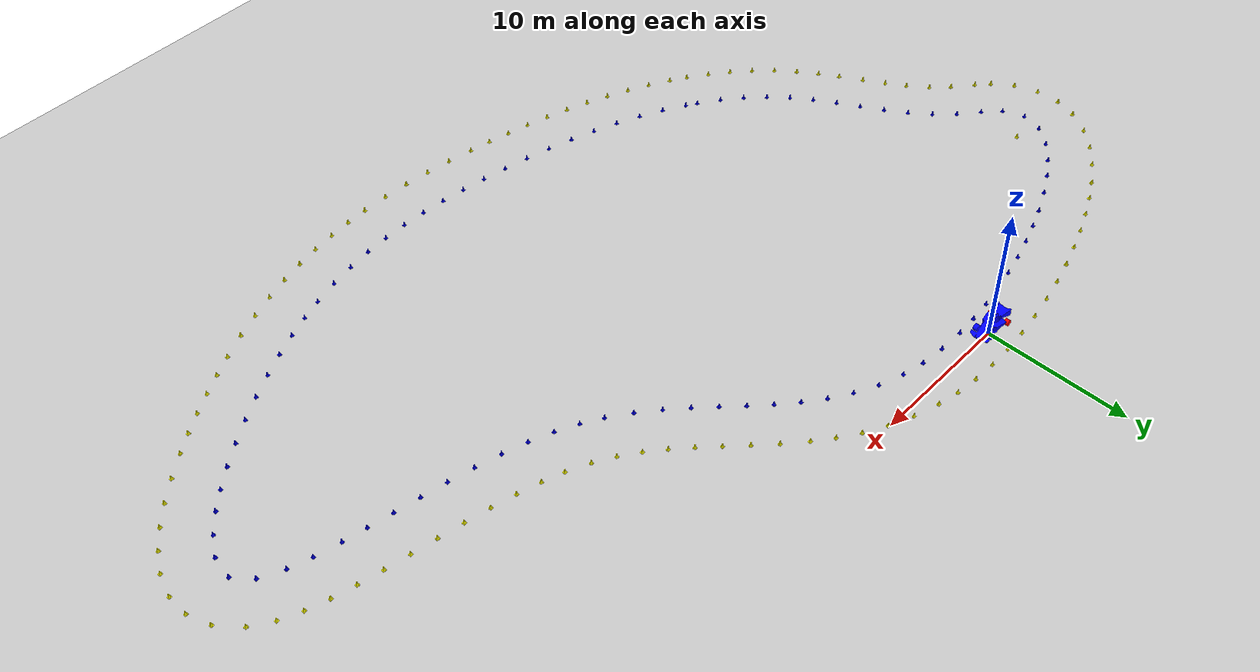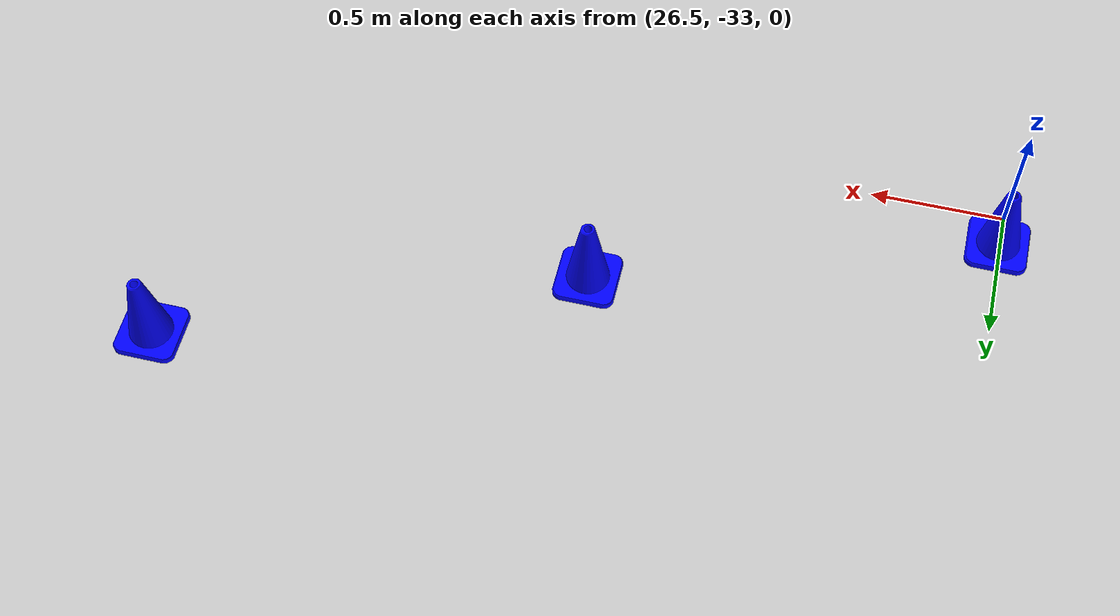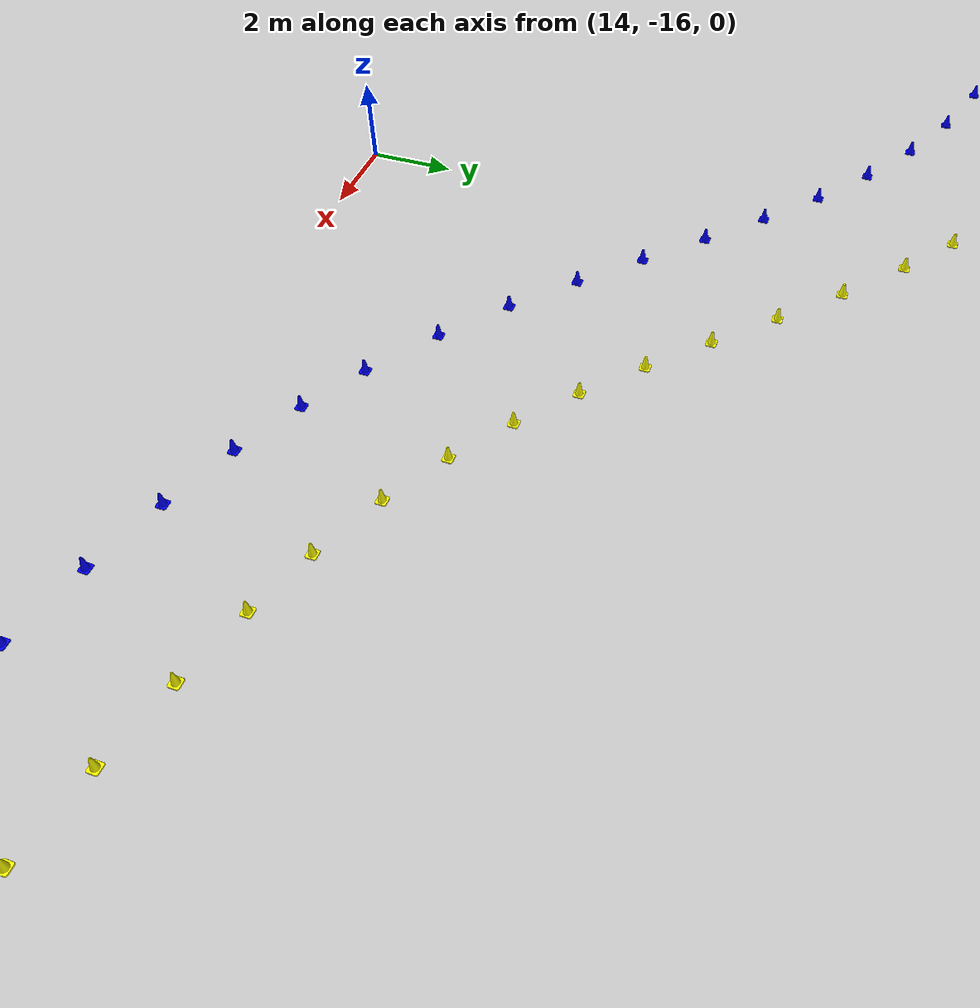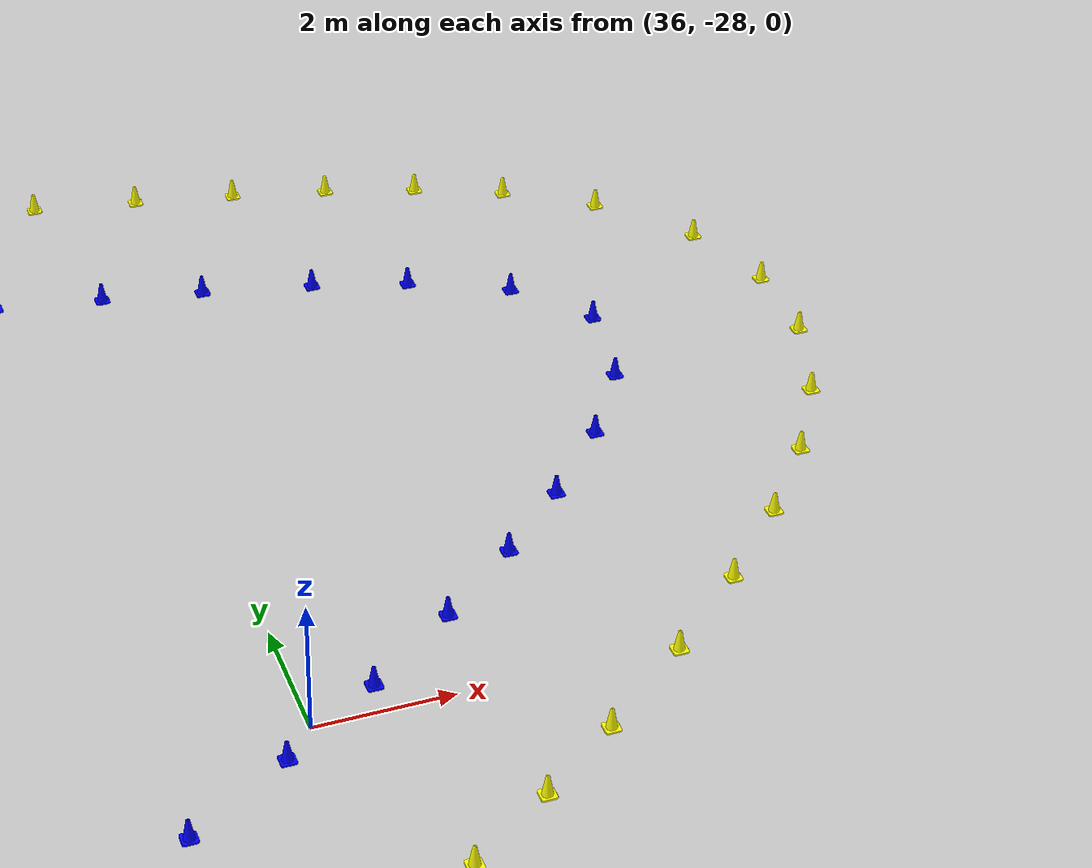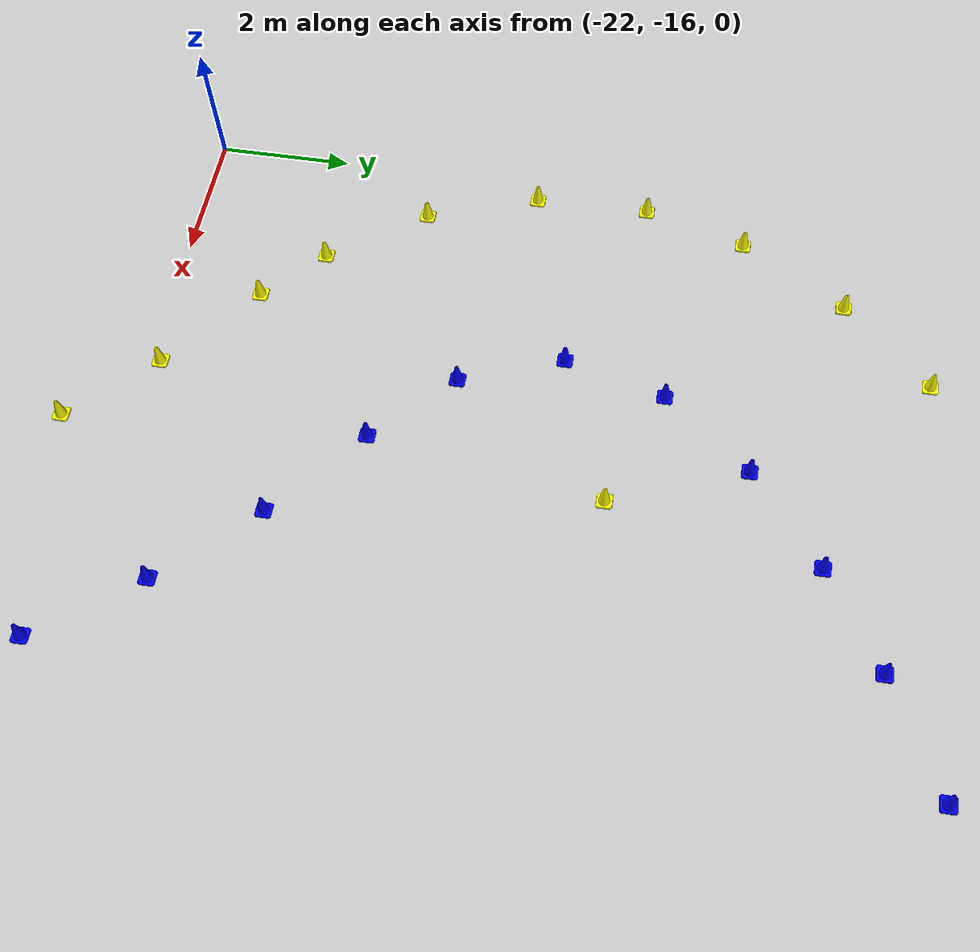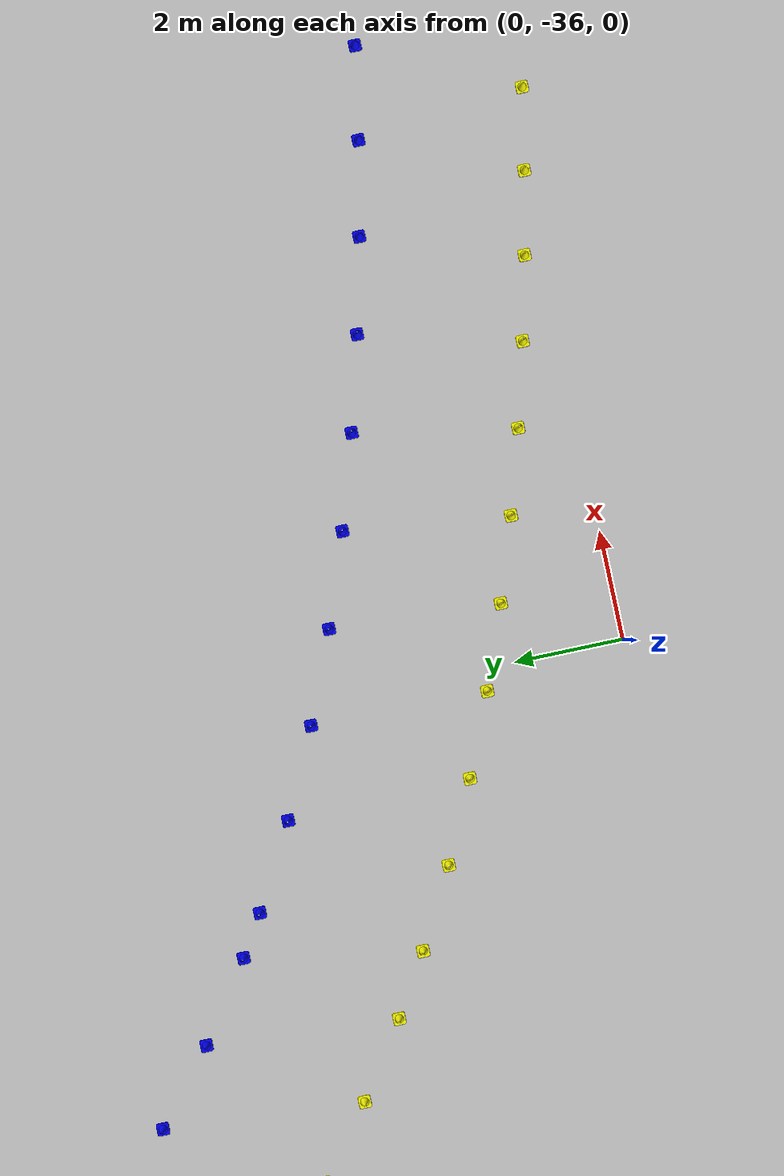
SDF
<?xml version="1.0" ?>
<sdf version="1.8">
    <world name="sim">
        <physics name="1ms" type="ignored">
            <max_step_size>0.001</max_step_size>
            <real_time_factor>1.0</real_time_factor>
        </physics>
        <plugin
            filename="libignition-gazebo-physics-system.so"
            name="ignition::gazebo::systems::Physics">
        </plugin>
        <plugin
            filename="libignition-gazebo-user-commands-system.so"
            name="ignition::gazebo::systems::UserCommands">
        </plugin>
        <plugin
            filename="libignition-gazebo-scene-broadcaster-system.so"
            name="ignition::gazebo::systems::SceneBroadcaster">
        </plugin>

        <light type="directional" name="sun">
            <cast_shadows>true</cast_shadows>
            <pose>0 0 10 0 0 0</pose>
            <diffuse>0.8 0.8 0.8 1</diffuse>
            <specular>0.2 0.2 0.2 1</specular>
            <attenuation>
                <range>1000</range>
                <constant>0.9</constant>
                <linear>0.01</linear>
                <quadratic>0.001</quadratic>
            </attenuation>
            <direction>-0.5 0.1 -0.9</direction>
        </light>

        <model name="ground_plane">
            <static>true</static>
            <link name="link">
                <collision name="collision">
                <geometry>
                    <plane>
                    <normal>0 0 0</normal>
                    </plane>
                </geometry>
                </collision>
                <visual name="visual">
                <geometry>
                    <plane>
                    <normal>0 0 1</normal>
                    <size>1000 1000</size>
                    </plane>
                </geometry>
                <material>
                    <ambient>0.8 0.8 0.8 1</ambient>
                    <diffuse>0.8 0.8 0.8 1</diffuse>
                    <specular>0.8 0.8 0.8 1</specular>
                </material>
                </visual>
            </link>
        </model>

        <!-- sensors plugin-->
        <plugin
            filename="libignition-gazebo-sensors-system.so"
            name="ignition::gazebo::systems::Sensors">
            <render_engine>ogre2</render_engine>
        </plugin>
        <plugin
            filename="gz-sim-imu-system"
            name="gz::sim::systems::Imu">
        </plugin>

        <model name="vehicle_blue">
            <pose>0 0 1.0 0.0 0.0 0.0</pose>

            <!--lidar frame-->
            <frame name="lidar_frame" attached_to='chassis'>
                <pose>-0.26 0 0.47 0 0.1570796 0.0</pose>
            </frame>

            <link name='chassis'>

                <!--lidar sensor-->
                <sensor name='lidar' type='gpu_lidar'>
                    <pose relative_to='lidar_frame'>0 0 0 0 0 0</pose>
                    <topic>model</topic>
                    <update_rate>20</update_rate>
                    <lidar>
                        <scan>
                            <horizontal>
                                <samples>500</samples>
                                <resolution>0.1</resolution>
                                <min_angle>-1.570796</min_angle>
                                <max_angle>1.570796</max_angle>
                            </horizontal>
                            <vertical>
                                <samples>320</samples>
                                <resolution>0.1</resolution>
                                <min_angle>-0.4363323</min_angle>
                                <max_angle>0.2617994</max_angle>
                            </vertical>
                        </scan>
                        <range>
                            <min>0.01</min>
                            <max>80.0</max>
                            <resolution>0.01</resolution>
                        </range>
                        <noise>
                            <type>gaussian</type>
                            <mean>0.0</mean>
                            <stddev>0.01</stddev>
                        </noise>
                    </lidar>

                    <always_on>1</always_on>
                    <visualize>true</visualize>
                </sensor>

                <!--imu sensor-->
                <sensor name="imu_sensor" type="imu">
                    <always_on>1</always_on>
                    <update_rate>100</update_rate>
                    <visualize>true</visualize>
                    <topic>imu</topic>
                </sensor>

                <inertial>
                    <mass>100.14395</mass>
                    <inertia>
                        <ixx>0.126164</ixx>
                        <ixy>0</ixy>
                        <ixz>0</ixz>
                        <iyy>0.416519</iyy>
                        <iyz>0</iyz>
                        <izz>0.481014</izz>
                    </inertia>
                </inertial>
                <visual name='visual'>
                    <geometry>
                        <mesh>
                            <scale>1 1 1</scale>
                            <uri>../models/formula_car_with_wheels.stl</uri>
                        </mesh>
                    </geometry>
                    <material>
                        <ambient>0.0 0.0 1.0 1</ambient>
                        <diffuse>0.0 0.0 1.0 1</diffuse>
                        <specular>0.0 0.0 1.0 1</specular>
                    </material>
                </visual>
                <collision name='collision'>
                    <geometry>
                        <mesh>
                            <scale>1 1 1</scale>
                            <uri>../models/formula_car_with_wheels.stl</uri>
                        </mesh>
                    <surface>
                        <friction>
                        <ode>
                            <mu>1.2</mu>
                            <mu2>1.2</mu2>
                        </ode>
                        </friction>
                    </surface>
                    </geometry>
                </collision>
            </link>

            <link name='left_wheel'>
                <pose relative_to="chassis">-1 0.6 -0.33 -1.5707 0 0</pose> <!--angles are in radian-->
                <inertial>
                    <mass>20</mass>
                    <inertia>
                        <ixx>0.145833</ixx>
                        <ixy>0</ixy>
                        <ixz>0</ixz>
                        <iyy>0.145833</iyy>
                        <iyz>0</iyz>
                        <izz>0.125</izz>
                    </inertia>
                </inertial>
                <visual name='visual'>
                    <geometry>
                        <cylinder>
                            <radius>0.2</radius>
                            <length>0.3</length>
                        </cylinder>
                    </geometry>
                    <material>
                        <ambient>1.0 0.0 0.0 1</ambient>
                        <diffuse>1.0 0.0 0.0 1</diffuse>
                        <specular>1.0 0.0 0.0 1</specular>
                    </material>
                </visual>
                <collision name='collision'>
                    <geometry>
                        <cylinder>
                            <radius>0.2</radius>
                            <length>0.3</length>
                        </cylinder>
                    </geometry>
                </collision>
            </link>

            <link name='right_wheel'>
                <pose relative_to="chassis">-1 -0.6 -0.33 -1.5707 0 0</pose> <!--angles are in radian-->
                <inertial>
                    <mass>20</mass>
                    <inertia>
                        <ixx>0.145833</ixx>
                        <ixy>0</ixy>
                        <ixz>0</ixz>
                        <iyy>0.145833</iyy>
                        <iyz>0</iyz>
                        <izz>0.125</izz>
                    </inertia>
                </inertial>
                <visual name='visual'>
                    <geometry>
                        <cylinder>
                            <radius>0.2</radius>
                            <length>0.3</length>
                        </cylinder>
                    </geometry>
                    <material>
                        <ambient>1.0 0.0 0.0 1</ambient>
                        <diffuse>1.0 0.0 0.0 1</diffuse>
                        <specular>1.0 0.0 0.0 1</specular>
                    </material>
                </visual>
                <collision name='collision'>
                    <geometry>
                        <cylinder>
                            <radius>0.2</radius>
                            <length>0.3</length>
                        </cylinder>
                    </geometry>
                </collision>
            </link>

            <link name='caster'>
                <pose relative_to="chassis"> 0.7 0 -0.43 0 0 0</pose> <!--angles are in radian-->
                <inertial>
                  <mass>1</mass>
                  <inertia>
                    <ixx>0.1</ixx>
                    <ixy>0</ixy>
                    <ixz>0</ixz>
                    <iyy>0.1</iyy>
                    <iyz>0</iyz>
                    <izz>0.1</izz>
                  </inertia>
                </inertial>
                <visual name='visual_caster'>
                  <geometry>
                    <sphere>
                      <radius>0.1</radius>
                    </sphere>
                  </geometry>
                  <material>
                    <ambient>0.2 0.2 0.2 1</ambient>
                    <diffuse>0.2 0.2 0.2 1</diffuse>
                    <specular>0.2 0.2 0.2 1</specular>
                  </material>
                </visual>
                <collision name='collision_caster'>
                  <geometry>
                    <sphere>
                      <radius>0.1</radius>
                    </sphere>
                  </geometry>
                </collision>
            </link>

            <joint name='left_wheel_joint' type='revolute'> <!--continous joint is not supported yet-->
                <pose relative_to='left_wheel'/>
                <parent>chassis</parent>
                <child>left_wheel</child>
                <axis>
                    <xyz expressed_in='__model__'>0 1 0</xyz> <!--can be defined as any frame or even arbitrary frames-->
                    <limit>
                        <lower>-1.79769e+308</lower>    <!--negative infinity-->
                        <upper>1.79769e+308</upper>     <!--positive infinity-->
                    </limit>
                </axis>
            </joint>

            <joint name='right_wheel_joint' type='revolute'> <!--continous joint is not supported yet-->
                <pose relative_to='right_wheel'/>
                <parent>chassis</parent>
                <child>right_wheel</child>
                <axis>
                    <xyz expressed_in='__model__'>0 1 0</xyz> <!--can be defined as any frame or even arbitrary frames-->
                    <limit>
                        <lower>-1.79769e+308</lower>    <!--negative infinity-->
                        <upper>1.79769e+308</upper>     <!--positive infinity-->
                    </limit>
                </axis>
            </joint>

            <joint name='caster_wheel' type='ball'>
                <parent>chassis</parent>
                <child>caster</child>
            </joint>

            <plugin
                filename="libignition-gazebo-diff-drive-system.so"
                name="ignition::gazebo::systems::DiffDrive">
                <left_joint>left_wheel_joint</left_joint>
                <right_joint>right_wheel_joint</right_joint>
                <wheel_separation>1.2</wheel_separation>
                <wheel_radius>0.2</wheel_radius>
                <topic>/model/cmd_vel</topic>
            </plugin>

            <plugin
                filename="libignition-gazebo-odometry-publisher-system"
                name="ignition::gazebo::systems::OdometryPublisher">
                <rpy_offset>0 0 0</rpy_offset>
                <dimensions>3</dimensions>
                <odom_publish_frequency>20</odom_publish_frequency>
            </plugin>

        </model>

        <model name='cone_0'>
            <static>true</static>
            <pose>-4.181472208659434 -28.115713603256516 0 0 0 0</pose>
            <link name='cone_link'>
                <inertial>
                    <mass>0.45</mass>
                    <inertia>
                        <ixx>0.5</ixx>
                        <ixy>0</ixy>
                        <ixz>0</ixz>
                        <iyy>0.5</iyy>
                        <iyz>0</iyz>
                        <izz>0.5</izz>
                    </inertia>
                </inertial>
                <visual name='visual'>
                    <geometry>
                        <mesh>
                            <scale>1 1 1</scale><!-- 1:1 = 228x228x325mm -->
                            <uri>../models/cone_325_no_color.stl</uri>
                        </mesh>
                    </geometry>
                    <material>
                        <ambient>0.0 0.0 1.0 1</ambient>
                        <diffuse>0.0 0.0 1.0 1</diffuse>
                        <specular>0.0 0.0 1.0 1</specular>
                    </material>
                </visual>
                <collision name='collision'>
                    <geometry>
                        <mesh>
                            <uri>../models/cone_325_no_color.stl</uri>
                        </mesh>
                    </geometry>
                </collision>
                <sensor name='sensor_contact' type='contact'>
                    <contact>
                        <collision>collision</collision>
                    </contact>
                </sensor>
            </link>
        </model>

        <model name='cone_1'>
            <static>true</static>
            <pose>-5.5763732713212955 -27.140231104301016 0 0 0 0</pose>
            <link name='cone_link'>
                <inertial>
                    <mass>0.45</mass>
                    <inertia>
                        <ixx>0.5</ixx>
                        <ixy>0</ixy>
                        <ixz>0</ixz>
                        <iyy>0.5</iyy>
                        <iyz>0</iyz>
                        <izz>0.5</izz>
                    </inertia>
                </inertial>
                <visual name='visual'>
                    <geometry>
                        <mesh>
                            <scale>1 1 1</scale><!-- 1:1 = 228x228x325mm -->
                            <uri>../models/cone_325_no_color.stl</uri>
                        </mesh>
                    </geometry>
                    <material>
                        <ambient>0.0 0.0 1.0 1</ambient>
                        <diffuse>0.0 0.0 1.0 1</diffuse>
                        <specular>0.0 0.0 1.0 1</specular>
                    </material>
                </visual>
                <collision name='collision'>
                    <geometry>
                        <mesh>
                            <uri>../models/cone_325_no_color.stl</uri>
                        </mesh>
                    </geometry>
                </collision>
                <sensor name='sensor_contact' type='contact'>
                    <contact>
                        <collision>collision</collision>
                    </contact>
                </sensor>
            </link>
        </model>

        <model name='cone_2'>
            <static>true</static>
            <pose>-6.87410039304628 -26.069543258558472 0 0 0 0</pose>
            <link name='cone_link'>
                <inertial>
                    <mass>0.45</mass>
                    <inertia>
                        <ixx>0.5</ixx>
                        <ixy>0</ixy>
                        <ixz>0</ixz>
                        <iyy>0.5</iyy>
                        <iyz>0</iyz>
                        <izz>0.5</izz>
                    </inertia>
                </inertial>
                <visual name='visual'>
                    <geometry>
                        <mesh>
                            <scale>1 1 1</scale><!-- 1:1 = 228x228x325mm -->
                            <uri>../models/cone_325_no_color.stl</uri>
                        </mesh>
                    </geometry>
                    <material>
                        <ambient>0.0 0.0 1.0 1</ambient>
                        <diffuse>0.0 0.0 1.0 1</diffuse>
                        <specular>0.0 0.0 1.0 1</specular>
                    </material>
                </visual>
                <collision name='collision'>
                    <geometry>
                        <mesh>
                            <uri>../models/cone_325_no_color.stl</uri>
                        </mesh>
                    </geometry>
                </collision>
                <sensor name='sensor_contact' type='contact'>
                    <contact>
                        <collision>collision</collision>
                    </contact>
                </sensor>
            </link>
        </model>

        <model name='cone_3'>
            <static>true</static>
            <pose>-8.062379995009014 -24.89908263605649 0 0 0 0</pose>
            <link name='cone_link'>
                <inertial>
                    <mass>0.45</mass>
                    <inertia>
                        <ixx>0.5</ixx>
                        <ixy>0</ixy>
                        <ixz>0</ixz>
                        <iyy>0.5</iyy>
                        <iyz>0</iyz>
                        <izz>0.5</izz>
                    </inertia>
                </inertial>
                <visual name='visual'>
                    <geometry>
                        <mesh>
                            <scale>1 1 1</scale><!-- 1:1 = 228x228x325mm -->
                            <uri>../models/cone_325_no_color.stl</uri>
                        </mesh>
                    </geometry>
                    <material>
                        <ambient>0.0 0.0 1.0 1</ambient>
                        <diffuse>0.0 0.0 1.0 1</diffuse>
                        <specular>0.0 0.0 1.0 1</specular>
                    </material>
                </visual>
                <collision name='collision'>
                    <geometry>
                        <mesh>
                            <uri>../models/cone_325_no_color.stl</uri>
                        </mesh>
                    </geometry>
                </collision>
                <sensor name='sensor_contact' type='contact'>
                    <contact>
                        <collision>collision</collision>
                    </contact>
                </sensor>
            </link>
        </model>

        <model name='cone_4'>
            <static>true</static>
            <pose>-9.128938498384155 -23.624281806822612 0 0 0 0</pose>
            <link name='cone_link'>
                <inertial>
                    <mass>0.45</mass>
                    <inertia>
                        <ixx>0.5</ixx>
                        <ixy>0</ixy>
                        <ixz>0</ixz>
                        <iyy>0.5</iyy>
                        <iyz>0</iyz>
                        <izz>0.5</izz>
                    </inertia>
                </inertial>
                <visual name='visual'>
                    <geometry>
                        <mesh>
                            <scale>1 1 1</scale><!-- 1:1 = 228x228x325mm -->
                            <uri>../models/cone_325_no_color.stl</uri>
                        </mesh>
                    </geometry>
                    <material>
                        <ambient>0.0 0.0 1.0 1</ambient>
                        <diffuse>0.0 0.0 1.0 1</diffuse>
                        <specular>0.0 0.0 1.0 1</specular>
                    </material>
                </visual>
                <collision name='collision'>
                    <geometry>
                        <mesh>
                            <uri>../models/cone_325_no_color.stl</uri>
                        </mesh>
                    </geometry>
                </collision>
                <sensor name='sensor_contact' type='contact'>
                    <contact>
                        <collision>collision</collision>
                    </contact>
                </sensor>
            </link>
        </model>

        <model name='cone_5'>
            <static>true</static>
            <pose>-10.070937582515045 -22.246749116785608 0 0 0 0</pose>
            <link name='cone_link'>
                <inertial>
                    <mass>0.45</mass>
                    <inertia>
                        <ixx>0.5</ixx>
                        <ixy>0</ixy>
                        <ixz>0</ixz>
                        <iyy>0.5</iyy>
                        <iyz>0</iyz>
                        <izz>0.5</izz>
                    </inertia>
                </inertial>
                <visual name='visual'>
                    <geometry>
                        <mesh>
                            <scale>1 1 1</scale><!-- 1:1 = 228x228x325mm -->
                            <uri>../models/cone_325_no_color.stl</uri>
                        </mesh>
                    </geometry>
                    <material>
                        <ambient>0.0 0.0 1.0 1</ambient>
                        <diffuse>0.0 0.0 1.0 1</diffuse>
                        <specular>0.0 0.0 1.0 1</specular>
                    </material>
                </visual>
                <collision name='collision'>
                    <geometry>
                        <mesh>
                            <uri>../models/cone_325_no_color.stl</uri>
                        </mesh>
                    </geometry>
                </collision>
                <sensor name='sensor_contact' type='contact'>
                    <contact>
                        <collision>collision</collision>
                    </contact>
                </sensor>
            </link>
        </model>

        <model name='cone_6'>
            <static>true</static>
            <pose>-10.927938820275859 -20.795845437136084 0 0 0 0</pose>
            <link name='cone_link'>
                <inertial>
                    <mass>0.45</mass>
                    <inertia>
                        <ixx>0.5</ixx>
                        <ixy>0</ixy>
                        <ixz>0</ixz>
                        <iyy>0.5</iyy>
                        <iyz>0</iyz>
                        <izz>0.5</izz>
                    </inertia>
                </inertial>
                <visual name='visual'>
                    <geometry>
                        <mesh>
                            <scale>1 1 1</scale><!-- 1:1 = 228x228x325mm -->
                            <uri>../models/cone_325_no_color.stl</uri>
                        </mesh>
                    </geometry>
                    <material>
                        <ambient>0.0 0.0 1.0 1</ambient>
                        <diffuse>0.0 0.0 1.0 1</diffuse>
                        <specular>0.0 0.0 1.0 1</specular>
                    </material>
                </visual>
                <collision name='collision'>
                    <geometry>
                        <mesh>
                            <uri>../models/cone_325_no_color.stl</uri>
                        </mesh>
                    </geometry>
                </collision>
                <sensor name='sensor_contact' type='contact'>
                    <contact>
                        <collision>collision</collision>
                    </contact>
                </sensor>
            </link>
        </model>

        <model name='cone_7'>
            <static>true</static>
            <pose>-11.751408750734665 -19.308723943420272 0 0 0 0</pose>
            <link name='cone_link'>
                <inertial>
                    <mass>0.45</mass>
                    <inertia>
                        <ixx>0.5</ixx>
                        <ixy>0</ixy>
                        <ixz>0</ixz>
                        <iyy>0.5</iyy>
                        <iyz>0</iyz>
                        <izz>0.5</izz>
                    </inertia>
                </inertial>
                <visual name='visual'>
                    <geometry>
                        <mesh>
                            <scale>1 1 1</scale><!-- 1:1 = 228x228x325mm -->
                            <uri>../models/cone_325_no_color.stl</uri>
                        </mesh>
                    </geometry>
                    <material>
                        <ambient>0.0 0.0 1.0 1</ambient>
                        <diffuse>0.0 0.0 1.0 1</diffuse>
                        <specular>0.0 0.0 1.0 1</specular>
                    </material>
                </visual>
                <collision name='collision'>
                    <geometry>
                        <mesh>
                            <uri>../models/cone_325_no_color.stl</uri>
                        </mesh>
                    </geometry>
                </collision>
                <sensor name='sensor_contact' type='contact'>
                    <contact>
                        <collision>collision</collision>
                    </contact>
                </sensor>
            </link>
        </model>

        <model name='cone_8'>
            <static>true</static>
            <pose>-12.592814531836376 -17.822538216265496 0 0 0 0</pose>
            <link name='cone_link'>
                <inertial>
                    <mass>0.45</mass>
                    <inertia>
                        <ixx>0.5</ixx>
                        <ixy>0</ixy>
                        <ixz>0</ixz>
                        <iyy>0.5</iyy>
                        <iyz>0</iyz>
                        <izz>0.5</izz>
                    </inertia>
                </inertial>
                <visual name='visual'>
                    <geometry>
                        <mesh>
                            <scale>1 1 1</scale><!-- 1:1 = 228x228x325mm -->
                            <uri>../models/cone_325_no_color.stl</uri>
                        </mesh>
                    </geometry>
                    <material>
                        <ambient>0.0 0.0 1.0 1</ambient>
                        <diffuse>0.0 0.0 1.0 1</diffuse>
                        <specular>0.0 0.0 1.0 1</specular>
                    </material>
                </visual>
                <collision name='collision'>
                    <geometry>
                        <mesh>
                            <uri>../models/cone_325_no_color.stl</uri>
                        </mesh>
                    </geometry>
                </collision>
                <sensor name='sensor_contact' type='contact'>
                    <contact>
                        <collision>collision</collision>
                    </contact>
                </sensor>
            </link>
        </model>

        <model name='cone_9'>
            <static>true</static>
            <pose>-13.503623321525907 -16.374441836299084 0 0 0 0</pose>
            <link name='cone_link'>
                <inertial>
                    <mass>0.45</mass>
                    <inertia>
                        <ixx>0.5</ixx>
                        <ixy>0</ixy>
                        <ixz>0</ixz>
                        <iyy>0.5</iyy>
                        <iyz>0</iyz>
                        <izz>0.5</izz>
                    </inertia>
                </inertial>
                <visual name='visual'>
                    <geometry>
                        <mesh>
                            <scale>1 1 1</scale><!-- 1:1 = 228x228x325mm -->
                            <uri>../models/cone_325_no_color.stl</uri>
                        </mesh>
                    </geometry>
                    <material>
                        <ambient>0.0 0.0 1.0 1</ambient>
                        <diffuse>0.0 0.0 1.0 1</diffuse>
                        <specular>0.0 0.0 1.0 1</specular>
                    </material>
                </visual>
                <collision name='collision'>
                    <geometry>
                        <mesh>
                            <uri>../models/cone_325_no_color.stl</uri>
                        </mesh>
                    </geometry>
                </collision>
                <sensor name='sensor_contact' type='contact'>
                    <contact>
                        <collision>collision</collision>
                    </contact>
                </sensor>
            </link>
        </model>

        <model name='cone_10'>
            <static>true</static>
            <pose>-14.535302277748182 -15.001588384148361 0 0 0 0</pose>
            <link name='cone_link'>
                <inertial>
                    <mass>0.45</mass>
                    <inertia>
                        <ixx>0.5</ixx>
                        <ixy>0</ixy>
                        <ixz>0</ixz>
                        <iyy>0.5</iyy>
                        <iyz>0</iyz>
                        <izz>0.5</izz>
                    </inertia>
                </inertial>
                <visual name='visual'>
                    <geometry>
                        <mesh>
                            <scale>1 1 1</scale><!-- 1:1 = 228x228x325mm -->
                            <uri>../models/cone_325_no_color.stl</uri>
                        </mesh>
                    </geometry>
                    <material>
                        <ambient>0.0 0.0 1.0 1</ambient>
                        <diffuse>0.0 0.0 1.0 1</diffuse>
                        <specular>0.0 0.0 1.0 1</specular>
                    </material>
                </visual>
                <collision name='collision'>
                    <geometry>
                        <mesh>
                            <uri>../models/cone_325_no_color.stl</uri>
                        </mesh>
                    </geometry>
                </collision>
                <sensor name='sensor_contact' type='contact'>
                    <contact>
                        <collision>collision</collision>
                    </contact>
                </sensor>
            </link>
        </model>

        <model name='cone_11'>
            <static>true</static>
            <pose>-15.7393185584481 -13.741131440440666 0 0 0 0</pose>
            <link name='cone_link'>
                <inertial>
                    <mass>0.45</mass>
                    <inertia>
                        <ixx>0.5</ixx>
                        <ixy>0</ixy>
                        <ixz>0</ixz>
                        <iyy>0.5</iyy>
                        <iyz>0</iyz>
                        <izz>0.5</izz>
                    </inertia>
                </inertial>
                <visual name='visual'>
                    <geometry>
                        <mesh>
                            <scale>1 1 1</scale><!-- 1:1 = 228x228x325mm -->
                            <uri>../models/cone_325_no_color.stl</uri>
                        </mesh>
                    </geometry>
                    <material>
                        <ambient>0.0 0.0 1.0 1</ambient>
                        <diffuse>0.0 0.0 1.0 1</diffuse>
                        <specular>0.0 0.0 1.0 1</specular>
                    </material>
                </visual>
                <collision name='collision'>
                    <geometry>
                        <mesh>
                            <uri>../models/cone_325_no_color.stl</uri>
                        </mesh>
                    </geometry>
                </collision>
                <sensor name='sensor_contact' type='contact'>
                    <contact>
                        <collision>collision</collision>
                    </contact>
                </sensor>
            </link>
        </model>

        <model name='cone_12'>
            <static>true</static>
            <pose>-17.10234883640708 -12.61335988897849 0 0 0 0</pose>
            <link name='cone_link'>
                <inertial>
                    <mass>0.45</mass>
                    <inertia>
                        <ixx>0.5</ixx>
                        <ixy>0</ixy>
                        <ixz>0</ixz>
                        <iyy>0.5</iyy>
                        <iyz>0</iyz>
                        <izz>0.5</izz>
                    </inertia>
                </inertial>
                <visual name='visual'>
                    <geometry>
                        <mesh>
                            <scale>1 1 1</scale><!-- 1:1 = 228x228x325mm -->
                            <uri>../models/cone_325_no_color.stl</uri>
                        </mesh>
                    </geometry>
                    <material>
                        <ambient>0.0 0.0 1.0 1</ambient>
                        <diffuse>0.0 0.0 1.0 1</diffuse>
                        <specular>0.0 0.0 1.0 1</specular>
                    </material>
                </visual>
                <collision name='collision'>
                    <geometry>
                        <mesh>
                            <uri>../models/cone_325_no_color.stl</uri>
                        </mesh>
                    </geometry>
                </collision>
                <sensor name='sensor_contact' type='contact'>
                    <contact>
                        <collision>collision</collision>
                    </contact>
                </sensor>
            </link>
        </model>

        <model name='cone_13'>
            <static>true</static>
            <pose>-18.208704938516075 -11.533696115235749 0 0 0 0</pose>
            <link name='cone_link'>
                <inertial>
                    <mass>0.45</mass>
                    <inertia>
                        <ixx>0.5</ixx>
                        <ixy>0</ixy>
                        <ixz>0</ixz>
                        <iyy>0.5</iyy>
                        <iyz>0</iyz>
                        <izz>0.5</izz>
                    </inertia>
                </inertial>
                <visual name='visual'>
                    <geometry>
                        <mesh>
                            <scale>1 1 1</scale><!-- 1:1 = 228x228x325mm -->
                            <uri>../models/cone_325_no_color.stl</uri>
                        </mesh>
                    </geometry>
                    <material>
                        <ambient>0.0 0.0 1.0 1</ambient>
                        <diffuse>0.0 0.0 1.0 1</diffuse>
                        <specular>0.0 0.0 1.0 1</specular>
                    </material>
                </visual>
                <collision name='collision'>
                    <geometry>
                        <mesh>
                            <uri>../models/cone_325_no_color.stl</uri>
                        </mesh>
                    </geometry>
                </collision>
                <sensor name='sensor_contact' type='contact'>
                    <contact>
                        <collision>collision</collision>
                    </contact>
                </sensor>
            </link>
        </model>

        <model name='cone_14'>
            <static>true</static>
            <pose>-18.764089499975643 -10.058502309465192 0 0 0 0</pose>
            <link name='cone_link'>
                <inertial>
                    <mass>0.45</mass>
                    <inertia>
                        <ixx>0.5</ixx>
                        <ixy>0</ixy>
                        <ixz>0</ixz>
                        <iyy>0.5</iyy>
                        <iyz>0</iyz>
                        <izz>0.5</izz>
                    </inertia>
                </inertial>
                <visual name='visual'>
                    <geometry>
                        <mesh>
                            <scale>1 1 1</scale><!-- 1:1 = 228x228x325mm -->
                            <uri>../models/cone_325_no_color.stl</uri>
                        </mesh>
                    </geometry>
                    <material>
                        <ambient>0.0 0.0 1.0 1</ambient>
                        <diffuse>0.0 0.0 1.0 1</diffuse>
                        <specular>0.0 0.0 1.0 1</specular>
                    </material>
                </visual>
                <collision name='collision'>
                    <geometry>
                        <mesh>
                            <uri>../models/cone_325_no_color.stl</uri>
                        </mesh>
                    </geometry>
                </collision>
                <sensor name='sensor_contact' type='contact'>
                    <contact>
                        <collision>collision</collision>
                    </contact>
                </sensor>
            </link>
        </model>

        <model name='cone_15'>
            <static>true</static>
            <pose>-18.351183929379907 -8.570709637223901 0 0 0 0</pose>
            <link name='cone_link'>
                <inertial>
                    <mass>0.45</mass>
                    <inertia>
                        <ixx>0.5</ixx>
                        <ixy>0</ixy>
                        <ixz>0</ixz>
                        <iyy>0.5</iyy>
                        <iyz>0</iyz>
                        <izz>0.5</izz>
                    </inertia>
                </inertial>
                <visual name='visual'>
                    <geometry>
                        <mesh>
                            <scale>1 1 1</scale><!-- 1:1 = 228x228x325mm -->
                            <uri>../models/cone_325_no_color.stl</uri>
                        </mesh>
                    </geometry>
                    <material>
                        <ambient>0.0 0.0 1.0 1</ambient>
                        <diffuse>0.0 0.0 1.0 1</diffuse>
                        <specular>0.0 0.0 1.0 1</specular>
                    </material>
                </visual>
                <collision name='collision'>
                    <geometry>
                        <mesh>
                            <uri>../models/cone_325_no_color.stl</uri>
                        </mesh>
                    </geometry>
                </collision>
                <sensor name='sensor_contact' type='contact'>
                    <contact>
                        <collision>collision</collision>
                    </contact>
                </sensor>
            </link>
        </model>

        <model name='cone_16'>
            <static>true</static>
            <pose>-17.3077808230539 -7.292004064827377 0 0 0 0</pose>
            <link name='cone_link'>
                <inertial>
                    <mass>0.45</mass>
                    <inertia>
                        <ixx>0.5</ixx>
                        <ixy>0</ixy>
                        <ixz>0</ixz>
                        <iyy>0.5</iyy>
                        <iyz>0</iyz>
                        <izz>0.5</izz>
                    </inertia>
                </inertial>
                <visual name='visual'>
                    <geometry>
                        <mesh>
                            <scale>1 1 1</scale><!-- 1:1 = 228x228x325mm -->
                            <uri>../models/cone_325_no_color.stl</uri>
                        </mesh>
                    </geometry>
                    <material>
                        <ambient>0.0 0.0 1.0 1</ambient>
                        <diffuse>0.0 0.0 1.0 1</diffuse>
                        <specular>0.0 0.0 1.0 1</specular>
                    </material>
                </visual>
                <collision name='collision'>
                    <geometry>
                        <mesh>
                            <uri>../models/cone_325_no_color.stl</uri>
                        </mesh>
                    </geometry>
                </collision>
                <sensor name='sensor_contact' type='contact'>
                    <contact>
                        <collision>collision</collision>
                    </contact>
                </sensor>
            </link>
        </model>

        <model name='cone_17'>
            <static>true</static>
            <pose>-15.982818402671322 -6.235826871431316 0 0 0 0</pose>
            <link name='cone_link'>
                <inertial>
                    <mass>0.45</mass>
                    <inertia>
                        <ixx>0.5</ixx>
                        <ixy>0</ixy>
                        <ixz>0</ixz>
                        <iyy>0.5</iyy>
                        <iyz>0</iyz>
                        <izz>0.5</izz>
                    </inertia>
                </inertial>
                <visual name='visual'>
                    <geometry>
                        <mesh>
                            <scale>1 1 1</scale><!-- 1:1 = 228x228x325mm -->
                            <uri>../models/cone_325_no_color.stl</uri>
                        </mesh>
                    </geometry>
                    <material>
                        <ambient>0.0 0.0 1.0 1</ambient>
                        <diffuse>0.0 0.0 1.0 1</diffuse>
                        <specular>0.0 0.0 1.0 1</specular>
                    </material>
                </visual>
                <collision name='collision'>
                    <geometry>
                        <mesh>
                            <uri>../models/cone_325_no_color.stl</uri>
                        </mesh>
                    </geometry>
                </collision>
                <sensor name='sensor_contact' type='contact'>
                    <contact>
                        <collision>collision</collision>
                    </contact>
                </sensor>
            </link>
        </model>

        <model name='cone_18'>
            <static>true</static>
            <pose>-14.621033766201187 -5.397494520968078 0 0 0 0</pose>
            <link name='cone_link'>
                <inertial>
                    <mass>0.45</mass>
                    <inertia>
                        <ixx>0.5</ixx>
                        <ixy>0</ixy>
                        <ixz>0</ixz>
                        <iyy>0.5</iyy>
                        <iyz>0</iyz>
                        <izz>0.5</izz>
                    </inertia>
                </inertial>
                <visual name='visual'>
                    <geometry>
                        <mesh>
                            <scale>1 1 1</scale><!-- 1:1 = 228x228x325mm -->
                            <uri>../models/cone_325_no_color.stl</uri>
                        </mesh>
                    </geometry>
                    <material>
                        <ambient>0.0 0.0 1.0 1</ambient>
                        <diffuse>0.0 0.0 1.0 1</diffuse>
                        <specular>0.0 0.0 1.0 1</specular>
                    </material>
                </visual>
                <collision name='collision'>
                    <geometry>
                        <mesh>
                            <uri>../models/cone_325_no_color.stl</uri>
                        </mesh>
                    </geometry>
                </collision>
                <sensor name='sensor_contact' type='contact'>
                    <contact>
                        <collision>collision</collision>
                    </contact>
                </sensor>
            </link>
        </model>

        <model name='cone_19'>
            <static>true</static>
            <pose>-13.06218681797266 -4.608256179912427 0 0 0 0</pose>
            <link name='cone_link'>
                <inertial>
                    <mass>0.45</mass>
                    <inertia>
                        <ixx>0.5</ixx>
                        <ixy>0</ixy>
                        <ixz>0</ixz>
                        <iyy>0.5</iyy>
                        <iyz>0</iyz>
                        <izz>0.5</izz>
                    </inertia>
                </inertial>
                <visual name='visual'>
                    <geometry>
                        <mesh>
                            <scale>1 1 1</scale><!-- 1:1 = 228x228x325mm -->
                            <uri>../models/cone_325_no_color.stl</uri>
                        </mesh>
                    </geometry>
                    <material>
                        <ambient>0.0 0.0 1.0 1</ambient>
                        <diffuse>0.0 0.0 1.0 1</diffuse>
                        <specular>0.0 0.0 1.0 1</specular>
                    </material>
                </visual>
                <collision name='collision'>
                    <geometry>
                        <mesh>
                            <uri>../models/cone_325_no_color.stl</uri>
                        </mesh>
                    </geometry>
                </collision>
                <sensor name='sensor_contact' type='contact'>
                    <contact>
                        <collision>collision</collision>
                    </contact>
                </sensor>
            </link>
        </model>

        <model name='cone_20'>
            <static>true</static>
            <pose>-11.341119100500306 -3.87849943319181 0 0 0 0</pose>
            <link name='cone_link'>
                <inertial>
                    <mass>0.45</mass>
                    <inertia>
                        <ixx>0.5</ixx>
                        <ixy>0</ixy>
                        <ixz>0</ixz>
                        <iyy>0.5</iyy>
                        <iyz>0</iyz>
                        <izz>0.5</izz>
                    </inertia>
                </inertial>
                <visual name='visual'>
                    <geometry>
                        <mesh>
                            <scale>1 1 1</scale><!-- 1:1 = 228x228x325mm -->
                            <uri>../models/cone_325_no_color.stl</uri>
                        </mesh>
                    </geometry>
                    <material>
                        <ambient>0.0 0.0 1.0 1</ambient>
                        <diffuse>0.0 0.0 1.0 1</diffuse>
                        <specular>0.0 0.0 1.0 1</specular>
                    </material>
                </visual>
                <collision name='collision'>
                    <geometry>
                        <mesh>
                            <uri>../models/cone_325_no_color.stl</uri>
                        </mesh>
                    </geometry>
                </collision>
                <sensor name='sensor_contact' type='contact'>
                    <contact>
                        <collision>collision</collision>
                    </contact>
                </sensor>
            </link>
        </model>

        <model name='cone_21'>
            <static>true</static>
            <pose>-9.870879489236653 -3.344501240807788 0 0 0 0</pose>
            <link name='cone_link'>
                <inertial>
                    <mass>0.45</mass>
                    <inertia>
                        <ixx>0.5</ixx>
                        <ixy>0</ixy>
                        <ixz>0</ixz>
                        <iyy>0.5</iyy>
                        <iyz>0</iyz>
                        <izz>0.5</izz>
                    </inertia>
                </inertial>
                <visual name='visual'>
                    <geometry>
                        <mesh>
                            <scale>1 1 1</scale><!-- 1:1 = 228x228x325mm -->
                            <uri>../models/cone_325_no_color.stl</uri>
                        </mesh>
                    </geometry>
                    <material>
                        <ambient>0.0 0.0 1.0 1</ambient>
                        <diffuse>0.0 0.0 1.0 1</diffuse>
                        <specular>0.0 0.0 1.0 1</specular>
                    </material>
                </visual>
                <collision name='collision'>
                    <geometry>
                        <mesh>
                            <uri>../models/cone_325_no_color.stl</uri>
                        </mesh>
                    </geometry>
                </collision>
                <sensor name='sensor_contact' type='contact'>
                    <contact>
                        <collision>collision</collision>
                    </contact>
                </sensor>
            </link>
        </model>

        <model name='cone_22'>
            <static>true</static>
            <pose>-8.336956042633714 -2.8605377666346 0 0 0 0</pose>
            <link name='cone_link'>
                <inertial>
                    <mass>0.45</mass>
                    <inertia>
                        <ixx>0.5</ixx>
                        <ixy>0</ixy>
                        <ixz>0</ixz>
                        <iyy>0.5</iyy>
                        <iyz>0</iyz>
                        <izz>0.5</izz>
                    </inertia>
                </inertial>
                <visual name='visual'>
                    <geometry>
                        <mesh>
                            <scale>1 1 1</scale><!-- 1:1 = 228x228x325mm -->
                            <uri>../models/cone_325_no_color.stl</uri>
                        </mesh>
                    </geometry>
                    <material>
                        <ambient>0.0 0.0 1.0 1</ambient>
                        <diffuse>0.0 0.0 1.0 1</diffuse>
                        <specular>0.0 0.0 1.0 1</specular>
                    </material>
                </visual>
                <collision name='collision'>
                    <geometry>
                        <mesh>
                            <uri>../models/cone_325_no_color.stl</uri>
                        </mesh>
                    </geometry>
                </collision>
                <sensor name='sensor_contact' type='contact'>
                    <contact>
                        <collision>collision</collision>
                    </contact>
                </sensor>
            </link>
        </model>

        <model name='cone_23'>
            <static>true</static>
            <pose>-6.757187630458958 -2.4319274541551095 0 0 0 0</pose>
            <link name='cone_link'>
                <inertial>
                    <mass>0.45</mass>
                    <inertia>
                        <ixx>0.5</ixx>
                        <ixy>0</ixy>
                        <ixz>0</ixz>
                        <iyy>0.5</iyy>
                        <iyz>0</iyz>
                        <izz>0.5</izz>
                    </inertia>
                </inertial>
                <visual name='visual'>
                    <geometry>
                        <mesh>
                            <scale>1 1 1</scale><!-- 1:1 = 228x228x325mm -->
                            <uri>../models/cone_325_no_color.stl</uri>
                        </mesh>
                    </geometry>
                    <material>
                        <ambient>0.0 0.0 1.0 1</ambient>
                        <diffuse>0.0 0.0 1.0 1</diffuse>
                        <specular>0.0 0.0 1.0 1</specular>
                    </material>
                </visual>
                <collision name='collision'>
                    <geometry>
                        <mesh>
                            <uri>../models/cone_325_no_color.stl</uri>
                        </mesh>
                    </geometry>
                </collision>
                <sensor name='sensor_contact' type='contact'>
                    <contact>
                        <collision>collision</collision>
                    </contact>
                </sensor>
            </link>
        </model>

        <model name='cone_24'>
            <static>true</static>
            <pose>-5.149413122479829 -2.0639887468521567 0 0 0 0</pose>
            <link name='cone_link'>
                <inertial>
                    <mass>0.45</mass>
                    <inertia>
                        <ixx>0.5</ixx>
                        <ixy>0</ixy>
                        <ixz>0</ixz>
                        <iyy>0.5</iyy>
                        <iyz>0</iyz>
                        <izz>0.5</izz>
                    </inertia>
                </inertial>
                <visual name='visual'>
                    <geometry>
                        <mesh>
                            <scale>1 1 1</scale><!-- 1:1 = 228x228x325mm -->
                            <uri>../models/cone_325_no_color.stl</uri>
                        </mesh>
                    </geometry>
                    <material>
                        <ambient>0.0 0.0 1.0 1</ambient>
                        <diffuse>0.0 0.0 1.0 1</diffuse>
                        <specular>0.0 0.0 1.0 1</specular>
                    </material>
                </visual>
                <collision name='collision'>
                    <geometry>
                        <mesh>
                            <uri>../models/cone_325_no_color.stl</uri>
                        </mesh>
                    </geometry>
                </collision>
                <sensor name='sensor_contact' type='contact'>
                    <contact>
                        <collision>collision</collision>
                    </contact>
                </sensor>
            </link>
        </model>

        <model name='cone_25'>
            <static>true</static>
            <pose>-3.531471388463787 -1.762040088208603 0 0 0 0</pose>
            <link name='cone_link'>
                <inertial>
                    <mass>0.45</mass>
                    <inertia>
                        <ixx>0.5</ixx>
                        <ixy>0</ixy>
                        <ixz>0</ixz>
                        <iyy>0.5</iyy>
                        <iyz>0</iyz>
                        <izz>0.5</izz>
                    </inertia>
                </inertial>
                <visual name='visual'>
                    <geometry>
                        <mesh>
                            <scale>1 1 1</scale><!-- 1:1 = 228x228x325mm -->
                            <uri>../models/cone_325_no_color.stl</uri>
                        </mesh>
                    </geometry>
                    <material>
                        <ambient>0.0 0.0 1.0 1</ambient>
                        <diffuse>0.0 0.0 1.0 1</diffuse>
                        <specular>0.0 0.0 1.0 1</specular>
                    </material>
                </visual>
                <collision name='collision'>
                    <geometry>
                        <mesh>
                            <uri>../models/cone_325_no_color.stl</uri>
                        </mesh>
                    </geometry>
                </collision>
                <sensor name='sensor_contact' type='contact'>
                    <contact>
                        <collision>collision</collision>
                    </contact>
                </sensor>
            </link>
        </model>

        <model name='cone_26'>
            <static>true</static>
            <pose>-1.9212012981782856 -1.5313999217072949 0 0 0 0</pose>
            <link name='cone_link'>
                <inertial>
                    <mass>0.45</mass>
                    <inertia>
                        <ixx>0.5</ixx>
                        <ixy>0</ixy>
                        <ixz>0</ixz>
                        <iyy>0.5</iyy>
                        <iyz>0</iyz>
                        <izz>0.5</izz>
                    </inertia>
                </inertial>
                <visual name='visual'>
                    <geometry>
                        <mesh>
                            <scale>1 1 1</scale><!-- 1:1 = 228x228x325mm -->
                            <uri>../models/cone_325_no_color.stl</uri>
                        </mesh>
                    </geometry>
                    <material>
                        <ambient>0.0 0.0 1.0 1</ambient>
                        <diffuse>0.0 0.0 1.0 1</diffuse>
                        <specular>0.0 0.0 1.0 1</specular>
                    </material>
                </visual>
                <collision name='collision'>
                    <geometry>
                        <mesh>
                            <uri>../models/cone_325_no_color.stl</uri>
                        </mesh>
                    </geometry>
                </collision>
                <sensor name='sensor_contact' type='contact'>
                    <contact>
                        <collision>collision</collision>
                    </contact>
                </sensor>
            </link>
        </model>

        <model name='cone_27'>
            <static>true</static>
            <pose>-0.33644172139079 -1.377386690831095 0 0 0 0</pose>
            <link name='cone_link'>
                <inertial>
                    <mass>0.45</mass>
                    <inertia>
                        <ixx>0.5</ixx>
                        <ixy>0</ixy>
                        <ixz>0</ixz>
                        <iyy>0.5</iyy>
                        <iyz>0</iyz>
                        <izz>0.5</izz>
                    </inertia>
                </inertial>
                <visual name='visual'>
                    <geometry>
                        <mesh>
                            <scale>1 1 1</scale><!-- 1:1 = 228x228x325mm -->
                            <uri>../models/cone_325_no_color.stl</uri>
                        </mesh>
                    </geometry>
                    <material>
                        <ambient>0.0 0.0 1.0 1</ambient>
                        <diffuse>0.0 0.0 1.0 1</diffuse>
                        <specular>0.0 0.0 1.0 1</specular>
                    </material>
                </visual>
                <collision name='collision'>
                    <geometry>
                        <mesh>
                            <uri>../models/cone_325_no_color.stl</uri>
                        </mesh>
                    </geometry>
                </collision>
                <sensor name='sensor_contact' type='contact'>
                    <contact>
                        <collision>collision</collision>
                    </contact>
                </sensor>
            </link>
        </model>

        <model name='cone_28'>
            <static>true</static>
            <pose>1.2049684721312581 -1.3053188390628434 0 0 0 0</pose>
            <link name='cone_link'>
                <inertial>
                    <mass>0.45</mass>
                    <inertia>
                        <ixx>0.5</ixx>
                        <ixy>0</ixy>
                        <ixz>0</ixz>
                        <iyy>0.5</iyy>
                        <iyz>0</iyz>
                        <izz>0.5</izz>
                    </inertia>
                </inertial>
                <visual name='visual'>
                    <geometry>
                        <mesh>
                            <scale>1 1 1</scale><!-- 1:1 = 228x228x325mm -->
                            <uri>../models/cone_325_no_color.stl</uri>
                        </mesh>
                    </geometry>
                    <material>
                        <ambient>0.0 0.0 1.0 1</ambient>
                        <diffuse>0.0 0.0 1.0 1</diffuse>
                        <specular>0.0 0.0 1.0 1</specular>
                    </material>
                </visual>
                <collision name='collision'>
                    <geometry>
                        <mesh>
                            <uri>../models/cone_325_no_color.stl</uri>
                        </mesh>
                    </geometry>
                </collision>
                <sensor name='sensor_contact' type='contact'>
                    <contact>
                        <collision>collision</collision>
                    </contact>
                </sensor>
            </link>
        </model>

        <model name='cone_29'>
            <static>true</static>
            <pose>3.0435947406554265 -1.338572029966496 0 0 0 0</pose>
            <link name='cone_link'>
                <inertial>
                    <mass>0.45</mass>
                    <inertia>
                        <ixx>0.5</ixx>
                        <ixy>0</ixy>
                        <ixz>0</ixz>
                        <iyy>0.5</iyy>
                        <iyz>0</iyz>
                        <izz>0.5</izz>
                    </inertia>
                </inertial>
                <visual name='visual'>
                    <geometry>
                        <mesh>
                            <scale>1 1 1</scale><!-- 1:1 = 228x228x325mm -->
                            <uri>../models/cone_325_no_color.stl</uri>
                        </mesh>
                    </geometry>
                    <material>
                        <ambient>0.0 0.0 1.0 1</ambient>
                        <diffuse>0.0 0.0 1.0 1</diffuse>
                        <specular>0.0 0.0 1.0 1</specular>
                    </material>
                </visual>
                <collision name='collision'>
                    <geometry>
                        <mesh>
                            <uri>../models/cone_325_no_color.stl</uri>
                        </mesh>
                    </geometry>
                </collision>
                <sensor name='sensor_contact' type='contact'>
                    <contact>
                        <collision>collision</collision>
                    </contact>
                </sensor>
            </link>
        </model>

        <model name='cone_30'>
            <static>true</static>
            <pose>4.751856454828998 -1.518521081013311 0 0 0 0</pose>
            <link name='cone_link'>
                <inertial>
                    <mass>0.45</mass>
                    <inertia>
                        <ixx>0.5</ixx>
                        <ixy>0</ixy>
                        <ixz>0</ixz>
                        <iyy>0.5</iyy>
                        <iyz>0</iyz>
                        <izz>0.5</izz>
                    </inertia>
                </inertial>
                <visual name='visual'>
                    <geometry>
                        <mesh>
                            <scale>1 1 1</scale><!-- 1:1 = 228x228x325mm -->
                            <uri>../models/cone_325_no_color.stl</uri>
                        </mesh>
                    </geometry>
                    <material>
                        <ambient>0.0 0.0 1.0 1</ambient>
                        <diffuse>0.0 0.0 1.0 1</diffuse>
                        <specular>0.0 0.0 1.0 1</specular>
                    </material>
                </visual>
                <collision name='collision'>
                    <geometry>
                        <mesh>
                            <uri>../models/cone_325_no_color.stl</uri>
                        </mesh>
                    </geometry>
                </collision>
                <sensor name='sensor_contact' type='contact'>
                    <contact>
                        <collision>collision</collision>
                    </contact>
                </sensor>
            </link>
        </model>

        <model name='cone_31'>
            <static>true</static>
            <pose>6.3103529175183315 -1.8479013146042567 0 0 0 0</pose>
            <link name='cone_link'>
                <inertial>
                    <mass>0.45</mass>
                    <inertia>
                        <ixx>0.5</ixx>
                        <ixy>0</ixy>
                        <ixz>0</ixz>
                        <iyy>0.5</iyy>
                        <iyz>0</iyz>
                        <izz>0.5</izz>
                    </inertia>
                </inertial>
                <visual name='visual'>
                    <geometry>
                        <mesh>
                            <scale>1 1 1</scale><!-- 1:1 = 228x228x325mm -->
                            <uri>../models/cone_325_no_color.stl</uri>
                        </mesh>
                    </geometry>
                    <material>
                        <ambient>0.0 0.0 1.0 1</ambient>
                        <diffuse>0.0 0.0 1.0 1</diffuse>
                        <specular>0.0 0.0 1.0 1</specular>
                    </material>
                </visual>
                <collision name='collision'>
                    <geometry>
                        <mesh>
                            <uri>../models/cone_325_no_color.stl</uri>
                        </mesh>
                    </geometry>
                </collision>
                <sensor name='sensor_contact' type='contact'>
                    <contact>
                        <collision>collision</collision>
                    </contact>
                </sensor>
            </link>
        </model>

        <model name='cone_32'>
            <static>true</static>
            <pose>8.002620425679572 -2.4209268721951895 0 0 0 0</pose>
            <link name='cone_link'>
                <inertial>
                    <mass>0.45</mass>
                    <inertia>
                        <ixx>0.5</ixx>
                        <ixy>0</ixy>
                        <ixz>0</ixz>
                        <iyy>0.5</iyy>
                        <iyz>0</iyz>
                        <izz>0.5</izz>
                    </inertia>
                </inertial>
                <visual name='visual'>
                    <geometry>
                        <mesh>
                            <scale>1 1 1</scale><!-- 1:1 = 228x228x325mm -->
                            <uri>../models/cone_325_no_color.stl</uri>
                        </mesh>
                    </geometry>
                    <material>
                        <ambient>0.0 0.0 1.0 1</ambient>
                        <diffuse>0.0 0.0 1.0 1</diffuse>
                        <specular>0.0 0.0 1.0 1</specular>
                    </material>
                </visual>
                <collision name='collision'>
                    <geometry>
                        <mesh>
                            <uri>../models/cone_325_no_color.stl</uri>
                        </mesh>
                    </geometry>
                </collision>
                <sensor name='sensor_contact' type='contact'>
                    <contact>
                        <collision>collision</collision>
                    </contact>
                </sensor>
            </link>
        </model>

        <model name='cone_33'>
            <static>true</static>
            <pose>9.530303173262048 -3.162026305540974 0 0 0 0</pose>
            <link name='cone_link'>
                <inertial>
                    <mass>0.45</mass>
                    <inertia>
                        <ixx>0.5</ixx>
                        <ixy>0</ixy>
                        <ixz>0</ixz>
                        <iyy>0.5</iyy>
                        <iyz>0</iyz>
                        <izz>0.5</izz>
                    </inertia>
                </inertial>
                <visual name='visual'>
                    <geometry>
                        <mesh>
                            <scale>1 1 1</scale><!-- 1:1 = 228x228x325mm -->
                            <uri>../models/cone_325_no_color.stl</uri>
                        </mesh>
                    </geometry>
                    <material>
                        <ambient>0.0 0.0 1.0 1</ambient>
                        <diffuse>0.0 0.0 1.0 1</diffuse>
                        <specular>0.0 0.0 1.0 1</specular>
                    </material>
                </visual>
                <collision name='collision'>
                    <geometry>
                        <mesh>
                            <uri>../models/cone_325_no_color.stl</uri>
                        </mesh>
                    </geometry>
                </collision>
                <sensor name='sensor_contact' type='contact'>
                    <contact>
                        <collision>collision</collision>
                    </contact>
                </sensor>
            </link>
        </model>

        <model name='cone_34'>
            <static>true</static>
            <pose>10.92465634086281 -4.043822414142082 0 0 0 0</pose>
            <link name='cone_link'>
                <inertial>
                    <mass>0.45</mass>
                    <inertia>
                        <ixx>0.5</ixx>
                        <ixy>0</ixy>
                        <ixz>0</ixz>
                        <iyy>0.5</iyy>
                        <iyz>0</iyz>
                        <izz>0.5</izz>
                    </inertia>
                </inertial>
                <visual name='visual'>
                    <geometry>
                        <mesh>
                            <scale>1 1 1</scale><!-- 1:1 = 228x228x325mm -->
                            <uri>../models/cone_325_no_color.stl</uri>
                        </mesh>
                    </geometry>
                    <material>
                        <ambient>0.0 0.0 1.0 1</ambient>
                        <diffuse>0.0 0.0 1.0 1</diffuse>
                        <specular>0.0 0.0 1.0 1</specular>
                    </material>
                </visual>
                <collision name='collision'>
                    <geometry>
                        <mesh>
                            <uri>../models/cone_325_no_color.stl</uri>
                        </mesh>
                    </geometry>
                </collision>
                <sensor name='sensor_contact' type='contact'>
                    <contact>
                        <collision>collision</collision>
                    </contact>
                </sensor>
            </link>
        </model>

        <model name='cone_35'>
            <static>true</static>
            <pose>12.216935109078939 -5.038937997498991 0 0 0 0</pose>
            <link name='cone_link'>
                <inertial>
                    <mass>0.45</mass>
                    <inertia>
                        <ixx>0.5</ixx>
                        <ixy>0</ixy>
                        <ixz>0</ixz>
                        <iyy>0.5</iyy>
                        <iyz>0</iyz>
                        <izz>0.5</izz>
                    </inertia>
                </inertial>
                <visual name='visual'>
                    <geometry>
                        <mesh>
                            <scale>1 1 1</scale><!-- 1:1 = 228x228x325mm -->
                            <uri>../models/cone_325_no_color.stl</uri>
                        </mesh>
                    </geometry>
                    <material>
                        <ambient>0.0 0.0 1.0 1</ambient>
                        <diffuse>0.0 0.0 1.0 1</diffuse>
                        <specular>0.0 0.0 1.0 1</specular>
                    </material>
                </visual>
                <collision name='collision'>
                    <geometry>
                        <mesh>
                            <uri>../models/cone_325_no_color.stl</uri>
                        </mesh>
                    </geometry>
                </collision>
                <sensor name='sensor_contact' type='contact'>
                    <contact>
                        <collision>collision</collision>
                    </contact>
                </sensor>
            </link>
        </model>

        <model name='cone_36'>
            <static>true</static>
            <pose>13.4383946585075 -6.119995855112173 0 0 0 0</pose>
            <link name='cone_link'>
                <inertial>
                    <mass>0.45</mass>
                    <inertia>
                        <ixx>0.5</ixx>
                        <ixy>0</ixy>
                        <ixz>0</ixz>
                        <iyy>0.5</iyy>
                        <iyz>0</iyz>
                        <izz>0.5</izz>
                    </inertia>
                </inertial>
                <visual name='visual'>
                    <geometry>
                        <mesh>
                            <scale>1 1 1</scale><!-- 1:1 = 228x228x325mm -->
                            <uri>../models/cone_325_no_color.stl</uri>
                        </mesh>
                    </geometry>
                    <material>
                        <ambient>0.0 0.0 1.0 1</ambient>
                        <diffuse>0.0 0.0 1.0 1</diffuse>
                        <specular>0.0 0.0 1.0 1</specular>
                    </material>
                </visual>
                <collision name='collision'>
                    <geometry>
                        <mesh>
                            <uri>../models/cone_325_no_color.stl</uri>
                        </mesh>
                    </geometry>
                </collision>
                <sensor name='sensor_contact' type='contact'>
                    <contact>
                        <collision>collision</collision>
                    </contact>
                </sensor>
            </link>
        </model>

        <model name='cone_37'>
            <static>true</static>
            <pose>14.620290169745553 -7.259618786482108 0 0 0 0</pose>
            <link name='cone_link'>
                <inertial>
                    <mass>0.45</mass>
                    <inertia>
                        <ixx>0.5</ixx>
                        <ixy>0</ixy>
                        <ixz>0</ixz>
                        <iyy>0.5</iyy>
                        <iyz>0</iyz>
                        <izz>0.5</izz>
                    </inertia>
                </inertial>
                <visual name='visual'>
                    <geometry>
                        <mesh>
                            <scale>1 1 1</scale><!-- 1:1 = 228x228x325mm -->
                            <uri>../models/cone_325_no_color.stl</uri>
                        </mesh>
                    </geometry>
                    <material>
                        <ambient>0.0 0.0 1.0 1</ambient>
                        <diffuse>0.0 0.0 1.0 1</diffuse>
                        <specular>0.0 0.0 1.0 1</specular>
                    </material>
                </visual>
                <collision name='collision'>
                    <geometry>
                        <mesh>
                            <uri>../models/cone_325_no_color.stl</uri>
                        </mesh>
                    </geometry>
                </collision>
                <sensor name='sensor_contact' type='contact'>
                    <contact>
                        <collision>collision</collision>
                    </contact>
                </sensor>
            </link>
        </model>

        <model name='cone_38'>
            <static>true</static>
            <pose>15.793876823390164 -8.430429591109265 0 0 0 0</pose>
            <link name='cone_link'>
                <inertial>
                    <mass>0.45</mass>
                    <inertia>
                        <ixx>0.5</ixx>
                        <ixy>0</ixy>
                        <ixz>0</ixz>
                        <iyy>0.5</iyy>
                        <iyz>0</iyz>
                        <izz>0.5</izz>
                    </inertia>
                </inertial>
                <visual name='visual'>
                    <geometry>
                        <mesh>
                            <scale>1 1 1</scale><!-- 1:1 = 228x228x325mm -->
                            <uri>../models/cone_325_no_color.stl</uri>
                        </mesh>
                    </geometry>
                    <material>
                        <ambient>0.0 0.0 1.0 1</ambient>
                        <diffuse>0.0 0.0 1.0 1</diffuse>
                        <specular>0.0 0.0 1.0 1</specular>
                    </material>
                </visual>
                <collision name='collision'>
                    <geometry>
                        <mesh>
                            <uri>../models/cone_325_no_color.stl</uri>
                        </mesh>
                    </geometry>
                </collision>
                <sensor name='sensor_contact' type='contact'>
                    <contact>
                        <collision>collision</collision>
                    </contact>
                </sensor>
            </link>
        </model>

        <model name='cone_39'>
            <static>true</static>
            <pose>16.990409800038403 -9.60505106849412 0 0 0 0</pose>
            <link name='cone_link'>
                <inertial>
                    <mass>0.45</mass>
                    <inertia>
                        <ixx>0.5</ixx>
                        <ixy>0</ixy>
                        <ixz>0</ixz>
                        <iyy>0.5</iyy>
                        <iyz>0</iyz>
                        <izz>0.5</izz>
                    </inertia>
                </inertial>
                <visual name='visual'>
                    <geometry>
                        <mesh>
                            <scale>1 1 1</scale><!-- 1:1 = 228x228x325mm -->
                            <uri>../models/cone_325_no_color.stl</uri>
                        </mesh>
                    </geometry>
                    <material>
                        <ambient>0.0 0.0 1.0 1</ambient>
                        <diffuse>0.0 0.0 1.0 1</diffuse>
                        <specular>0.0 0.0 1.0 1</specular>
                    </material>
                </visual>
                <collision name='collision'>
                    <geometry>
                        <mesh>
                            <uri>../models/cone_325_no_color.stl</uri>
                        </mesh>
                    </geometry>
                </collision>
                <sensor name='sensor_contact' type='contact'>
                    <contact>
                        <collision>collision</collision>
                    </contact>
                </sensor>
            </link>
        </model>

        <model name='cone_40'>
            <static>true</static>
            <pose>18.241144280287326 -10.756106018137153 0 0 0 0</pose>
            <link name='cone_link'>
                <inertial>
                    <mass>0.45</mass>
                    <inertia>
                        <ixx>0.5</ixx>
                        <ixy>0</ixy>
                        <ixz>0</ixz>
                        <iyy>0.5</iyy>
                        <iyz>0</iyz>
                        <izz>0.5</izz>
                    </inertia>
                </inertial>
                <visual name='visual'>
                    <geometry>
                        <mesh>
                            <scale>1 1 1</scale><!-- 1:1 = 228x228x325mm -->
                            <uri>../models/cone_325_no_color.stl</uri>
                        </mesh>
                    </geometry>
                    <material>
                        <ambient>0.0 0.0 1.0 1</ambient>
                        <diffuse>0.0 0.0 1.0 1</diffuse>
                        <specular>0.0 0.0 1.0 1</specular>
                    </material>
                </visual>
                <collision name='collision'>
                    <geometry>
                        <mesh>
                            <uri>../models/cone_325_no_color.stl</uri>
                        </mesh>
                    </geometry>
                </collision>
                <sensor name='sensor_contact' type='contact'>
                    <contact>
                        <collision>collision</collision>
                    </contact>
                </sensor>
            </link>
        </model>

        <model name='cone_41'>
            <static>true</static>
            <pose>19.577335444734018 -11.856217239538836 0 0 0 0</pose>
            <link name='cone_link'>
                <inertial>
                    <mass>0.45</mass>
                    <inertia>
                        <ixx>0.5</ixx>
                        <ixy>0</ixy>
                        <ixz>0</ixz>
                        <iyy>0.5</iyy>
                        <iyz>0</iyz>
                        <izz>0.5</izz>
                    </inertia>
                </inertial>
                <visual name='visual'>
                    <geometry>
                        <mesh>
                            <scale>1 1 1</scale><!-- 1:1 = 228x228x325mm -->
                            <uri>../models/cone_325_no_color.stl</uri>
                        </mesh>
                    </geometry>
                    <material>
                        <ambient>0.0 0.0 1.0 1</ambient>
                        <diffuse>0.0 0.0 1.0 1</diffuse>
                        <specular>0.0 0.0 1.0 1</specular>
                    </material>
                </visual>
                <collision name='collision'>
                    <geometry>
                        <mesh>
                            <uri>../models/cone_325_no_color.stl</uri>
                        </mesh>
                    </geometry>
                </collision>
                <sensor name='sensor_contact' type='contact'>
                    <contact>
                        <collision>collision</collision>
                    </contact>
                </sensor>
            </link>
        </model>

        <model name='cone_42'>
            <static>true</static>
            <pose>21.030238473975537 -12.878007532199645 0 0 0 0</pose>
            <link name='cone_link'>
                <inertial>
                    <mass>0.45</mass>
                    <inertia>
                        <ixx>0.5</ixx>
                        <ixy>0</ixy>
                        <ixz>0</ixz>
                        <iyy>0.5</iyy>
                        <iyz>0</iyz>
                        <izz>0.5</izz>
                    </inertia>
                </inertial>
                <visual name='visual'>
                    <geometry>
                        <mesh>
                            <scale>1 1 1</scale><!-- 1:1 = 228x228x325mm -->
                            <uri>../models/cone_325_no_color.stl</uri>
                        </mesh>
                    </geometry>
                    <material>
                        <ambient>0.0 0.0 1.0 1</ambient>
                        <diffuse>0.0 0.0 1.0 1</diffuse>
                        <specular>0.0 0.0 1.0 1</specular>
                    </material>
                </visual>
                <collision name='collision'>
                    <geometry>
                        <mesh>
                            <uri>../models/cone_325_no_color.stl</uri>
                        </mesh>
                    </geometry>
                </collision>
                <sensor name='sensor_contact' type='contact'>
                    <contact>
                        <collision>collision</collision>
                    </contact>
                </sensor>
            </link>
        </model>

        <model name='cone_43'>
            <static>true</static>
            <pose>22.352694964396804 -13.649919657317817 0 0 0 0</pose>
            <link name='cone_link'>
                <inertial>
                    <mass>0.45</mass>
                    <inertia>
                        <ixx>0.5</ixx>
                        <ixy>0</ixy>
                        <ixz>0</ixz>
                        <iyy>0.5</iyy>
                        <iyz>0</iyz>
                        <izz>0.5</izz>
                    </inertia>
                </inertial>
                <visual name='visual'>
                    <geometry>
                        <mesh>
                            <scale>1 1 1</scale><!-- 1:1 = 228x228x325mm -->
                            <uri>../models/cone_325_no_color.stl</uri>
                        </mesh>
                    </geometry>
                    <material>
                        <ambient>0.0 0.0 1.0 1</ambient>
                        <diffuse>0.0 0.0 1.0 1</diffuse>
                        <specular>0.0 0.0 1.0 1</specular>
                    </material>
                </visual>
                <collision name='collision'>
                    <geometry>
                        <mesh>
                            <uri>../models/cone_325_no_color.stl</uri>
                        </mesh>
                    </geometry>
                </collision>
                <sensor name='sensor_contact' type='contact'>
                    <contact>
                        <collision>collision</collision>
                    </contact>
                </sensor>
            </link>
        </model>

        <model name='cone_44'>
            <static>true</static>
            <pose>23.795945841192644 -14.33261637697834 0 0 0 0</pose>
            <link name='cone_link'>
                <inertial>
                    <mass>0.45</mass>
                    <inertia>
                        <ixx>0.5</ixx>
                        <ixy>0</ixy>
                        <ixz>0</ixz>
                        <iyy>0.5</iyy>
                        <iyz>0</iyz>
                        <izz>0.5</izz>
                    </inertia>
                </inertial>
                <visual name='visual'>
                    <geometry>
                        <mesh>
                            <scale>1 1 1</scale><!-- 1:1 = 228x228x325mm -->
                            <uri>../models/cone_325_no_color.stl</uri>
                        </mesh>
                    </geometry>
                    <material>
                        <ambient>0.0 0.0 1.0 1</ambient>
                        <diffuse>0.0 0.0 1.0 1</diffuse>
                        <specular>0.0 0.0 1.0 1</specular>
                    </material>
                </visual>
                <collision name='collision'>
                    <geometry>
                        <mesh>
                            <uri>../models/cone_325_no_color.stl</uri>
                        </mesh>
                    </geometry>
                </collision>
                <sensor name='sensor_contact' type='contact'>
                    <contact>
                        <collision>collision</collision>
                    </contact>
                </sensor>
            </link>
        </model>

        <model name='cone_45'>
            <static>true</static>
            <pose>25.364505679373007 -14.91855750601108 0 0 0 0</pose>
            <link name='cone_link'>
                <inertial>
                    <mass>0.45</mass>
                    <inertia>
                        <ixx>0.5</ixx>
                        <ixy>0</ixy>
                        <ixz>0</ixz>
                        <iyy>0.5</iyy>
                        <iyz>0</iyz>
                        <izz>0.5</izz>
                    </inertia>
                </inertial>
                <visual name='visual'>
                    <geometry>
                        <mesh>
                            <scale>1 1 1</scale><!-- 1:1 = 228x228x325mm -->
                            <uri>../models/cone_325_no_color.stl</uri>
                        </mesh>
                    </geometry>
                    <material>
                        <ambient>0.0 0.0 1.0 1</ambient>
                        <diffuse>0.0 0.0 1.0 1</diffuse>
                        <specular>0.0 0.0 1.0 1</specular>
                    </material>
                </visual>
                <collision name='collision'>
                    <geometry>
                        <mesh>
                            <uri>../models/cone_325_no_color.stl</uri>
                        </mesh>
                    </geometry>
                </collision>
                <sensor name='sensor_contact' type='contact'>
                    <contact>
                        <collision>collision</collision>
                    </contact>
                </sensor>
            </link>
        </model>

        <model name='cone_46'>
            <static>true</static>
            <pose>27.03087372930074 -15.419787932559695 0 0 0 0</pose>
            <link name='cone_link'>
                <inertial>
                    <mass>0.45</mass>
                    <inertia>
                        <ixx>0.5</ixx>
                        <ixy>0</ixy>
                        <ixz>0</ixz>
                        <iyy>0.5</iyy>
                        <iyz>0</iyz>
                        <izz>0.5</izz>
                    </inertia>
                </inertial>
                <visual name='visual'>
                    <geometry>
                        <mesh>
                            <scale>1 1 1</scale><!-- 1:1 = 228x228x325mm -->
                            <uri>../models/cone_325_no_color.stl</uri>
                        </mesh>
                    </geometry>
                    <material>
                        <ambient>0.0 0.0 1.0 1</ambient>
                        <diffuse>0.0 0.0 1.0 1</diffuse>
                        <specular>0.0 0.0 1.0 1</specular>
                    </material>
                </visual>
                <collision name='collision'>
                    <geometry>
                        <mesh>
                            <uri>../models/cone_325_no_color.stl</uri>
                        </mesh>
                    </geometry>
                </collision>
                <sensor name='sensor_contact' type='contact'>
                    <contact>
                        <collision>collision</collision>
                    </contact>
                </sensor>
            </link>
        </model>

        <model name='cone_47'>
            <static>true</static>
            <pose>28.76291714356896 -15.851186186950684 0 0 0 0</pose>
            <link name='cone_link'>
                <inertial>
                    <mass>0.45</mass>
                    <inertia>
                        <ixx>0.5</ixx>
                        <ixy>0</ixy>
                        <ixz>0</ixz>
                        <iyy>0.5</iyy>
                        <iyz>0</iyz>
                        <izz>0.5</izz>
                    </inertia>
                </inertial>
                <visual name='visual'>
                    <geometry>
                        <mesh>
                            <scale>1 1 1</scale><!-- 1:1 = 228x228x325mm -->
                            <uri>../models/cone_325_no_color.stl</uri>
                        </mesh>
                    </geometry>
                    <material>
                        <ambient>0.0 0.0 1.0 1</ambient>
                        <diffuse>0.0 0.0 1.0 1</diffuse>
                        <specular>0.0 0.0 1.0 1</specular>
                    </material>
                </visual>
                <collision name='collision'>
                    <geometry>
                        <mesh>
                            <uri>../models/cone_325_no_color.stl</uri>
                        </mesh>
                    </geometry>
                </collision>
                <sensor name='sensor_contact' type='contact'>
                    <contact>
                        <collision>collision</collision>
                    </contact>
                </sensor>
            </link>
        </model>

        <model name='cone_48'>
            <static>true</static>
            <pose>30.52850307477073 -16.227630799510557 0 0 0 0</pose>
            <link name='cone_link'>
                <inertial>
                    <mass>0.45</mass>
                    <inertia>
                        <ixx>0.5</ixx>
                        <ixy>0</ixy>
                        <ixz>0</ixz>
                        <iyy>0.5</iyy>
                        <iyz>0</iyz>
                        <izz>0.5</izz>
                    </inertia>
                </inertial>
                <visual name='visual'>
                    <geometry>
                        <mesh>
                            <scale>1 1 1</scale><!-- 1:1 = 228x228x325mm -->
                            <uri>../models/cone_325_no_color.stl</uri>
                        </mesh>
                    </geometry>
                    <material>
                        <ambient>0.0 0.0 1.0 1</ambient>
                        <diffuse>0.0 0.0 1.0 1</diffuse>
                        <specular>0.0 0.0 1.0 1</specular>
                    </material>
                </visual>
                <collision name='collision'>
                    <geometry>
                        <mesh>
                            <uri>../models/cone_325_no_color.stl</uri>
                        </mesh>
                    </geometry>
                </collision>
                <sensor name='sensor_contact' type='contact'>
                    <contact>
                        <collision>collision</collision>
                    </contact>
                </sensor>
            </link>
        </model>

        <model name='cone_49'>
            <static>true</static>
            <pose>32.29549867549919 -16.564000300565816 0 0 0 0</pose>
            <link name='cone_link'>
                <inertial>
                    <mass>0.45</mass>
                    <inertia>
                        <ixx>0.5</ixx>
                        <ixy>0</ixy>
                        <ixz>0</ixz>
                        <iyy>0.5</iyy>
                        <iyz>0</iyz>
                        <izz>0.5</izz>
                    </inertia>
                </inertial>
                <visual name='visual'>
                    <geometry>
                        <mesh>
                            <scale>1 1 1</scale><!-- 1:1 = 228x228x325mm -->
                            <uri>../models/cone_325_no_color.stl</uri>
                        </mesh>
                    </geometry>
                    <material>
                        <ambient>0.0 0.0 1.0 1</ambient>
                        <diffuse>0.0 0.0 1.0 1</diffuse>
                        <specular>0.0 0.0 1.0 1</specular>
                    </material>
                </visual>
                <collision name='collision'>
                    <geometry>
                        <mesh>
                            <uri>../models/cone_325_no_color.stl</uri>
                        </mesh>
                    </geometry>
                </collision>
                <sensor name='sensor_contact' type='contact'>
                    <contact>
                        <collision>collision</collision>
                    </contact>
                </sensor>
            </link>
        </model>

        <model name='cone_50'>
            <static>true</static>
            <pose>34.03177109834741 -16.87517322044298 0 0 0 0</pose>
            <link name='cone_link'>
                <inertial>
                    <mass>0.45</mass>
                    <inertia>
                        <ixx>0.5</ixx>
                        <ixy>0</ixy>
                        <ixz>0</ixz>
                        <iyy>0.5</iyy>
                        <iyz>0</iyz>
                        <izz>0.5</izz>
                    </inertia>
                </inertial>
                <visual name='visual'>
                    <geometry>
                        <mesh>
                            <scale>1 1 1</scale><!-- 1:1 = 228x228x325mm -->
                            <uri>../models/cone_325_no_color.stl</uri>
                        </mesh>
                    </geometry>
                    <material>
                        <ambient>0.0 0.0 1.0 1</ambient>
                        <diffuse>0.0 0.0 1.0 1</diffuse>
                        <specular>0.0 0.0 1.0 1</specular>
                    </material>
                </visual>
                <collision name='collision'>
                    <geometry>
                        <mesh>
                            <uri>../models/cone_325_no_color.stl</uri>
                        </mesh>
                    </geometry>
                </collision>
                <sensor name='sensor_contact' type='contact'>
                    <contact>
                        <collision>collision</collision>
                    </contact>
                </sensor>
            </link>
        </model>

        <model name='cone_51'>
            <static>true</static>
            <pose>35.70518749590851 -17.176028089468545 0 0 0 0</pose>
            <link name='cone_link'>
                <inertial>
                    <mass>0.45</mass>
                    <inertia>
                        <ixx>0.5</ixx>
                        <ixy>0</ixy>
                        <ixz>0</ixz>
                        <iyy>0.5</iyy>
                        <iyz>0</iyz>
                        <izz>0.5</izz>
                    </inertia>
                </inertial>
                <visual name='visual'>
                    <geometry>
                        <mesh>
                            <scale>1 1 1</scale><!-- 1:1 = 228x228x325mm -->
                            <uri>../models/cone_325_no_color.stl</uri>
                        </mesh>
                    </geometry>
                    <material>
                        <ambient>0.0 0.0 1.0 1</ambient>
                        <diffuse>0.0 0.0 1.0 1</diffuse>
                        <specular>0.0 0.0 1.0 1</specular>
                    </material>
                </visual>
                <collision name='collision'>
                    <geometry>
                        <mesh>
                            <uri>../models/cone_325_no_color.stl</uri>
                        </mesh>
                    </geometry>
                </collision>
                <sensor name='sensor_contact' type='contact'>
                    <contact>
                        <collision>collision</collision>
                    </contact>
                </sensor>
            </link>
        </model>

        <model name='cone_52'>
            <static>true</static>
            <pose>37.28361502077556 -17.48144343796902 0 0 0 0</pose>
            <link name='cone_link'>
                <inertial>
                    <mass>0.45</mass>
                    <inertia>
                        <ixx>0.5</ixx>
                        <ixy>0</ixy>
                        <ixz>0</ixz>
                        <iyy>0.5</iyy>
                        <iyz>0</iyz>
                        <izz>0.5</izz>
                    </inertia>
                </inertial>
                <visual name='visual'>
                    <geometry>
                        <mesh>
                            <scale>1 1 1</scale><!-- 1:1 = 228x228x325mm -->
                            <uri>../models/cone_325_no_color.stl</uri>
                        </mesh>
                    </geometry>
                    <material>
                        <ambient>0.0 0.0 1.0 1</ambient>
                        <diffuse>0.0 0.0 1.0 1</diffuse>
                        <specular>0.0 0.0 1.0 1</specular>
                    </material>
                </visual>
                <collision name='collision'>
                    <geometry>
                        <mesh>
                            <uri>../models/cone_325_no_color.stl</uri>
                        </mesh>
                    </geometry>
                </collision>
                <sensor name='sensor_contact' type='contact'>
                    <contact>
                        <collision>collision</collision>
                    </contact>
                </sensor>
            </link>
        </model>

        <model name='cone_53'>
            <static>true</static>
            <pose>39.00709968951099 -17.874910659776198 0 0 0 0</pose>
            <link name='cone_link'>
                <inertial>
                    <mass>0.45</mass>
                    <inertia>
                        <ixx>0.5</ixx>
                        <ixy>0</ixy>
                        <ixz>0</ixz>
                        <iyy>0.5</iyy>
                        <iyz>0</iyz>
                        <izz>0.5</izz>
                    </inertia>
                </inertial>
                <visual name='visual'>
                    <geometry>
                        <mesh>
                            <scale>1 1 1</scale><!-- 1:1 = 228x228x325mm -->
                            <uri>../models/cone_325_no_color.stl</uri>
                        </mesh>
                    </geometry>
                    <material>
                        <ambient>0.0 0.0 1.0 1</ambient>
                        <diffuse>0.0 0.0 1.0 1</diffuse>
                        <specular>0.0 0.0 1.0 1</specular>
                    </material>
                </visual>
                <collision name='collision'>
                    <geometry>
                        <mesh>
                            <uri>../models/cone_325_no_color.stl</uri>
                        </mesh>
                    </geometry>
                </collision>
                <sensor name='sensor_contact' type='contact'>
                    <contact>
                        <collision>collision</collision>
                    </contact>
                </sensor>
            </link>
        </model>

        <model name='cone_54'>
            <static>true</static>
            <pose>40.49200352098193 -18.322080156101617 0 0 0 0</pose>
            <link name='cone_link'>
                <inertial>
                    <mass>0.45</mass>
                    <inertia>
                        <ixx>0.5</ixx>
                        <ixy>0</ixy>
                        <ixz>0</ixz>
                        <iyy>0.5</iyy>
                        <iyz>0</iyz>
                        <izz>0.5</izz>
                    </inertia>
                </inertial>
                <visual name='visual'>
                    <geometry>
                        <mesh>
                            <scale>1 1 1</scale><!-- 1:1 = 228x228x325mm -->
                            <uri>../models/cone_325_no_color.stl</uri>
                        </mesh>
                    </geometry>
                    <material>
                        <ambient>0.0 0.0 1.0 1</ambient>
                        <diffuse>0.0 0.0 1.0 1</diffuse>
                        <specular>0.0 0.0 1.0 1</specular>
                    </material>
                </visual>
                <collision name='collision'>
                    <geometry>
                        <mesh>
                            <uri>../models/cone_325_no_color.stl</uri>
                        </mesh>
                    </geometry>
                </collision>
                <sensor name='sensor_contact' type='contact'>
                    <contact>
                        <collision>collision</collision>
                    </contact>
                </sensor>
            </link>
        </model>

        <model name='cone_55'>
            <static>true</static>
            <pose>42.00477944516541 -19.046280233250176 0 0 0 0</pose>
            <link name='cone_link'>
                <inertial>
                    <mass>0.45</mass>
                    <inertia>
                        <ixx>0.5</ixx>
                        <ixy>0</ixy>
                        <ixz>0</ixz>
                        <iyy>0.5</iyy>
                        <iyz>0</iyz>
                        <izz>0.5</izz>
                    </inertia>
                </inertial>
                <visual name='visual'>
                    <geometry>
                        <mesh>
                            <scale>1 1 1</scale><!-- 1:1 = 228x228x325mm -->
                            <uri>../models/cone_325_no_color.stl</uri>
                        </mesh>
                    </geometry>
                    <material>
                        <ambient>0.0 0.0 1.0 1</ambient>
                        <diffuse>0.0 0.0 1.0 1</diffuse>
                        <specular>0.0 0.0 1.0 1</specular>
                    </material>
                </visual>
                <collision name='collision'>
                    <geometry>
                        <mesh>
                            <uri>../models/cone_325_no_color.stl</uri>
                        </mesh>
                    </geometry>
                </collision>
                <sensor name='sensor_contact' type='contact'>
                    <contact>
                        <collision>collision</collision>
                    </contact>
                </sensor>
            </link>
        </model>

        <model name='cone_56'>
            <static>true</static>
            <pose>42.95997438861665 -20.2429032962294 0 0 0 0</pose>
            <link name='cone_link'>
                <inertial>
                    <mass>0.45</mass>
                    <inertia>
                        <ixx>0.5</ixx>
                        <ixy>0</ixy>
                        <ixz>0</ixz>
                        <iyy>0.5</iyy>
                        <iyz>0</iyz>
                        <izz>0.5</izz>
                    </inertia>
                </inertial>
                <visual name='visual'>
                    <geometry>
                        <mesh>
                            <scale>1 1 1</scale><!-- 1:1 = 228x228x325mm -->
                            <uri>../models/cone_325_no_color.stl</uri>
                        </mesh>
                    </geometry>
                    <material>
                        <ambient>0.0 0.0 1.0 1</ambient>
                        <diffuse>0.0 0.0 1.0 1</diffuse>
                        <specular>0.0 0.0 1.0 1</specular>
                    </material>
                </visual>
                <collision name='collision'>
                    <geometry>
                        <mesh>
                            <uri>../models/cone_325_no_color.stl</uri>
                        </mesh>
                    </geometry>
                </collision>
                <sensor name='sensor_contact' type='contact'>
                    <contact>
                        <collision>collision</collision>
                    </contact>
                </sensor>
            </link>
        </model>

        <model name='cone_57'>
            <static>true</static>
            <pose>42.69337822702063 -21.843549365135377 0 0 0 0</pose>
            <link name='cone_link'>
                <inertial>
                    <mass>0.45</mass>
                    <inertia>
                        <ixx>0.5</ixx>
                        <ixy>0</ixy>
                        <ixz>0</ixz>
                        <iyy>0.5</iyy>
                        <iyz>0</iyz>
                        <izz>0.5</izz>
                    </inertia>
                </inertial>
                <visual name='visual'>
                    <geometry>
                        <mesh>
                            <scale>1 1 1</scale><!-- 1:1 = 228x228x325mm -->
                            <uri>../models/cone_325_no_color.stl</uri>
                        </mesh>
                    </geometry>
                    <material>
                        <ambient>0.0 0.0 1.0 1</ambient>
                        <diffuse>0.0 0.0 1.0 1</diffuse>
                        <specular>0.0 0.0 1.0 1</specular>
                    </material>
                </visual>
                <collision name='collision'>
                    <geometry>
                        <mesh>
                            <uri>../models/cone_325_no_color.stl</uri>
                        </mesh>
                    </geometry>
                </collision>
                <sensor name='sensor_contact' type='contact'>
                    <contact>
                        <collision>collision</collision>
                    </contact>
                </sensor>
            </link>
        </model>

        <model name='cone_58'>
            <static>true</static>
            <pose>41.8467839644869 -23.15918054453069 0 0 0 0</pose>
            <link name='cone_link'>
                <inertial>
                    <mass>0.45</mass>
                    <inertia>
                        <ixx>0.5</ixx>
                        <ixy>0</ixy>
                        <ixz>0</ixz>
                        <iyy>0.5</iyy>
                        <iyz>0</iyz>
                        <izz>0.5</izz>
                    </inertia>
                </inertial>
                <visual name='visual'>
                    <geometry>
                        <mesh>
                            <scale>1 1 1</scale><!-- 1:1 = 228x228x325mm -->
                            <uri>../models/cone_325_no_color.stl</uri>
                        </mesh>
                    </geometry>
                    <material>
                        <ambient>0.0 0.0 1.0 1</ambient>
                        <diffuse>0.0 0.0 1.0 1</diffuse>
                        <specular>0.0 0.0 1.0 1</specular>
                    </material>
                </visual>
                <collision name='collision'>
                    <geometry>
                        <mesh>
                            <uri>../models/cone_325_no_color.stl</uri>
                        </mesh>
                    </geometry>
                </collision>
                <sensor name='sensor_contact' type='contact'>
                    <contact>
                        <collision>collision</collision>
                    </contact>
                </sensor>
            </link>
        </model>

        <model name='cone_59'>
            <static>true</static>
            <pose>40.76651903160999 -24.367949290518986 0 0 0 0</pose>
            <link name='cone_link'>
                <inertial>
                    <mass>0.45</mass>
                    <inertia>
                        <ixx>0.5</ixx>
                        <ixy>0</ixy>
                        <ixz>0</ixz>
                        <iyy>0.5</iyy>
                        <iyz>0</iyz>
                        <izz>0.5</izz>
                    </inertia>
                </inertial>
                <visual name='visual'>
                    <geometry>
                        <mesh>
                            <scale>1 1 1</scale><!-- 1:1 = 228x228x325mm -->
                            <uri>../models/cone_325_no_color.stl</uri>
                        </mesh>
                    </geometry>
                    <material>
                        <ambient>0.0 0.0 1.0 1</ambient>
                        <diffuse>0.0 0.0 1.0 1</diffuse>
                        <specular>0.0 0.0 1.0 1</specular>
                    </material>
                </visual>
                <collision name='collision'>
                    <geometry>
                        <mesh>
                            <uri>../models/cone_325_no_color.stl</uri>
                        </mesh>
                    </geometry>
                </collision>
                <sensor name='sensor_contact' type='contact'>
                    <contact>
                        <collision>collision</collision>
                    </contact>
                </sensor>
            </link>
        </model>

        <model name='cone_60'>
            <static>true</static>
            <pose>39.659324266168376 -25.40655685712113 0 0 0 0</pose>
            <link name='cone_link'>
                <inertial>
                    <mass>0.45</mass>
                    <inertia>
                        <ixx>0.5</ixx>
                        <ixy>0</ixy>
                        <ixz>0</ixz>
                        <iyy>0.5</iyy>
                        <iyz>0</iyz>
                        <izz>0.5</izz>
                    </inertia>
                </inertial>
                <visual name='visual'>
                    <geometry>
                        <mesh>
                            <scale>1 1 1</scale><!-- 1:1 = 228x228x325mm -->
                            <uri>../models/cone_325_no_color.stl</uri>
                        </mesh>
                    </geometry>
                    <material>
                        <ambient>0.0 0.0 1.0 1</ambient>
                        <diffuse>0.0 0.0 1.0 1</diffuse>
                        <specular>0.0 0.0 1.0 1</specular>
                    </material>
                </visual>
                <collision name='collision'>
                    <geometry>
                        <mesh>
                            <uri>../models/cone_325_no_color.stl</uri>
                        </mesh>
                    </geometry>
                </collision>
                <sensor name='sensor_contact' type='contact'>
                    <contact>
                        <collision>collision</collision>
                    </contact>
                </sensor>
            </link>
        </model>

        <model name='cone_61'>
            <static>true</static>
            <pose>38.39877814525737 -26.452710166673192 0 0 0 0</pose>
            <link name='cone_link'>
                <inertial>
                    <mass>0.45</mass>
                    <inertia>
                        <ixx>0.5</ixx>
                        <ixy>0</ixy>
                        <ixz>0</ixz>
                        <iyy>0.5</iyy>
                        <iyz>0</iyz>
                        <izz>0.5</izz>
                    </inertia>
                </inertial>
                <visual name='visual'>
                    <geometry>
                        <mesh>
                            <scale>1 1 1</scale><!-- 1:1 = 228x228x325mm -->
                            <uri>../models/cone_325_no_color.stl</uri>
                        </mesh>
                    </geometry>
                    <material>
                        <ambient>0.0 0.0 1.0 1</ambient>
                        <diffuse>0.0 0.0 1.0 1</diffuse>
                        <specular>0.0 0.0 1.0 1</specular>
                    </material>
                </visual>
                <collision name='collision'>
                    <geometry>
                        <mesh>
                            <uri>../models/cone_325_no_color.stl</uri>
                        </mesh>
                    </geometry>
                </collision>
                <sensor name='sensor_contact' type='contact'>
                    <contact>
                        <collision>collision</collision>
                    </contact>
                </sensor>
            </link>
        </model>

        <model name='cone_62'>
            <static>true</static>
            <pose>37.017512058389336 -27.48680697965782 0 0 0 0</pose>
            <link name='cone_link'>
                <inertial>
                    <mass>0.45</mass>
                    <inertia>
                        <ixx>0.5</ixx>
                        <ixy>0</ixy>
                        <ixz>0</ixz>
                        <iyy>0.5</iyy>
                        <iyz>0</iyz>
                        <izz>0.5</izz>
                    </inertia>
                </inertial>
                <visual name='visual'>
                    <geometry>
                        <mesh>
                            <scale>1 1 1</scale><!-- 1:1 = 228x228x325mm -->
                            <uri>../models/cone_325_no_color.stl</uri>
                        </mesh>
                    </geometry>
                    <material>
                        <ambient>0.0 0.0 1.0 1</ambient>
                        <diffuse>0.0 0.0 1.0 1</diffuse>
                        <specular>0.0 0.0 1.0 1</specular>
                    </material>
                </visual>
                <collision name='collision'>
                    <geometry>
                        <mesh>
                            <uri>../models/cone_325_no_color.stl</uri>
                        </mesh>
                    </geometry>
                </collision>
                <sensor name='sensor_contact' type='contact'>
                    <contact>
                        <collision>collision</collision>
                    </contact>
                </sensor>
            </link>
        </model>

        <model name='cone_63'>
            <static>true</static>
            <pose>35.548157395076686 -28.48924505655767 0 0 0 0</pose>
            <link name='cone_link'>
                <inertial>
                    <mass>0.45</mass>
                    <inertia>
                        <ixx>0.5</ixx>
                        <ixy>0</ixy>
                        <ixz>0</ixz>
                        <iyy>0.5</iyy>
                        <iyz>0</iyz>
                        <izz>0.5</izz>
                    </inertia>
                </inertial>
                <visual name='visual'>
                    <geometry>
                        <mesh>
                            <scale>1 1 1</scale><!-- 1:1 = 228x228x325mm -->
                            <uri>../models/cone_325_no_color.stl</uri>
                        </mesh>
                    </geometry>
                    <material>
                        <ambient>0.0 0.0 1.0 1</ambient>
                        <diffuse>0.0 0.0 1.0 1</diffuse>
                        <specular>0.0 0.0 1.0 1</specular>
                    </material>
                </visual>
                <collision name='collision'>
                    <geometry>
                        <mesh>
                            <uri>../models/cone_325_no_color.stl</uri>
                        </mesh>
                    </geometry>
                </collision>
                <sensor name='sensor_contact' type='contact'>
                    <contact>
                        <collision>collision</collision>
                    </contact>
                </sensor>
            </link>
        </model>

        <model name='cone_64'>
            <static>true</static>
            <pose>34.023345544831784 -29.440422157855455 0 0 0 0</pose>
            <link name='cone_link'>
                <inertial>
                    <mass>0.45</mass>
                    <inertia>
                        <ixx>0.5</ixx>
                        <ixy>0</ixy>
                        <ixz>0</ixz>
                        <iyy>0.5</iyy>
                        <iyz>0</iyz>
                        <izz>0.5</izz>
                    </inertia>
                </inertial>
                <visual name='visual'>
                    <geometry>
                        <mesh>
                            <scale>1 1 1</scale><!-- 1:1 = 228x228x325mm -->
                            <uri>../models/cone_325_no_color.stl</uri>
                        </mesh>
                    </geometry>
                    <material>
                        <ambient>0.0 0.0 1.0 1</ambient>
                        <diffuse>0.0 0.0 1.0 1</diffuse>
                        <specular>0.0 0.0 1.0 1</specular>
                    </material>
                </visual>
                <collision name='collision'>
                    <geometry>
                        <mesh>
                            <uri>../models/cone_325_no_color.stl</uri>
                        </mesh>
                    </geometry>
                </collision>
                <sensor name='sensor_contact' type='contact'>
                    <contact>
                        <collision>collision</collision>
                    </contact>
                </sensor>
            </link>
        </model>

        <model name='cone_65'>
            <static>true</static>
            <pose>32.47570789716696 -30.320736044033787 0 0 0 0</pose>
            <link name='cone_link'>
                <inertial>
                    <mass>0.45</mass>
                    <inertia>
                        <ixx>0.5</ixx>
                        <ixy>0</ixy>
                        <ixz>0</ixz>
                        <iyy>0.5</iyy>
                        <iyz>0</iyz>
                        <izz>0.5</izz>
                    </inertia>
                </inertial>
                <visual name='visual'>
                    <geometry>
                        <mesh>
                            <scale>1 1 1</scale><!-- 1:1 = 228x228x325mm -->
                            <uri>../models/cone_325_no_color.stl</uri>
                        </mesh>
                    </geometry>
                    <material>
                        <ambient>0.0 0.0 1.0 1</ambient>
                        <diffuse>0.0 0.0 1.0 1</diffuse>
                        <specular>0.0 0.0 1.0 1</specular>
                    </material>
                </visual>
                <collision name='collision'>
                    <geometry>
                        <mesh>
                            <uri>../models/cone_325_no_color.stl</uri>
                        </mesh>
                    </geometry>
                </collision>
                <sensor name='sensor_contact' type='contact'>
                    <contact>
                        <collision>collision</collision>
                    </contact>
                </sensor>
            </link>
        </model>

        <model name='cone_66'>
            <static>true</static>
            <pose>30.93783557977224 -31.110611670545048 0 0 0 0</pose>
            <link name='cone_link'>
                <inertial>
                    <mass>0.45</mass>
                    <inertia>
                        <ixx>0.5</ixx>
                        <ixy>0</ixy>
                        <ixz>0</ixz>
                        <iyy>0.5</iyy>
                        <iyz>0</iyz>
                        <izz>0.5</izz>
                    </inertia>
                </inertial>
                <visual name='visual'>
                    <geometry>
                        <mesh>
                            <scale>1 1 1</scale><!-- 1:1 = 228x228x325mm -->
                            <uri>../models/cone_325_no_color.stl</uri>
                        </mesh>
                    </geometry>
                    <material>
                        <ambient>0.0 0.0 1.0 1</ambient>
                        <diffuse>0.0 0.0 1.0 1</diffuse>
                        <specular>0.0 0.0 1.0 1</specular>
                    </material>
                </visual>
                <collision name='collision'>
                    <geometry>
                        <mesh>
                            <uri>../models/cone_325_no_color.stl</uri>
                        </mesh>
                    </geometry>
                </collision>
                <sensor name='sensor_contact' type='contact'>
                    <contact>
                        <collision>collision</collision>
                    </contact>
                </sensor>
            </link>
        </model>

        <model name='cone_67'>
            <static>true</static>
            <pose>29.432262123135825 -31.797267427286585 0 0 0 0</pose>
            <link name='cone_link'>
                <inertial>
                    <mass>0.45</mass>
                    <inertia>
                        <ixx>0.5</ixx>
                        <ixy>0</ixy>
                        <ixz>0</ixz>
                        <iyy>0.5</iyy>
                        <iyz>0</iyz>
                        <izz>0.5</izz>
                    </inertia>
                </inertial>
                <visual name='visual'>
                    <geometry>
                        <mesh>
                            <scale>1 1 1</scale><!-- 1:1 = 228x228x325mm -->
                            <uri>../models/cone_325_no_color.stl</uri>
                        </mesh>
                    </geometry>
                    <material>
                        <ambient>0.0 0.0 1.0 1</ambient>
                        <diffuse>0.0 0.0 1.0 1</diffuse>
                        <specular>0.0 0.0 1.0 1</specular>
                    </material>
                </visual>
                <collision name='collision'>
                    <geometry>
                        <mesh>
                            <uri>../models/cone_325_no_color.stl</uri>
                        </mesh>
                    </geometry>
                </collision>
                <sensor name='sensor_contact' type='contact'>
                    <contact>
                        <collision>collision</collision>
                    </contact>
                </sensor>
            </link>
        </model>

        <model name='cone_68'>
            <static>true</static>
            <pose>27.958283233133724 -32.383617763063356 0 0 0 0</pose>
            <link name='cone_link'>
                <inertial>
                    <mass>0.45</mass>
                    <inertia>
                        <ixx>0.5</ixx>
                        <ixy>0</ixy>
                        <ixz>0</ixz>
                        <iyy>0.5</iyy>
                        <iyz>0</iyz>
                        <izz>0.5</izz>
                    </inertia>
                </inertial>
                <visual name='visual'>
                    <geometry>
                        <mesh>
                            <scale>1 1 1</scale><!-- 1:1 = 228x228x325mm -->
                            <uri>../models/cone_325_no_color.stl</uri>
                        </mesh>
                    </geometry>
                    <material>
                        <ambient>0.0 0.0 1.0 1</ambient>
                        <diffuse>0.0 0.0 1.0 1</diffuse>
                        <specular>0.0 0.0 1.0 1</specular>
                    </material>
                </visual>
                <collision name='collision'>
                    <geometry>
                        <mesh>
                            <uri>../models/cone_325_no_color.stl</uri>
                        </mesh>
                    </geometry>
                </collision>
                <sensor name='sensor_contact' type='contact'>
                    <contact>
                        <collision>collision</collision>
                    </contact>
                </sensor>
            </link>
        </model>

        <model name='cone_69'>
            <static>true</static>
            <pose>26.511922872574537 -32.8747870354292 0 0 0 0</pose>
            <link name='cone_link'>
                <inertial>
                    <mass>0.45</mass>
                    <inertia>
                        <ixx>0.5</ixx>
                        <ixy>0</ixy>
                        <ixz>0</ixz>
                        <iyy>0.5</iyy>
                        <iyz>0</iyz>
                        <izz>0.5</izz>
                    </inertia>
                </inertial>
                <visual name='visual'>
                    <geometry>
                        <mesh>
                            <scale>1 1 1</scale><!-- 1:1 = 228x228x325mm -->
                            <uri>../models/cone_325_no_color.stl</uri>
                        </mesh>
                    </geometry>
                    <material>
                        <ambient>0.0 0.0 1.0 1</ambient>
                        <diffuse>0.0 0.0 1.0 1</diffuse>
                        <specular>0.0 0.0 1.0 1</specular>
                    </material>
                </visual>
                <collision name='collision'>
                    <geometry>
                        <mesh>
                            <uri>../models/cone_325_no_color.stl</uri>
                        </mesh>
                    </geometry>
                </collision>
                <sensor name='sensor_contact' type='contact'>
                    <contact>
                        <collision>collision</collision>
                    </contact>
                </sensor>
            </link>
        </model>

        <model name='cone_70'>
            <static>true</static>
            <pose>24.80714863840269 -33.34576625400163 0 0 0 0</pose>
            <link name='cone_link'>
                <inertial>
                    <mass>0.45</mass>
                    <inertia>
                        <ixx>0.5</ixx>
                        <ixy>0</ixy>
                        <ixz>0</ixz>
                        <iyy>0.5</iyy>
                        <iyz>0</iyz>
                        <izz>0.5</izz>
                    </inertia>
                </inertial>
                <visual name='visual'>
                    <geometry>
                        <mesh>
                            <scale>1 1 1</scale><!-- 1:1 = 228x228x325mm -->
                            <uri>../models/cone_325_no_color.stl</uri>
                        </mesh>
                    </geometry>
                    <material>
                        <ambient>0.0 0.0 1.0 1</ambient>
                        <diffuse>0.0 0.0 1.0 1</diffuse>
                        <specular>0.0 0.0 1.0 1</specular>
                    </material>
                </visual>
                <collision name='collision'>
                    <geometry>
                        <mesh>
                            <uri>../models/cone_325_no_color.stl</uri>
                        </mesh>
                    </geometry>
                </collision>
                <sensor name='sensor_contact' type='contact'>
                    <contact>
                        <collision>collision</collision>
                    </contact>
                </sensor>
            </link>
        </model>

        <model name='cone_71'>
            <static>true</static>
            <pose>23.12954900080632 -33.69591870599297 0 0 0 0</pose>
            <link name='cone_link'>
                <inertial>
                    <mass>0.45</mass>
                    <inertia>
                        <ixx>0.5</ixx>
                        <ixy>0</ixy>
                        <ixz>0</ixz>
                        <iyy>0.5</iyy>
                        <iyz>0</iyz>
                        <izz>0.5</izz>
                    </inertia>
                </inertial>
                <visual name='visual'>
                    <geometry>
                        <mesh>
                            <scale>1 1 1</scale><!-- 1:1 = 228x228x325mm -->
                            <uri>../models/cone_325_no_color.stl</uri>
                        </mesh>
                    </geometry>
                    <material>
                        <ambient>0.0 0.0 1.0 1</ambient>
                        <diffuse>0.0 0.0 1.0 1</diffuse>
                        <specular>0.0 0.0 1.0 1</specular>
                    </material>
                </visual>
                <collision name='collision'>
                    <geometry>
                        <mesh>
                            <uri>../models/cone_325_no_color.stl</uri>
                        </mesh>
                    </geometry>
                </collision>
                <sensor name='sensor_contact' type='contact'>
                    <contact>
                        <collision>collision</collision>
                    </contact>
                </sensor>
            </link>
        </model>

        <model name='cone_72'>
            <static>true</static>
            <pose>21.472253367518675 -33.934099281256294 0 0 0 0</pose>
            <link name='cone_link'>
                <inertial>
                    <mass>0.45</mass>
                    <inertia>
                        <ixx>0.5</ixx>
                        <ixy>0</ixy>
                        <ixz>0</ixz>
                        <iyy>0.5</iyy>
                        <iyz>0</iyz>
                        <izz>0.5</izz>
                    </inertia>
                </inertial>
                <visual name='visual'>
                    <geometry>
                        <mesh>
                            <scale>1 1 1</scale><!-- 1:1 = 228x228x325mm -->
                            <uri>../models/cone_325_no_color.stl</uri>
                        </mesh>
                    </geometry>
                    <material>
                        <ambient>0.0 0.0 1.0 1</ambient>
                        <diffuse>0.0 0.0 1.0 1</diffuse>
                        <specular>0.0 0.0 1.0 1</specular>
                    </material>
                </visual>
                <collision name='collision'>
                    <geometry>
                        <mesh>
                            <uri>../models/cone_325_no_color.stl</uri>
                        </mesh>
                    </geometry>
                </collision>
                <sensor name='sensor_contact' type='contact'>
                    <contact>
                        <collision>collision</collision>
                    </contact>
                </sensor>
            </link>
        </model>

        <model name='cone_73'>
            <static>true</static>
            <pose>19.828391146273052 -34.06916286964467 0 0 0 0</pose>
            <link name='cone_link'>
                <inertial>
                    <mass>0.45</mass>
                    <inertia>
                        <ixx>0.5</ixx>
                        <ixy>0</ixy>
                        <ixz>0</ixz>
                        <iyy>0.5</iyy>
                        <iyz>0</iyz>
                        <izz>0.5</izz>
                    </inertia>
                </inertial>
                <visual name='visual'>
                    <geometry>
                        <mesh>
                            <scale>1 1 1</scale><!-- 1:1 = 228x228x325mm -->
                            <uri>../models/cone_325_no_color.stl</uri>
                        </mesh>
                    </geometry>
                    <material>
                        <ambient>0.0 0.0 1.0 1</ambient>
                        <diffuse>0.0 0.0 1.0 1</diffuse>
                        <specular>0.0 0.0 1.0 1</specular>
                    </material>
                </visual>
                <collision name='collision'>
                    <geometry>
                        <mesh>
                            <uri>../models/cone_325_no_color.stl</uri>
                        </mesh>
                    </geometry>
                </collision>
                <sensor name='sensor_contact' type='contact'>
                    <contact>
                        <collision>collision</collision>
                    </contact>
                </sensor>
            </link>
        </model>

        <model name='cone_74'>
            <static>true</static>
            <pose>18.191091744802677 -34.109964361011166 0 0 0 0</pose>
            <link name='cone_link'>
                <inertial>
                    <mass>0.45</mass>
                    <inertia>
                        <ixx>0.5</ixx>
                        <ixy>0</ixy>
                        <ixz>0</ixz>
                        <iyy>0.5</iyy>
                        <iyz>0</iyz>
                        <izz>0.5</izz>
                    </inertia>
                </inertial>
                <visual name='visual'>
                    <geometry>
                        <mesh>
                            <scale>1 1 1</scale><!-- 1:1 = 228x228x325mm -->
                            <uri>../models/cone_325_no_color.stl</uri>
                        </mesh>
                    </geometry>
                    <material>
                        <ambient>0.0 0.0 1.0 1</ambient>
                        <diffuse>0.0 0.0 1.0 1</diffuse>
                        <specular>0.0 0.0 1.0 1</specular>
                    </material>
                </visual>
                <collision name='collision'>
                    <geometry>
                        <mesh>
                            <uri>../models/cone_325_no_color.stl</uri>
                        </mesh>
                    </geometry>
                </collision>
                <sensor name='sensor_contact' type='contact'>
                    <contact>
                        <collision>collision</collision>
                    </contact>
                </sensor>
            </link>
        </model>

        <model name='cone_75'>
            <static>true</static>
            <pose>16.55348457084084 -34.06535864520886 0 0 0 0</pose>
            <link name='cone_link'>
                <inertial>
                    <mass>0.45</mass>
                    <inertia>
                        <ixx>0.5</ixx>
                        <ixy>0</ixy>
                        <ixz>0</ixz>
                        <iyy>0.5</iyy>
                        <iyz>0</iyz>
                        <izz>0.5</izz>
                    </inertia>
                </inertial>
                <visual name='visual'>
                    <geometry>
                        <mesh>
                            <scale>1 1 1</scale><!-- 1:1 = 228x228x325mm -->
                            <uri>../models/cone_325_no_color.stl</uri>
                        </mesh>
                    </geometry>
                    <material>
                        <ambient>0.0 0.0 1.0 1</ambient>
                        <diffuse>0.0 0.0 1.0 1</diffuse>
                        <specular>0.0 0.0 1.0 1</specular>
                    </material>
                </visual>
                <collision name='collision'>
                    <geometry>
                        <mesh>
                            <uri>../models/cone_325_no_color.stl</uri>
                        </mesh>
                    </geometry>
                </collision>
                <sensor name='sensor_contact' type='contact'>
                    <contact>
                        <collision>collision</collision>
                    </contact>
                </sensor>
            </link>
        </model>

        <model name='cone_76'>
            <static>true</static>
            <pose>14.908699032120811 -33.944200612090825 0 0 0 0</pose>
            <link name='cone_link'>
                <inertial>
                    <mass>0.45</mass>
                    <inertia>
                        <ixx>0.5</ixx>
                        <ixy>0</ixy>
                        <ixz>0</ixz>
                        <iyy>0.5</iyy>
                        <iyz>0</iyz>
                        <izz>0.5</izz>
                    </inertia>
                </inertial>
                <visual name='visual'>
                    <geometry>
                        <mesh>
                            <scale>1 1 1</scale><!-- 1:1 = 228x228x325mm -->
                            <uri>../models/cone_325_no_color.stl</uri>
                        </mesh>
                    </geometry>
                    <material>
                        <ambient>0.0 0.0 1.0 1</ambient>
                        <diffuse>0.0 0.0 1.0 1</diffuse>
                        <specular>0.0 0.0 1.0 1</specular>
                    </material>
                </visual>
                <collision name='collision'>
                    <geometry>
                        <mesh>
                            <uri>../models/cone_325_no_color.stl</uri>
                        </mesh>
                    </geometry>
                </collision>
                <sensor name='sensor_contact' type='contact'>
                    <contact>
                        <collision>collision</collision>
                    </contact>
                </sensor>
            </link>
        </model>

        <model name='cone_77'>
            <static>true</static>
            <pose>13.24986453637585 -33.75534515151012 0 0 0 0</pose>
            <link name='cone_link'>
                <inertial>
                    <mass>0.45</mass>
                    <inertia>
                        <ixx>0.5</ixx>
                        <ixy>0</ixy>
                        <ixz>0</ixz>
                        <iyy>0.5</iyy>
                        <iyz>0</iyz>
                        <izz>0.5</izz>
                    </inertia>
                </inertial>
                <visual name='visual'>
                    <geometry>
                        <mesh>
                            <scale>1 1 1</scale><!-- 1:1 = 228x228x325mm -->
                            <uri>../models/cone_325_no_color.stl</uri>
                        </mesh>
                    </geometry>
                    <material>
                        <ambient>0.0 0.0 1.0 1</ambient>
                        <diffuse>0.0 0.0 1.0 1</diffuse>
                        <specular>0.0 0.0 1.0 1</specular>
                    </material>
                </visual>
                <collision name='collision'>
                    <geometry>
                        <mesh>
                            <uri>../models/cone_325_no_color.stl</uri>
                        </mesh>
                    </geometry>
                </collision>
                <sensor name='sensor_contact' type='contact'>
                    <contact>
                        <collision>collision</collision>
                    </contact>
                </sensor>
            </link>
        </model>

        <model name='cone_78'>
            <static>true</static>
            <pose>11.570110491339229 -33.50764715331984 0 0 0 0</pose>
            <link name='cone_link'>
                <inertial>
                    <mass>0.45</mass>
                    <inertia>
                        <ixx>0.5</ixx>
                        <ixy>0</ixy>
                        <ixz>0</ixz>
                        <iyy>0.5</iyy>
                        <iyz>0</iyz>
                        <izz>0.5</izz>
                    </inertia>
                </inertial>
                <visual name='visual'>
                    <geometry>
                        <mesh>
                            <scale>1 1 1</scale><!-- 1:1 = 228x228x325mm -->
                            <uri>../models/cone_325_no_color.stl</uri>
                        </mesh>
                    </geometry>
                    <material>
                        <ambient>0.0 0.0 1.0 1</ambient>
                        <diffuse>0.0 0.0 1.0 1</diffuse>
                        <specular>0.0 0.0 1.0 1</specular>
                    </material>
                </visual>
                <collision name='collision'>
                    <geometry>
                        <mesh>
                            <uri>../models/cone_325_no_color.stl</uri>
                        </mesh>
                    </geometry>
                </collision>
                <sensor name='sensor_contact' type='contact'>
                    <contact>
                        <collision>collision</collision>
                    </contact>
                </sensor>
            </link>
        </model>

        <model name='cone_79'>
            <static>true</static>
            <pose>9.864174581533813 -33.20883391582918 0 0 0 0</pose>
            <link name='cone_link'>
                <inertial>
                    <mass>0.45</mass>
                    <inertia>
                        <ixx>0.5</ixx>
                        <ixy>0</ixy>
                        <ixz>0</ixz>
                        <iyy>0.5</iyy>
                        <iyz>0</iyz>
                        <izz>0.5</izz>
                    </inertia>
                </inertial>
                <visual name='visual'>
                    <geometry>
                        <mesh>
                            <scale>1 1 1</scale><!-- 1:1 = 228x228x325mm -->
                            <uri>../models/cone_325_no_color.stl</uri>
                        </mesh>
                    </geometry>
                    <material>
                        <ambient>0.0 0.0 1.0 1</ambient>
                        <diffuse>0.0 0.0 1.0 1</diffuse>
                        <specular>0.0 0.0 1.0 1</specular>
                    </material>
                </visual>
                <collision name='collision'>
                    <geometry>
                        <mesh>
                            <uri>../models/cone_325_no_color.stl</uri>
                        </mesh>
                    </geometry>
                </collision>
                <sensor name='sensor_contact' type='contact'>
                    <contact>
                        <collision>collision</collision>
                    </contact>
                </sensor>
            </link>
        </model>

        <model name='cone_80'>
            <static>true</static>
            <pose>8.138840765982497 -32.85818687942705 0 0 0 0</pose>
            <link name='cone_link'>
                <inertial>
                    <mass>0.45</mass>
                    <inertia>
                        <ixx>0.5</ixx>
                        <ixy>0</ixy>
                        <ixz>0</ixz>
                        <iyy>0.5</iyy>
                        <iyz>0</iyz>
                        <izz>0.5</izz>
                    </inertia>
                </inertial>
                <visual name='visual'>
                    <geometry>
                        <mesh>
                            <scale>1 1 1</scale><!-- 1:1 = 228x228x325mm -->
                            <uri>../models/cone_325_no_color.stl</uri>
                        </mesh>
                    </geometry>
                    <material>
                        <ambient>0.0 0.0 1.0 1</ambient>
                        <diffuse>0.0 0.0 1.0 1</diffuse>
                        <specular>0.0 0.0 1.0 1</specular>
                    </material>
                </visual>
                <collision name='collision'>
                    <geometry>
                        <mesh>
                            <uri>../models/cone_325_no_color.stl</uri>
                        </mesh>
                    </geometry>
                </collision>
                <sensor name='sensor_contact' type='contact'>
                    <contact>
                        <collision>collision</collision>
                    </contact>
                </sensor>
            </link>
        </model>

        <model name='cone_81'>
            <static>true</static>
            <pose>6.406355471352492 -32.45115765100346 0 0 0 0</pose>
            <link name='cone_link'>
                <inertial>
                    <mass>0.45</mass>
                    <inertia>
                        <ixx>0.5</ixx>
                        <ixy>0</ixy>
                        <ixz>0</ixz>
                        <iyy>0.5</iyy>
                        <iyz>0</iyz>
                        <izz>0.5</izz>
                    </inertia>
                </inertial>
                <visual name='visual'>
                    <geometry>
                        <mesh>
                            <scale>1 1 1</scale><!-- 1:1 = 228x228x325mm -->
                            <uri>../models/cone_325_no_color.stl</uri>
                        </mesh>
                    </geometry>
                    <material>
                        <ambient>0.0 0.0 1.0 1</ambient>
                        <diffuse>0.0 0.0 1.0 1</diffuse>
                        <specular>0.0 0.0 1.0 1</specular>
                    </material>
                </visual>
                <collision name='collision'>
                    <geometry>
                        <mesh>
                            <uri>../models/cone_325_no_color.stl</uri>
                        </mesh>
                    </geometry>
                </collision>
                <sensor name='sensor_contact' type='contact'>
                    <contact>
                        <collision>collision</collision>
                    </contact>
                </sensor>
            </link>
        </model>

        <model name='cone_82'>
            <static>true</static>
            <pose>4.678992276469125 -31.98317880058598 0 0 0 0</pose>
            <link name='cone_link'>
                <inertial>
                    <mass>0.45</mass>
                    <inertia>
                        <ixx>0.5</ixx>
                        <ixy>0</ixy>
                        <ixz>0</ixz>
                        <iyy>0.5</iyy>
                        <iyz>0</iyz>
                        <izz>0.5</izz>
                    </inertia>
                </inertial>
                <visual name='visual'>
                    <geometry>
                        <mesh>
                            <scale>1 1 1</scale><!-- 1:1 = 228x228x325mm -->
                            <uri>../models/cone_325_no_color.stl</uri>
                        </mesh>
                    </geometry>
                    <material>
                        <ambient>0.0 0.0 1.0 1</ambient>
                        <diffuse>0.0 0.0 1.0 1</diffuse>
                        <specular>0.0 0.0 1.0 1</specular>
                    </material>
                </visual>
                <collision name='collision'>
                    <geometry>
                        <mesh>
                            <uri>../models/cone_325_no_color.stl</uri>
                        </mesh>
                    </geometry>
                </collision>
                <sensor name='sensor_contact' type='contact'>
                    <contact>
                        <collision>collision</collision>
                    </contact>
                </sensor>
            </link>
        </model>

        <model name='cone_83'>
            <static>true</static>
            <pose>2.96902476015779 -31.449682898202184 0 0 0 0</pose>
            <link name='cone_link'>
                <inertial>
                    <mass>0.45</mass>
                    <inertia>
                        <ixx>0.5</ixx>
                        <ixy>0</ixy>
                        <ixz>0</ixz>
                        <iyy>0.5</iyy>
                        <iyz>0</iyz>
                        <izz>0.5</izz>
                    </inertia>
                </inertial>
                <visual name='visual'>
                    <geometry>
                        <mesh>
                            <scale>1 1 1</scale><!-- 1:1 = 228x228x325mm -->
                            <uri>../models/cone_325_no_color.stl</uri>
                        </mesh>
                    </geometry>
                    <material>
                        <ambient>0.0 0.0 1.0 1</ambient>
                        <diffuse>0.0 0.0 1.0 1</diffuse>
                        <specular>0.0 0.0 1.0 1</specular>
                    </material>
                </visual>
                <collision name='collision'>
                    <geometry>
                        <mesh>
                            <uri>../models/cone_325_no_color.stl</uri>
                        </mesh>
                    </geometry>
                </collision>
                <sensor name='sensor_contact' type='contact'>
                    <contact>
                        <collision>collision</collision>
                    </contact>
                </sensor>
            </link>
        </model>

        <model name='cone_84'>
            <static>true</static>
            <pose>1.288726501243842 -30.84610251387966 0 0 0 0</pose>
            <link name='cone_link'>
                <inertial>
                    <mass>0.45</mass>
                    <inertia>
                        <ixx>0.5</ixx>
                        <ixy>0</ixy>
                        <ixz>0</ixz>
                        <iyy>0.5</iyy>
                        <iyz>0</iyz>
                        <izz>0.5</izz>
                    </inertia>
                </inertial>
                <visual name='visual'>
                    <geometry>
                        <mesh>
                            <scale>1 1 1</scale><!-- 1:1 = 228x228x325mm -->
                            <uri>../models/cone_325_no_color.stl</uri>
                        </mesh>
                    </geometry>
                    <material>
                        <ambient>0.0 0.0 1.0 1</ambient>
                        <diffuse>0.0 0.0 1.0 1</diffuse>
                        <specular>0.0 0.0 1.0 1</specular>
                    </material>
                </visual>
                <collision name='collision'>
                    <geometry>
                        <mesh>
                            <uri>../models/cone_325_no_color.stl</uri>
                        </mesh>
                    </geometry>
                </collision>
                <sensor name='sensor_contact' type='contact'>
                    <contact>
                        <collision>collision</collision>
                    </contact>
                </sensor>
            </link>
        </model>

        <model name='cone_85'>
            <static>true</static>
            <pose>-0.34962892144737134 -30.16787021764599 0 0 0 0</pose>
            <link name='cone_link'>
                <inertial>
                    <mass>0.45</mass>
                    <inertia>
                        <ixx>0.5</ixx>
                        <ixy>0</ixy>
                        <ixz>0</ixz>
                        <iyy>0.5</iyy>
                        <iyz>0</iyz>
                        <izz>0.5</izz>
                    </inertia>
                </inertial>
                <visual name='visual'>
                    <geometry>
                        <mesh>
                            <scale>1 1 1</scale><!-- 1:1 = 228x228x325mm -->
                            <uri>../models/cone_325_no_color.stl</uri>
                        </mesh>
                    </geometry>
                    <material>
                        <ambient>0.0 0.0 1.0 1</ambient>
                        <diffuse>0.0 0.0 1.0 1</diffuse>
                        <specular>0.0 0.0 1.0 1</specular>
                    </material>
                </visual>
                <collision name='collision'>
                    <geometry>
                        <mesh>
                            <uri>../models/cone_325_no_color.stl</uri>
                        </mesh>
                    </geometry>
                </collision>
                <sensor name='sensor_contact' type='contact'>
                    <contact>
                        <collision>collision</collision>
                    </contact>
                </sensor>
            </link>
        </model>

        <model name='cone_86'>
            <static>true</static>
            <pose>-1.9337679290904686 -29.41041857952875 0 0 0 0</pose>
            <link name='cone_link'>
                <inertial>
                    <mass>0.45</mass>
                    <inertia>
                        <ixx>0.5</ixx>
                        <ixy>0</ixy>
                        <ixz>0</ixz>
                        <iyy>0.5</iyy>
                        <iyz>0</iyz>
                        <izz>0.5</izz>
                    </inertia>
                </inertial>
                <visual name='visual'>
                    <geometry>
                        <mesh>
                            <scale>1 1 1</scale><!-- 1:1 = 228x228x325mm -->
                            <uri>../models/cone_325_no_color.stl</uri>
                        </mesh>
                    </geometry>
                    <material>
                        <ambient>0.0 0.0 1.0 1</ambient>
                        <diffuse>0.0 0.0 1.0 1</diffuse>
                        <specular>0.0 0.0 1.0 1</specular>
                    </material>
                </visual>
                <collision name='collision'>
                    <geometry>
                        <mesh>
                            <uri>../models/cone_325_no_color.stl</uri>
                        </mesh>
                    </geometry>
                </collision>
                <sensor name='sensor_contact' type='contact'>
                    <contact>
                        <collision>collision</collision>
                    </contact>
                </sensor>
            </link>
        </model>

        <model name='cone_87'>
            <static>true</static>
            <pose>-3.4514169428600927 -28.56918016955551 0 0 0 0</pose>
            <link name='cone_link'>
                <inertial>
                    <mass>0.45</mass>
                    <inertia>
                        <ixx>0.5</ixx>
                        <ixy>0</ixy>
                        <ixz>0</ixz>
                        <iyy>0.5</iyy>
                        <iyz>0</iyz>
                        <izz>0.5</izz>
                    </inertia>
                </inertial>
                <visual name='visual'>
                    <geometry>
                        <mesh>
                            <scale>1 1 1</scale><!-- 1:1 = 228x228x325mm -->
                            <uri>../models/cone_325_no_color.stl</uri>
                        </mesh>
                    </geometry>
                    <material>
                        <ambient>0.0 0.0 1.0 1</ambient>
                        <diffuse>0.0 0.0 1.0 1</diffuse>
                        <specular>0.0 0.0 1.0 1</specular>
                    </material>
                </visual>
                <collision name='collision'>
                    <geometry>
                        <mesh>
                            <uri>../models/cone_325_no_color.stl</uri>
                        </mesh>
                    </geometry>
                </collision>
                <sensor name='sensor_contact' type='contact'>
                    <contact>
                        <collision>collision</collision>
                    </contact>
                </sensor>
            </link>
        </model>

        <model name='cone_88'>
            <static>true</static>
            <pose>-5.823828855879244 -30.62622443640042 0 0 0 0</pose>
            <link name='cone_link'>
                <inertial>
                    <mass>0.45</mass>
                    <inertia>
                        <ixx>0.5</ixx>
                        <ixy>0</ixy>
                        <ixz>0</ixz>
                        <iyy>0.5</iyy>
                        <iyz>0</iyz>
                        <izz>0.5</izz>
                    </inertia>
                </inertial>
                <visual name='visual'>
                    <geometry>
                        <mesh>
                            <scale>1 1 1</scale><!-- 1:1 = 228x228x325mm -->
                            <uri>../models/cone_325_no_color.stl</uri>
                        </mesh>
                    </geometry>
                    <material>
                        <ambient>1.0 1.0 0.0 1</ambient>
                        <diffuse>1.0 1.0 0.0 1</diffuse>
                        <specular>1.0 1.0 0.0 1</specular>
                    </material>
                </visual>
                <collision name='collision'>
                    <geometry>
                        <mesh>
                            <uri>../models/cone_325_no_color.stl</uri>
                        </mesh>
                    </geometry>
                </collision>
                <sensor name='sensor_contact' type='contact'>
                    <contact>
                        <collision>collision</collision>
                    </contact>
                </sensor>
            </link>
        </model>

        <model name='cone_89'>
            <static>true</static>
            <pose>-7.147029688644965 -29.711753762863616 0 0 0 0</pose>
            <link name='cone_link'>
                <inertial>
                    <mass>0.45</mass>
                    <inertia>
                        <ixx>0.5</ixx>
                        <ixy>0</ixy>
                        <ixz>0</ixz>
                        <iyy>0.5</iyy>
                        <iyz>0</iyz>
                        <izz>0.5</izz>
                    </inertia>
                </inertial>
                <visual name='visual'>
                    <geometry>
                        <mesh>
                            <scale>1 1 1</scale><!-- 1:1 = 228x228x325mm -->
                            <uri>../models/cone_325_no_color.stl</uri>
                        </mesh>
                    </geometry>
                    <material>
                        <ambient>1.0 1.0 0.0 1</ambient>
                        <diffuse>1.0 1.0 0.0 1</diffuse>
                        <specular>1.0 1.0 0.0 1</specular>
                    </material>
                </visual>
                <collision name='collision'>
                    <geometry>
                        <mesh>
                            <uri>../models/cone_325_no_color.stl</uri>
                        </mesh>
                    </geometry>
                </collision>
                <sensor name='sensor_contact' type='contact'>
                    <contact>
                        <collision>collision</collision>
                    </contact>
                </sensor>
            </link>
        </model>

        <model name='cone_90'>
            <static>true</static>
            <pose>-8.410313413769712 -28.710894709226853 0 0 0 0</pose>
            <link name='cone_link'>
                <inertial>
                    <mass>0.45</mass>
                    <inertia>
                        <ixx>0.5</ixx>
                        <ixy>0</ixy>
                        <ixz>0</ixz>
                        <iyy>0.5</iyy>
                        <iyz>0</iyz>
                        <izz>0.5</izz>
                    </inertia>
                </inertial>
                <visual name='visual'>
                    <geometry>
                        <mesh>
                            <scale>1 1 1</scale><!-- 1:1 = 228x228x325mm -->
                            <uri>../models/cone_325_no_color.stl</uri>
                        </mesh>
                    </geometry>
                    <material>
                        <ambient>1.0 1.0 0.0 1</ambient>
                        <diffuse>1.0 1.0 0.0 1</diffuse>
                        <specular>1.0 1.0 0.0 1</specular>
                    </material>
                </visual>
                <collision name='collision'>
                    <geometry>
                        <mesh>
                            <uri>../models/cone_325_no_color.stl</uri>
                        </mesh>
                    </geometry>
                </collision>
                <sensor name='sensor_contact' type='contact'>
                    <contact>
                        <collision>collision</collision>
                    </contact>
                </sensor>
            </link>
        </model>

        <model name='cone_91'>
            <static>true</static>
            <pose>-9.603733272247165 -27.618665620598133 0 0 0 0</pose>
            <link name='cone_link'>
                <inertial>
                    <mass>0.45</mass>
                    <inertia>
                        <ixx>0.5</ixx>
                        <ixy>0</ixy>
                        <ixz>0</ixz>
                        <iyy>0.5</iyy>
                        <iyz>0</iyz>
                        <izz>0.5</izz>
                    </inertia>
                </inertial>
                <visual name='visual'>
                    <geometry>
                        <mesh>
                            <scale>1 1 1</scale><!-- 1:1 = 228x228x325mm -->
                            <uri>../models/cone_325_no_color.stl</uri>
                        </mesh>
                    </geometry>
                    <material>
                        <ambient>1.0 1.0 0.0 1</ambient>
                        <diffuse>1.0 1.0 0.0 1</diffuse>
                        <specular>1.0 1.0 0.0 1</specular>
                    </material>
                </visual>
                <collision name='collision'>
                    <geometry>
                        <mesh>
                            <uri>../models/cone_325_no_color.stl</uri>
                        </mesh>
                    </geometry>
                </collision>
                <sensor name='sensor_contact' type='contact'>
                    <contact>
                        <collision>collision</collision>
                    </contact>
                </sensor>
            </link>
        </model>

        <model name='cone_92'>
            <static>true</static>
            <pose>-10.716259064711116 -26.430781122426087 0 0 0 0</pose>
            <link name='cone_link'>
                <inertial>
                    <mass>0.45</mass>
                    <inertia>
                        <ixx>0.5</ixx>
                        <ixy>0</ixy>
                        <ixz>0</ixz>
                        <iyy>0.5</iyy>
                        <iyz>0</iyz>
                        <izz>0.5</izz>
                    </inertia>
                </inertial>
                <visual name='visual'>
                    <geometry>
                        <mesh>
                            <scale>1 1 1</scale><!-- 1:1 = 228x228x325mm -->
                            <uri>../models/cone_325_no_color.stl</uri>
                        </mesh>
                    </geometry>
                    <material>
                        <ambient>1.0 1.0 0.0 1</ambient>
                        <diffuse>1.0 1.0 0.0 1</diffuse>
                        <specular>1.0 1.0 0.0 1</specular>
                    </material>
                </visual>
                <collision name='collision'>
                    <geometry>
                        <mesh>
                            <uri>../models/cone_325_no_color.stl</uri>
                        </mesh>
                    </geometry>
                </collision>
                <sensor name='sensor_contact' type='contact'>
                    <contact>
                        <collision>collision</collision>
                    </contact>
                </sensor>
            </link>
        </model>

        <model name='cone_93'>
            <static>true</static>
            <pose>-11.734008069524322 -25.146781813856563 0 0 0 0</pose>
            <link name='cone_link'>
                <inertial>
                    <mass>0.45</mass>
                    <inertia>
                        <ixx>0.5</ixx>
                        <ixy>0</ixy>
                        <ixz>0</ixz>
                        <iyy>0.5</iyy>
                        <iyz>0</iyz>
                        <izz>0.5</izz>
                    </inertia>
                </inertial>
                <visual name='visual'>
                    <geometry>
                        <mesh>
                            <scale>1 1 1</scale><!-- 1:1 = 228x228x325mm -->
                            <uri>../models/cone_325_no_color.stl</uri>
                        </mesh>
                    </geometry>
                    <material>
                        <ambient>1.0 1.0 0.0 1</ambient>
                        <diffuse>1.0 1.0 0.0 1</diffuse>
                        <specular>1.0 1.0 0.0 1</specular>
                    </material>
                </visual>
                <collision name='collision'>
                    <geometry>
                        <mesh>
                            <uri>../models/cone_325_no_color.stl</uri>
                        </mesh>
                    </geometry>
                </collision>
                <sensor name='sensor_contact' type='contact'>
                    <contact>
                        <collision>collision</collision>
                    </contact>
                </sensor>
            </link>
        </model>

        <model name='cone_94'>
            <static>true</static>
            <pose>-12.620854505737583 -23.827231221924198 0 0 0 0</pose>
            <link name='cone_link'>
                <inertial>
                    <mass>0.45</mass>
                    <inertia>
                        <ixx>0.5</ixx>
                        <ixy>0</ixy>
                        <ixz>0</ixz>
                        <iyy>0.5</iyy>
                        <iyz>0</iyz>
                        <izz>0.5</izz>
                    </inertia>
                </inertial>
                <visual name='visual'>
                    <geometry>
                        <mesh>
                            <scale>1 1 1</scale><!-- 1:1 = 228x228x325mm -->
                            <uri>../models/cone_325_no_color.stl</uri>
                        </mesh>
                    </geometry>
                    <material>
                        <ambient>1.0 1.0 0.0 1</ambient>
                        <diffuse>1.0 1.0 0.0 1</diffuse>
                        <specular>1.0 1.0 0.0 1</specular>
                    </material>
                </visual>
                <collision name='collision'>
                    <geometry>
                        <mesh>
                            <uri>../models/cone_325_no_color.stl</uri>
                        </mesh>
                    </geometry>
                </collision>
                <sensor name='sensor_contact' type='contact'>
                    <contact>
                        <collision>collision</collision>
                    </contact>
                </sensor>
            </link>
        </model>

        <model name='cone_95'>
            <static>true</static>
            <pose>-13.398473045651919 -22.52095508091903 0 0 0 0</pose>
            <link name='cone_link'>
                <inertial>
                    <mass>0.45</mass>
                    <inertia>
                        <ixx>0.5</ixx>
                        <ixy>0</ixy>
                        <ixz>0</ixz>
                        <iyy>0.5</iyy>
                        <iyz>0</iyz>
                        <izz>0.5</izz>
                    </inertia>
                </inertial>
                <visual name='visual'>
                    <geometry>
                        <mesh>
                            <scale>1 1 1</scale><!-- 1:1 = 228x228x325mm -->
                            <uri>../models/cone_325_no_color.stl</uri>
                        </mesh>
                    </geometry>
                    <material>
                        <ambient>1.0 1.0 0.0 1</ambient>
                        <diffuse>1.0 1.0 0.0 1</diffuse>
                        <specular>1.0 1.0 0.0 1</specular>
                    </material>
                </visual>
                <collision name='collision'>
                    <geometry>
                        <mesh>
                            <uri>../models/cone_325_no_color.stl</uri>
                        </mesh>
                    </geometry>
                </collision>
                <sensor name='sensor_contact' type='contact'>
                    <contact>
                        <collision>collision</collision>
                    </contact>
                </sensor>
            </link>
        </model>

        <model name='cone_96'>
            <static>true</static>
            <pose>-14.241773155861141 -21.005420484203196 0 0 0 0</pose>
            <link name='cone_link'>
                <inertial>
                    <mass>0.45</mass>
                    <inertia>
                        <ixx>0.5</ixx>
                        <ixy>0</ixy>
                        <ixz>0</ixz>
                        <iyy>0.5</iyy>
                        <iyz>0</iyz>
                        <izz>0.5</izz>
                    </inertia>
                </inertial>
                <visual name='visual'>
                    <geometry>
                        <mesh>
                            <scale>1 1 1</scale><!-- 1:1 = 228x228x325mm -->
                            <uri>../models/cone_325_no_color.stl</uri>
                        </mesh>
                    </geometry>
                    <material>
                        <ambient>1.0 1.0 0.0 1</ambient>
                        <diffuse>1.0 1.0 0.0 1</diffuse>
                        <specular>1.0 1.0 0.0 1</specular>
                    </material>
                </visual>
                <collision name='collision'>
                    <geometry>
                        <mesh>
                            <uri>../models/cone_325_no_color.stl</uri>
                        </mesh>
                    </geometry>
                </collision>
                <sensor name='sensor_contact' type='contact'>
                    <contact>
                        <collision>collision</collision>
                    </contact>
                </sensor>
            </link>
        </model>

        <model name='cone_97'>
            <static>true</static>
            <pose>-15.039884816931115 -19.58123940690634 0 0 0 0</pose>
            <link name='cone_link'>
                <inertial>
                    <mass>0.45</mass>
                    <inertia>
                        <ixx>0.5</ixx>
                        <ixy>0</ixy>
                        <ixz>0</ixz>
                        <iyy>0.5</iyy>
                        <iyz>0</iyz>
                        <izz>0.5</izz>
                    </inertia>
                </inertial>
                <visual name='visual'>
                    <geometry>
                        <mesh>
                            <scale>1 1 1</scale><!-- 1:1 = 228x228x325mm -->
                            <uri>../models/cone_325_no_color.stl</uri>
                        </mesh>
                    </geometry>
                    <material>
                        <ambient>1.0 1.0 0.0 1</ambient>
                        <diffuse>1.0 1.0 0.0 1</diffuse>
                        <specular>1.0 1.0 0.0 1</specular>
                    </material>
                </visual>
                <collision name='collision'>
                    <geometry>
                        <mesh>
                            <uri>../models/cone_325_no_color.stl</uri>
                        </mesh>
                    </geometry>
                </collision>
                <sensor name='sensor_contact' type='contact'>
                    <contact>
                        <collision>collision</collision>
                    </contact>
                </sensor>
            </link>
        </model>

        <model name='cone_98'>
            <static>true</static>
            <pose>-15.837469025340091 -18.280907896011048 0 0 0 0</pose>
            <link name='cone_link'>
                <inertial>
                    <mass>0.45</mass>
                    <inertia>
                        <ixx>0.5</ixx>
                        <ixy>0</ixy>
                        <ixz>0</ixz>
                        <iyy>0.5</iyy>
                        <iyz>0</iyz>
                        <izz>0.5</izz>
                    </inertia>
                </inertial>
                <visual name='visual'>
                    <geometry>
                        <mesh>
                            <scale>1 1 1</scale><!-- 1:1 = 228x228x325mm -->
                            <uri>../models/cone_325_no_color.stl</uri>
                        </mesh>
                    </geometry>
                    <material>
                        <ambient>1.0 1.0 0.0 1</ambient>
                        <diffuse>1.0 1.0 0.0 1</diffuse>
                        <specular>1.0 1.0 0.0 1</specular>
                    </material>
                </visual>
                <collision name='collision'>
                    <geometry>
                        <mesh>
                            <uri>../models/cone_325_no_color.stl</uri>
                        </mesh>
                    </geometry>
                </collision>
                <sensor name='sensor_contact' type='contact'>
                    <contact>
                        <collision>collision</collision>
                    </contact>
                </sensor>
            </link>
        </model>

        <model name='cone_99'>
            <static>true</static>
            <pose>-16.814635584075027 -16.952136942546517 0 0 0 0</pose>
            <link name='cone_link'>
                <inertial>
                    <mass>0.45</mass>
                    <inertia>
                        <ixx>0.5</ixx>
                        <ixy>0</ixy>
                        <ixz>0</ixz>
                        <iyy>0.5</iyy>
                        <iyz>0</iyz>
                        <izz>0.5</izz>
                    </inertia>
                </inertial>
                <visual name='visual'>
                    <geometry>
                        <mesh>
                            <scale>1 1 1</scale><!-- 1:1 = 228x228x325mm -->
                            <uri>../models/cone_325_no_color.stl</uri>
                        </mesh>
                    </geometry>
                    <material>
                        <ambient>1.0 1.0 0.0 1</ambient>
                        <diffuse>1.0 1.0 0.0 1</diffuse>
                        <specular>1.0 1.0 0.0 1</specular>
                    </material>
                </visual>
                <collision name='collision'>
                    <geometry>
                        <mesh>
                            <uri>../models/cone_325_no_color.stl</uri>
                        </mesh>
                    </geometry>
                </collision>
                <sensor name='sensor_contact' type='contact'>
                    <contact>
                        <collision>collision</collision>
                    </contact>
                </sensor>
            </link>
        </model>

        <model name='cone_100'>
            <static>true</static>
            <pose>-17.9008647495751 -15.832478156273915 0 0 0 0</pose>
            <link name='cone_link'>
                <inertial>
                    <mass>0.45</mass>
                    <inertia>
                        <ixx>0.5</ixx>
                        <ixy>0</ixy>
                        <ixz>0</ixz>
                        <iyy>0.5</iyy>
                        <iyz>0</iyz>
                        <izz>0.5</izz>
                    </inertia>
                </inertial>
                <visual name='visual'>
                    <geometry>
                        <mesh>
                            <scale>1 1 1</scale><!-- 1:1 = 228x228x325mm -->
                            <uri>../models/cone_325_no_color.stl</uri>
                        </mesh>
                    </geometry>
                    <material>
                        <ambient>1.0 1.0 0.0 1</ambient>
                        <diffuse>1.0 1.0 0.0 1</diffuse>
                        <specular>1.0 1.0 0.0 1</specular>
                    </material>
                </visual>
                <collision name='collision'>
                    <geometry>
                        <mesh>
                            <uri>../models/cone_325_no_color.stl</uri>
                        </mesh>
                    </geometry>
                </collision>
                <sensor name='sensor_contact' type='contact'>
                    <contact>
                        <collision>collision</collision>
                    </contact>
                </sensor>
            </link>
        </model>

        <model name='cone_101'>
            <static>true</static>
            <pose>-19.280814340040152 -14.703685873284883 0 0 0 0</pose>
            <link name='cone_link'>
                <inertial>
                    <mass>0.45</mass>
                    <inertia>
                        <ixx>0.5</ixx>
                        <ixy>0</ixy>
                        <ixz>0</ixz>
                        <iyy>0.5</iyy>
                        <iyz>0</iyz>
                        <izz>0.5</izz>
                    </inertia>
                </inertial>
                <visual name='visual'>
                    <geometry>
                        <mesh>
                            <scale>1 1 1</scale><!-- 1:1 = 228x228x325mm -->
                            <uri>../models/cone_325_no_color.stl</uri>
                        </mesh>
                    </geometry>
                    <material>
                        <ambient>1.0 1.0 0.0 1</ambient>
                        <diffuse>1.0 1.0 0.0 1</diffuse>
                        <specular>1.0 1.0 0.0 1</specular>
                    </material>
                </visual>
                <collision name='collision'>
                    <geometry>
                        <mesh>
                            <uri>../models/cone_325_no_color.stl</uri>
                        </mesh>
                    </geometry>
                </collision>
                <sensor name='sensor_contact' type='contact'>
                    <contact>
                        <collision>collision</collision>
                    </contact>
                </sensor>
            </link>
        </model>

        <model name='cone_102'>
            <static>true</static>
            <pose>-16.560198738110678 -9.212258380027416 0 0 0 0</pose>
            <link name='cone_link'>
                <inertial>
                    <mass>0.45</mass>
                    <inertia>
                        <ixx>0.5</ixx>
                        <ixy>0</ixy>
                        <ixz>0</ixz>
                        <iyy>0.5</iyy>
                        <iyz>0</iyz>
                        <izz>0.5</izz>
                    </inertia>
                </inertial>
                <visual name='visual'>
                    <geometry>
                        <mesh>
                            <scale>1 1 1</scale><!-- 1:1 = 228x228x325mm -->
                            <uri>../models/cone_325_no_color.stl</uri>
                        </mesh>
                    </geometry>
                    <material>
                        <ambient>1.0 1.0 0.0 1</ambient>
                        <diffuse>1.0 1.0 0.0 1</diffuse>
                        <specular>1.0 1.0 0.0 1</specular>
                    </material>
                </visual>
                <collision name='collision'>
                    <geometry>
                        <mesh>
                            <uri>../models/cone_325_no_color.stl</uri>
                        </mesh>
                    </geometry>
                </collision>
                <sensor name='sensor_contact' type='contact'>
                    <contact>
                        <collision>collision</collision>
                    </contact>
                </sensor>
            </link>
        </model>

        <model name='cone_103'>
            <static>true</static>
            <pose>-20.13266108995348 -13.90139018263079 0 0 0 0</pose>
            <link name='cone_link'>
                <inertial>
                    <mass>0.45</mass>
                    <inertia>
                        <ixx>0.5</ixx>
                        <ixy>0</ixy>
                        <ixz>0</ixz>
                        <iyy>0.5</iyy>
                        <iyz>0</iyz>
                        <izz>0.5</izz>
                    </inertia>
                </inertial>
                <visual name='visual'>
                    <geometry>
                        <mesh>
                            <scale>1 1 1</scale><!-- 1:1 = 228x228x325mm -->
                            <uri>../models/cone_325_no_color.stl</uri>
                        </mesh>
                    </geometry>
                    <material>
                        <ambient>1.0 1.0 0.0 1</ambient>
                        <diffuse>1.0 1.0 0.0 1</diffuse>
                        <specular>1.0 1.0 0.0 1</specular>
                    </material>
                </visual>
                <collision name='collision'>
                    <geometry>
                        <mesh>
                            <uri>../models/cone_325_no_color.stl</uri>
                        </mesh>
                    </geometry>
                </collision>
                <sensor name='sensor_contact' type='contact'>
                    <contact>
                        <collision>collision</collision>
                    </contact>
                </sensor>
            </link>
        </model>

        <model name='cone_104'>
            <static>true</static>
            <pose>-21.120584289660847 -12.527563139638758 0 0 0 0</pose>
            <link name='cone_link'>
                <inertial>
                    <mass>0.45</mass>
                    <inertia>
                        <ixx>0.5</ixx>
                        <ixy>0</ixy>
                        <ixz>0</ixz>
                        <iyy>0.5</iyy>
                        <iyz>0</iyz>
                        <izz>0.5</izz>
                    </inertia>
                </inertial>
                <visual name='visual'>
                    <geometry>
                        <mesh>
                            <scale>1 1 1</scale><!-- 1:1 = 228x228x325mm -->
                            <uri>../models/cone_325_no_color.stl</uri>
                        </mesh>
                    </geometry>
                    <material>
                        <ambient>1.0 1.0 0.0 1</ambient>
                        <diffuse>1.0 1.0 0.0 1</diffuse>
                        <specular>1.0 1.0 0.0 1</specular>
                    </material>
                </visual>
                <collision name='collision'>
                    <geometry>
                        <mesh>
                            <uri>../models/cone_325_no_color.stl</uri>
                        </mesh>
                    </geometry>
                </collision>
                <sensor name='sensor_contact' type='contact'>
                    <contact>
                        <collision>collision</collision>
                    </contact>
                </sensor>
            </link>
        </model>

        <model name='cone_105'>
            <static>true</static>
            <pose>-21.68578053334791 -10.892318503069939 0 0 0 0</pose>
            <link name='cone_link'>
                <inertial>
                    <mass>0.45</mass>
                    <inertia>
                        <ixx>0.5</ixx>
                        <ixy>0</ixy>
                        <ixz>0</ixz>
                        <iyy>0.5</iyy>
                        <iyz>0</iyz>
                        <izz>0.5</izz>
                    </inertia>
                </inertial>
                <visual name='visual'>
                    <geometry>
                        <mesh>
                            <scale>1 1 1</scale><!-- 1:1 = 228x228x325mm -->
                            <uri>../models/cone_325_no_color.stl</uri>
                        </mesh>
                    </geometry>
                    <material>
                        <ambient>1.0 1.0 0.0 1</ambient>
                        <diffuse>1.0 1.0 0.0 1</diffuse>
                        <specular>1.0 1.0 0.0 1</specular>
                    </material>
                </visual>
                <collision name='collision'>
                    <geometry>
                        <mesh>
                            <uri>../models/cone_325_no_color.stl</uri>
                        </mesh>
                    </geometry>
                </collision>
                <sensor name='sensor_contact' type='contact'>
                    <contact>
                        <collision>collision</collision>
                    </contact>
                </sensor>
            </link>
        </model>

        <model name='cone_106'>
            <static>true</static>
            <pose>-21.705352853372176 -9.193509255873092 0 0 0 0</pose>
            <link name='cone_link'>
                <inertial>
                    <mass>0.45</mass>
                    <inertia>
                        <ixx>0.5</ixx>
                        <ixy>0</ixy>
                        <ixz>0</ixz>
                        <iyy>0.5</iyy>
                        <iyz>0</iyz>
                        <izz>0.5</izz>
                    </inertia>
                </inertial>
                <visual name='visual'>
                    <geometry>
                        <mesh>
                            <scale>1 1 1</scale><!-- 1:1 = 228x228x325mm -->
                            <uri>../models/cone_325_no_color.stl</uri>
                        </mesh>
                    </geometry>
                    <material>
                        <ambient>1.0 1.0 0.0 1</ambient>
                        <diffuse>1.0 1.0 0.0 1</diffuse>
                        <specular>1.0 1.0 0.0 1</specular>
                    </material>
                </visual>
                <collision name='collision'>
                    <geometry>
                        <mesh>
                            <uri>../models/cone_325_no_color.stl</uri>
                        </mesh>
                    </geometry>
                </collision>
                <sensor name='sensor_contact' type='contact'>
                    <contact>
                        <collision>collision</collision>
                    </contact>
                </sensor>
            </link>
        </model>

        <model name='cone_107'>
            <static>true</static>
            <pose>-21.256493829765816 -7.674059415071472 0 0 0 0</pose>
            <link name='cone_link'>
                <inertial>
                    <mass>0.45</mass>
                    <inertia>
                        <ixx>0.5</ixx>
                        <ixy>0</ixy>
                        <ixz>0</ixz>
                        <iyy>0.5</iyy>
                        <iyz>0</iyz>
                        <izz>0.5</izz>
                    </inertia>
                </inertial>
                <visual name='visual'>
                    <geometry>
                        <mesh>
                            <scale>1 1 1</scale><!-- 1:1 = 228x228x325mm -->
                            <uri>../models/cone_325_no_color.stl</uri>
                        </mesh>
                    </geometry>
                    <material>
                        <ambient>1.0 1.0 0.0 1</ambient>
                        <diffuse>1.0 1.0 0.0 1</diffuse>
                        <specular>1.0 1.0 0.0 1</specular>
                    </material>
                </visual>
                <collision name='collision'>
                    <geometry>
                        <mesh>
                            <uri>../models/cone_325_no_color.stl</uri>
                        </mesh>
                    </geometry>
                </collision>
                <sensor name='sensor_contact' type='contact'>
                    <contact>
                        <collision>collision</collision>
                    </contact>
                </sensor>
            </link>
        </model>

        <model name='cone_108'>
            <static>true</static>
            <pose>-20.29758214640648 -6.118357951765337 0 0 0 0</pose>
            <link name='cone_link'>
                <inertial>
                    <mass>0.45</mass>
                    <inertia>
                        <ixx>0.5</ixx>
                        <ixy>0</ixy>
                        <ixz>0</ixz>
                        <iyy>0.5</iyy>
                        <iyz>0</iyz>
                        <izz>0.5</izz>
                    </inertia>
                </inertial>
                <visual name='visual'>
                    <geometry>
                        <mesh>
                            <scale>1 1 1</scale><!-- 1:1 = 228x228x325mm -->
                            <uri>../models/cone_325_no_color.stl</uri>
                        </mesh>
                    </geometry>
                    <material>
                        <ambient>1.0 1.0 0.0 1</ambient>
                        <diffuse>1.0 1.0 0.0 1</diffuse>
                        <specular>1.0 1.0 0.0 1</specular>
                    </material>
                </visual>
                <collision name='collision'>
                    <geometry>
                        <mesh>
                            <uri>../models/cone_325_no_color.stl</uri>
                        </mesh>
                    </geometry>
                </collision>
                <sensor name='sensor_contact' type='contact'>
                    <contact>
                        <collision>collision</collision>
                    </contact>
                </sensor>
            </link>
        </model>

        <model name='cone_109'>
            <static>true</static>
            <pose>-19.07552374621703 -4.844095111180149 0 0 0 0</pose>
            <link name='cone_link'>
                <inertial>
                    <mass>0.45</mass>
                    <inertia>
                        <ixx>0.5</ixx>
                        <ixy>0</ixy>
                        <ixz>0</ixz>
                        <iyy>0.5</iyy>
                        <iyz>0</iyz>
                        <izz>0.5</izz>
                    </inertia>
                </inertial>
                <visual name='visual'>
                    <geometry>
                        <mesh>
                            <scale>1 1 1</scale><!-- 1:1 = 228x228x325mm -->
                            <uri>../models/cone_325_no_color.stl</uri>
                        </mesh>
                    </geometry>
                    <material>
                        <ambient>1.0 1.0 0.0 1</ambient>
                        <diffuse>1.0 1.0 0.0 1</diffuse>
                        <specular>1.0 1.0 0.0 1</specular>
                    </material>
                </visual>
                <collision name='collision'>
                    <geometry>
                        <mesh>
                            <uri>../models/cone_325_no_color.stl</uri>
                        </mesh>
                    </geometry>
                </collision>
                <sensor name='sensor_contact' type='contact'>
                    <contact>
                        <collision>collision</collision>
                    </contact>
                </sensor>
            </link>
        </model>

        <model name='cone_110'>
            <static>true</static>
            <pose>-17.65468395136753 -3.744870110047705 0 0 0 0</pose>
            <link name='cone_link'>
                <inertial>
                    <mass>0.45</mass>
                    <inertia>
                        <ixx>0.5</ixx>
                        <ixy>0</ixy>
                        <ixz>0</ixz>
                        <iyy>0.5</iyy>
                        <iyz>0</iyz>
                        <izz>0.5</izz>
                    </inertia>
                </inertial>
                <visual name='visual'>
                    <geometry>
                        <mesh>
                            <scale>1 1 1</scale><!-- 1:1 = 228x228x325mm -->
                            <uri>../models/cone_325_no_color.stl</uri>
                        </mesh>
                    </geometry>
                    <material>
                        <ambient>1.0 1.0 0.0 1</ambient>
                        <diffuse>1.0 1.0 0.0 1</diffuse>
                        <specular>1.0 1.0 0.0 1</specular>
                    </material>
                </visual>
                <collision name='collision'>
                    <geometry>
                        <mesh>
                            <uri>../models/cone_325_no_color.stl</uri>
                        </mesh>
                    </geometry>
                </collision>
                <sensor name='sensor_contact' type='contact'>
                    <contact>
                        <collision>collision</collision>
                    </contact>
                </sensor>
            </link>
        </model>

        <model name='cone_111'>
            <static>true</static>
            <pose>-16.057880475255317 -2.763966177722021 0 0 0 0</pose>
            <link name='cone_link'>
                <inertial>
                    <mass>0.45</mass>
                    <inertia>
                        <ixx>0.5</ixx>
                        <ixy>0</ixy>
                        <ixz>0</ixz>
                        <iyy>0.5</iyy>
                        <iyz>0</iyz>
                        <izz>0.5</izz>
                    </inertia>
                </inertial>
                <visual name='visual'>
                    <geometry>
                        <mesh>
                            <scale>1 1 1</scale><!-- 1:1 = 228x228x325mm -->
                            <uri>../models/cone_325_no_color.stl</uri>
                        </mesh>
                    </geometry>
                    <material>
                        <ambient>1.0 1.0 0.0 1</ambient>
                        <diffuse>1.0 1.0 0.0 1</diffuse>
                        <specular>1.0 1.0 0.0 1</specular>
                    </material>
                </visual>
                <collision name='collision'>
                    <geometry>
                        <mesh>
                            <uri>../models/cone_325_no_color.stl</uri>
                        </mesh>
                    </geometry>
                </collision>
                <sensor name='sensor_contact' type='contact'>
                    <contact>
                        <collision>collision</collision>
                    </contact>
                </sensor>
            </link>
        </model>

        <model name='cone_112'>
            <static>true</static>
            <pose>-14.665949477589635 -2.0474614728034872 0 0 0 0</pose>
            <link name='cone_link'>
                <inertial>
                    <mass>0.45</mass>
                    <inertia>
                        <ixx>0.5</ixx>
                        <ixy>0</ixy>
                        <ixz>0</ixz>
                        <iyy>0.5</iyy>
                        <iyz>0</iyz>
                        <izz>0.5</izz>
                    </inertia>
                </inertial>
                <visual name='visual'>
                    <geometry>
                        <mesh>
                            <scale>1 1 1</scale><!-- 1:1 = 228x228x325mm -->
                            <uri>../models/cone_325_no_color.stl</uri>
                        </mesh>
                    </geometry>
                    <material>
                        <ambient>1.0 1.0 0.0 1</ambient>
                        <diffuse>1.0 1.0 0.0 1</diffuse>
                        <specular>1.0 1.0 0.0 1</specular>
                    </material>
                </visual>
                <collision name='collision'>
                    <geometry>
                        <mesh>
                            <uri>../models/cone_325_no_color.stl</uri>
                        </mesh>
                    </geometry>
                </collision>
                <sensor name='sensor_contact' type='contact'>
                    <contact>
                        <collision>collision</collision>
                    </contact>
                </sensor>
            </link>
        </model>

        <model name='cone_113'>
            <static>true</static>
            <pose>-13.183800483220626 -1.3864167536825467 0 0 0 0</pose>
            <link name='cone_link'>
                <inertial>
                    <mass>0.45</mass>
                    <inertia>
                        <ixx>0.5</ixx>
                        <ixy>0</ixy>
                        <ixz>0</ixz>
                        <iyy>0.5</iyy>
                        <iyz>0</iyz>
                        <izz>0.5</izz>
                    </inertia>
                </inertial>
                <visual name='visual'>
                    <geometry>
                        <mesh>
                            <scale>1 1 1</scale><!-- 1:1 = 228x228x325mm -->
                            <uri>../models/cone_325_no_color.stl</uri>
                        </mesh>
                    </geometry>
                    <material>
                        <ambient>1.0 1.0 0.0 1</ambient>
                        <diffuse>1.0 1.0 0.0 1</diffuse>
                        <specular>1.0 1.0 0.0 1</specular>
                    </material>
                </visual>
                <collision name='collision'>
                    <geometry>
                        <mesh>
                            <uri>../models/cone_325_no_color.stl</uri>
                        </mesh>
                    </geometry>
                </collision>
                <sensor name='sensor_contact' type='contact'>
                    <contact>
                        <collision>collision</collision>
                    </contact>
                </sensor>
            </link>
        </model>

        <model name='cone_114'>
            <static>true</static>
            <pose>-11.623603963329977 -0.7801813070775356 0 0 0 0</pose>
            <link name='cone_link'>
                <inertial>
                    <mass>0.45</mass>
                    <inertia>
                        <ixx>0.5</ixx>
                        <ixy>0</ixy>
                        <ixz>0</ixz>
                        <iyy>0.5</iyy>
                        <iyz>0</iyz>
                        <izz>0.5</izz>
                    </inertia>
                </inertial>
                <visual name='visual'>
                    <geometry>
                        <mesh>
                            <scale>1 1 1</scale><!-- 1:1 = 228x228x325mm -->
                            <uri>../models/cone_325_no_color.stl</uri>
                        </mesh>
                    </geometry>
                    <material>
                        <ambient>1.0 1.0 0.0 1</ambient>
                        <diffuse>1.0 1.0 0.0 1</diffuse>
                        <specular>1.0 1.0 0.0 1</specular>
                    </material>
                </visual>
                <collision name='collision'>
                    <geometry>
                        <mesh>
                            <uri>../models/cone_325_no_color.stl</uri>
                        </mesh>
                    </geometry>
                </collision>
                <sensor name='sensor_contact' type='contact'>
                    <contact>
                        <collision>collision</collision>
                    </contact>
                </sensor>
            </link>
        </model>

        <model name='cone_115'>
            <static>true</static>
            <pose>-9.99860458313716 -0.23031975798434656 0 0 0 0</pose>
            <link name='cone_link'>
                <inertial>
                    <mass>0.45</mass>
                    <inertia>
                        <ixx>0.5</ixx>
                        <ixy>0</ixy>
                        <ixz>0</ixz>
                        <iyy>0.5</iyy>
                        <iyz>0</iyz>
                        <izz>0.5</izz>
                    </inertia>
                </inertial>
                <visual name='visual'>
                    <geometry>
                        <mesh>
                            <scale>1 1 1</scale><!-- 1:1 = 228x228x325mm -->
                            <uri>../models/cone_325_no_color.stl</uri>
                        </mesh>
                    </geometry>
                    <material>
                        <ambient>1.0 1.0 0.0 1</ambient>
                        <diffuse>1.0 1.0 0.0 1</diffuse>
                        <specular>1.0 1.0 0.0 1</specular>
                    </material>
                </visual>
                <collision name='collision'>
                    <geometry>
                        <mesh>
                            <uri>../models/cone_325_no_color.stl</uri>
                        </mesh>
                    </geometry>
                </collision>
                <sensor name='sensor_contact' type='contact'>
                    <contact>
                        <collision>collision</collision>
                    </contact>
                </sensor>
            </link>
        </model>

        <model name='cone_116'>
            <static>true</static>
            <pose>-8.322752141501194 0.260235963151072 0 0 0 0</pose>
            <link name='cone_link'>
                <inertial>
                    <mass>0.45</mass>
                    <inertia>
                        <ixx>0.5</ixx>
                        <ixy>0</ixy>
                        <ixz>0</ixz>
                        <iyy>0.5</iyy>
                        <iyz>0</iyz>
                        <izz>0.5</izz>
                    </inertia>
                </inertial>
                <visual name='visual'>
                    <geometry>
                        <mesh>
                            <scale>1 1 1</scale><!-- 1:1 = 228x228x325mm -->
                            <uri>../models/cone_325_no_color.stl</uri>
                        </mesh>
                    </geometry>
                    <material>
                        <ambient>1.0 1.0 0.0 1</ambient>
                        <diffuse>1.0 1.0 0.0 1</diffuse>
                        <specular>1.0 1.0 0.0 1</specular>
                    </material>
                </visual>
                <collision name='collision'>
                    <geometry>
                        <mesh>
                            <uri>../models/cone_325_no_color.stl</uri>
                        </mesh>
                    </geometry>
                </collision>
                <sensor name='sensor_contact' type='contact'>
                    <contact>
                        <collision>collision</collision>
                    </contact>
                </sensor>
            </link>
        </model>

        <model name='cone_117'>
            <static>true</static>
            <pose>-6.6103764137629435 0.6876503022232128 0 0 0 0</pose>
            <link name='cone_link'>
                <inertial>
                    <mass>0.45</mass>
                    <inertia>
                        <ixx>0.5</ixx>
                        <ixy>0</ixy>
                        <ixz>0</ixz>
                        <iyy>0.5</iyy>
                        <iyz>0</iyz>
                        <izz>0.5</izz>
                    </inertia>
                </inertial>
                <visual name='visual'>
                    <geometry>
                        <mesh>
                            <scale>1 1 1</scale><!-- 1:1 = 228x228x325mm -->
                            <uri>../models/cone_325_no_color.stl</uri>
                        </mesh>
                    </geometry>
                    <material>
                        <ambient>1.0 1.0 0.0 1</ambient>
                        <diffuse>1.0 1.0 0.0 1</diffuse>
                        <specular>1.0 1.0 0.0 1</specular>
                    </material>
                </visual>
                <collision name='collision'>
                    <geometry>
                        <mesh>
                            <uri>../models/cone_325_no_color.stl</uri>
                        </mesh>
                    </geometry>
                </collision>
                <sensor name='sensor_contact' type='contact'>
                    <contact>
                        <collision>collision</collision>
                    </contact>
                </sensor>
            </link>
        </model>

        <model name='cone_118'>
            <static>true</static>
            <pose>-4.8759000874197005 1.0474224153778242 0 0 0 0</pose>
            <link name='cone_link'>
                <inertial>
                    <mass>0.45</mass>
                    <inertia>
                        <ixx>0.5</ixx>
                        <ixy>0</ixy>
                        <ixz>0</ixz>
                        <iyy>0.5</iyy>
                        <iyz>0</iyz>
                        <izz>0.5</izz>
                    </inertia>
                </inertial>
                <visual name='visual'>
                    <geometry>
                        <mesh>
                            <scale>1 1 1</scale><!-- 1:1 = 228x228x325mm -->
                            <uri>../models/cone_325_no_color.stl</uri>
                        </mesh>
                    </geometry>
                    <material>
                        <ambient>1.0 1.0 0.0 1</ambient>
                        <diffuse>1.0 1.0 0.0 1</diffuse>
                        <specular>1.0 1.0 0.0 1</specular>
                    </material>
                </visual>
                <collision name='collision'>
                    <geometry>
                        <mesh>
                            <uri>../models/cone_325_no_color.stl</uri>
                        </mesh>
                    </geometry>
                </collision>
                <sensor name='sensor_contact' type='contact'>
                    <contact>
                        <collision>collision</collision>
                    </contact>
                </sensor>
            </link>
        </model>

        <model name='cone_119'>
            <static>true</static>
            <pose>-3.133564330600769 1.334473465121127 0 0 0 0</pose>
            <link name='cone_link'>
                <inertial>
                    <mass>0.45</mass>
                    <inertia>
                        <ixx>0.5</ixx>
                        <ixy>0</ixy>
                        <ixz>0</ixz>
                        <iyy>0.5</iyy>
                        <iyz>0</iyz>
                        <izz>0.5</izz>
                    </inertia>
                </inertial>
                <visual name='visual'>
                    <geometry>
                        <mesh>
                            <scale>1 1 1</scale><!-- 1:1 = 228x228x325mm -->
                            <uri>../models/cone_325_no_color.stl</uri>
                        </mesh>
                    </geometry>
                    <material>
                        <ambient>1.0 1.0 0.0 1</ambient>
                        <diffuse>1.0 1.0 0.0 1</diffuse>
                        <specular>1.0 1.0 0.0 1</specular>
                    </material>
                </visual>
                <collision name='collision'>
                    <geometry>
                        <mesh>
                            <uri>../models/cone_325_no_color.stl</uri>
                        </mesh>
                    </geometry>
                </collision>
                <sensor name='sensor_contact' type='contact'>
                    <contact>
                        <collision>collision</collision>
                    </contact>
                </sensor>
            </link>
        </model>

        <model name='cone_120'>
            <static>true</static>
            <pose>-1.3971373835342638 1.543104875388856 0 0 0 0</pose>
            <link name='cone_link'>
                <inertial>
                    <mass>0.45</mass>
                    <inertia>
                        <ixx>0.5</ixx>
                        <ixy>0</ixy>
                        <ixz>0</ixz>
                        <iyy>0.5</iyy>
                        <iyz>0</iyz>
                        <izz>0.5</izz>
                    </inertia>
                </inertial>
                <visual name='visual'>
                    <geometry>
                        <mesh>
                            <scale>1 1 1</scale><!-- 1:1 = 228x228x325mm -->
                            <uri>../models/cone_325_no_color.stl</uri>
                        </mesh>
                    </geometry>
                    <material>
                        <ambient>1.0 1.0 0.0 1</ambient>
                        <diffuse>1.0 1.0 0.0 1</diffuse>
                        <specular>1.0 1.0 0.0 1</specular>
                    </material>
                </visual>
                <collision name='collision'>
                    <geometry>
                        <mesh>
                            <uri>../models/cone_325_no_color.stl</uri>
                        </mesh>
                    </geometry>
                </collision>
                <sensor name='sensor_contact' type='contact'>
                    <contact>
                        <collision>collision</collision>
                    </contact>
                </sensor>
            </link>
        </model>

        <model name='cone_121'>
            <static>true</static>
            <pose>0.32042289256469675 1.6668068506228835 0 0 0 0</pose>
            <link name='cone_link'>
                <inertial>
                    <mass>0.45</mass>
                    <inertia>
                        <ixx>0.5</ixx>
                        <ixy>0</ixy>
                        <ixz>0</ixz>
                        <iyy>0.5</iyy>
                        <iyz>0</iyz>
                        <izz>0.5</izz>
                    </inertia>
                </inertial>
                <visual name='visual'>
                    <geometry>
                        <mesh>
                            <scale>1 1 1</scale><!-- 1:1 = 228x228x325mm -->
                            <uri>../models/cone_325_no_color.stl</uri>
                        </mesh>
                    </geometry>
                    <material>
                        <ambient>1.0 1.0 0.0 1</ambient>
                        <diffuse>1.0 1.0 0.0 1</diffuse>
                        <specular>1.0 1.0 0.0 1</specular>
                    </material>
                </visual>
                <collision name='collision'>
                    <geometry>
                        <mesh>
                            <uri>../models/cone_325_no_color.stl</uri>
                        </mesh>
                    </geometry>
                </collision>
                <sensor name='sensor_contact' type='contact'>
                    <contact>
                        <collision>collision</collision>
                    </contact>
                </sensor>
            </link>
        </model>

        <model name='cone_122'>
            <static>true</static>
            <pose>2.007373507453455 1.6978459304507036 0 0 0 0</pose>
            <link name='cone_link'>
                <inertial>
                    <mass>0.45</mass>
                    <inertia>
                        <ixx>0.5</ixx>
                        <ixy>0</ixy>
                        <ixz>0</ixz>
                        <iyy>0.5</iyy>
                        <iyz>0</iyz>
                        <izz>0.5</izz>
                    </inertia>
                </inertial>
                <visual name='visual'>
                    <geometry>
                        <mesh>
                            <scale>1 1 1</scale><!-- 1:1 = 228x228x325mm -->
                            <uri>../models/cone_325_no_color.stl</uri>
                        </mesh>
                    </geometry>
                    <material>
                        <ambient>1.0 1.0 0.0 1</ambient>
                        <diffuse>1.0 1.0 0.0 1</diffuse>
                        <specular>1.0 1.0 0.0 1</specular>
                    </material>
                </visual>
                <collision name='collision'>
                    <geometry>
                        <mesh>
                            <uri>../models/cone_325_no_color.stl</uri>
                        </mesh>
                    </geometry>
                </collision>
                <sensor name='sensor_contact' type='contact'>
                    <contact>
                        <collision>collision</collision>
                    </contact>
                </sensor>
            </link>
        </model>

        <model name='cone_123'>
            <static>true</static>
            <pose>3.6536444726261728 1.6264845678938724 0 0 0 0</pose>
            <link name='cone_link'>
                <inertial>
                    <mass>0.45</mass>
                    <inertia>
                        <ixx>0.5</ixx>
                        <ixy>0</ixy>
                        <ixz>0</ixz>
                        <iyy>0.5</iyy>
                        <iyz>0</iyz>
                        <izz>0.5</izz>
                    </inertia>
                </inertial>
                <visual name='visual'>
                    <geometry>
                        <mesh>
                            <scale>1 1 1</scale><!-- 1:1 = 228x228x325mm -->
                            <uri>../models/cone_325_no_color.stl</uri>
                        </mesh>
                    </geometry>
                    <material>
                        <ambient>1.0 1.0 0.0 1</ambient>
                        <diffuse>1.0 1.0 0.0 1</diffuse>
                        <specular>1.0 1.0 0.0 1</specular>
                    </material>
                </visual>
                <collision name='collision'>
                    <geometry>
                        <mesh>
                            <uri>../models/cone_325_no_color.stl</uri>
                        </mesh>
                    </geometry>
                </collision>
                <sensor name='sensor_contact' type='contact'>
                    <contact>
                        <collision>collision</collision>
                    </contact>
                </sensor>
            </link>
        </model>

        <model name='cone_124'>
            <static>true</static>
            <pose>5.248161584476235 1.4401409845639388 0 0 0 0</pose>
            <link name='cone_link'>
                <inertial>
                    <mass>0.45</mass>
                    <inertia>
                        <ixx>0.5</ixx>
                        <ixy>0</ixy>
                        <ixz>0</ixz>
                        <iyy>0.5</iyy>
                        <iyz>0</iyz>
                        <izz>0.5</izz>
                    </inertia>
                </inertial>
                <visual name='visual'>
                    <geometry>
                        <mesh>
                            <scale>1 1 1</scale><!-- 1:1 = 228x228x325mm -->
                            <uri>../models/cone_325_no_color.stl</uri>
                        </mesh>
                    </geometry>
                    <material>
                        <ambient>1.0 1.0 0.0 1</ambient>
                        <diffuse>1.0 1.0 0.0 1</diffuse>
                        <specular>1.0 1.0 0.0 1</specular>
                    </material>
                </visual>
                <collision name='collision'>
                    <geometry>
                        <mesh>
                            <uri>../models/cone_325_no_color.stl</uri>
                        </mesh>
                    </geometry>
                </collision>
                <sensor name='sensor_contact' type='contact'>
                    <contact>
                        <collision>collision</collision>
                    </contact>
                </sensor>
            </link>
        </model>

        <model name='cone_125'>
            <static>true</static>
            <pose>6.757568887396003 1.1347331701366712 0 0 0 0</pose>
            <link name='cone_link'>
                <inertial>
                    <mass>0.45</mass>
                    <inertia>
                        <ixx>0.5</ixx>
                        <ixy>0</ixy>
                        <ixz>0</ixz>
                        <iyy>0.5</iyy>
                        <iyz>0</iyz>
                        <izz>0.5</izz>
                    </inertia>
                </inertial>
                <visual name='visual'>
                    <geometry>
                        <mesh>
                            <scale>1 1 1</scale><!-- 1:1 = 228x228x325mm -->
                            <uri>../models/cone_325_no_color.stl</uri>
                        </mesh>
                    </geometry>
                    <material>
                        <ambient>1.0 1.0 0.0 1</ambient>
                        <diffuse>1.0 1.0 0.0 1</diffuse>
                        <specular>1.0 1.0 0.0 1</specular>
                    </material>
                </visual>
                <collision name='collision'>
                    <geometry>
                        <mesh>
                            <uri>../models/cone_325_no_color.stl</uri>
                        </mesh>
                    </geometry>
                </collision>
                <sensor name='sensor_contact' type='contact'>
                    <contact>
                        <collision>collision</collision>
                    </contact>
                </sensor>
            </link>
        </model>

        <model name='cone_126'>
            <static>true</static>
            <pose>8.513410598802317 0.598466059611984 0 0 0 0</pose>
            <link name='cone_link'>
                <inertial>
                    <mass>0.45</mass>
                    <inertia>
                        <ixx>0.5</ixx>
                        <ixy>0</ixy>
                        <ixz>0</ixz>
                        <iyy>0.5</iyy>
                        <iyz>0</iyz>
                        <izz>0.5</izz>
                    </inertia>
                </inertial>
                <visual name='visual'>
                    <geometry>
                        <mesh>
                            <scale>1 1 1</scale><!-- 1:1 = 228x228x325mm -->
                            <uri>../models/cone_325_no_color.stl</uri>
                        </mesh>
                    </geometry>
                    <material>
                        <ambient>1.0 1.0 0.0 1</ambient>
                        <diffuse>1.0 1.0 0.0 1</diffuse>
                        <specular>1.0 1.0 0.0 1</specular>
                    </material>
                </visual>
                <collision name='collision'>
                    <geometry>
                        <mesh>
                            <uri>../models/cone_325_no_color.stl</uri>
                        </mesh>
                    </geometry>
                </collision>
                <sensor name='sensor_contact' type='contact'>
                    <contact>
                        <collision>collision</collision>
                    </contact>
                </sensor>
            </link>
        </model>

        <model name='cone_127'>
            <static>true</static>
            <pose>10.123774893134946 -0.08742520912379614 0 0 0 0</pose>
            <link name='cone_link'>
                <inertial>
                    <mass>0.45</mass>
                    <inertia>
                        <ixx>0.5</ixx>
                        <ixy>0</ixy>
                        <ixz>0</ixz>
                        <iyy>0.5</iyy>
                        <iyz>0</iyz>
                        <izz>0.5</izz>
                    </inertia>
                </inertial>
                <visual name='visual'>
                    <geometry>
                        <mesh>
                            <scale>1 1 1</scale><!-- 1:1 = 228x228x325mm -->
                            <uri>../models/cone_325_no_color.stl</uri>
                        </mesh>
                    </geometry>
                    <material>
                        <ambient>1.0 1.0 0.0 1</ambient>
                        <diffuse>1.0 1.0 0.0 1</diffuse>
                        <specular>1.0 1.0 0.0 1</specular>
                    </material>
                </visual>
                <collision name='collision'>
                    <geometry>
                        <mesh>
                            <uri>../models/cone_325_no_color.stl</uri>
                        </mesh>
                    </geometry>
                </collision>
                <sensor name='sensor_contact' type='contact'>
                    <contact>
                        <collision>collision</collision>
                    </contact>
                </sensor>
            </link>
        </model>

        <model name='cone_128'>
            <static>true</static>
            <pose>11.59227665619977 -0.8938933488467629 0 0 0 0</pose>
            <link name='cone_link'>
                <inertial>
                    <mass>0.45</mass>
                    <inertia>
                        <ixx>0.5</ixx>
                        <ixy>0</ixy>
                        <ixz>0</ixz>
                        <iyy>0.5</iyy>
                        <iyz>0</iyz>
                        <izz>0.5</izz>
                    </inertia>
                </inertial>
                <visual name='visual'>
                    <geometry>
                        <mesh>
                            <scale>1 1 1</scale><!-- 1:1 = 228x228x325mm -->
                            <uri>../models/cone_325_no_color.stl</uri>
                        </mesh>
                    </geometry>
                    <material>
                        <ambient>1.0 1.0 0.0 1</ambient>
                        <diffuse>1.0 1.0 0.0 1</diffuse>
                        <specular>1.0 1.0 0.0 1</specular>
                    </material>
                </visual>
                <collision name='collision'>
                    <geometry>
                        <mesh>
                            <uri>../models/cone_325_no_color.stl</uri>
                        </mesh>
                    </geometry>
                </collision>
                <sensor name='sensor_contact' type='contact'>
                    <contact>
                        <collision>collision</collision>
                    </contact>
                </sensor>
            </link>
        </model>

        <model name='cone_129'>
            <static>true</static>
            <pose>12.928905856955273 -1.789611674539623 0 0 0 0</pose>
            <link name='cone_link'>
                <inertial>
                    <mass>0.45</mass>
                    <inertia>
                        <ixx>0.5</ixx>
                        <ixy>0</ixy>
                        <ixz>0</ixz>
                        <iyy>0.5</iyy>
                        <iyz>0</iyz>
                        <izz>0.5</izz>
                    </inertia>
                </inertial>
                <visual name='visual'>
                    <geometry>
                        <mesh>
                            <scale>1 1 1</scale><!-- 1:1 = 228x228x325mm -->
                            <uri>../models/cone_325_no_color.stl</uri>
                        </mesh>
                    </geometry>
                    <material>
                        <ambient>1.0 1.0 0.0 1</ambient>
                        <diffuse>1.0 1.0 0.0 1</diffuse>
                        <specular>1.0 1.0 0.0 1</specular>
                    </material>
                </visual>
                <collision name='collision'>
                    <geometry>
                        <mesh>
                            <uri>../models/cone_325_no_color.stl</uri>
                        </mesh>
                    </geometry>
                </collision>
                <sensor name='sensor_contact' type='contact'>
                    <contact>
                        <collision>collision</collision>
                    </contact>
                </sensor>
            </link>
        </model>

        <model name='cone_130'>
            <static>true</static>
            <pose>14.149884418955212 -2.744660994726911 0 0 0 0</pose>
            <link name='cone_link'>
                <inertial>
                    <mass>0.45</mass>
                    <inertia>
                        <ixx>0.5</ixx>
                        <ixy>0</ixy>
                        <ixz>0</ixz>
                        <iyy>0.5</iyy>
                        <iyz>0</iyz>
                        <izz>0.5</izz>
                    </inertia>
                </inertial>
                <visual name='visual'>
                    <geometry>
                        <mesh>
                            <scale>1 1 1</scale><!-- 1:1 = 228x228x325mm -->
                            <uri>../models/cone_325_no_color.stl</uri>
                        </mesh>
                    </geometry>
                    <material>
                        <ambient>1.0 1.0 0.0 1</ambient>
                        <diffuse>1.0 1.0 0.0 1</diffuse>
                        <specular>1.0 1.0 0.0 1</specular>
                    </material>
                </visual>
                <collision name='collision'>
                    <geometry>
                        <mesh>
                            <uri>../models/cone_325_no_color.stl</uri>
                        </mesh>
                    </geometry>
                </collision>
                <sensor name='sensor_contact' type='contact'>
                    <contact>
                        <collision>collision</collision>
                    </contact>
                </sensor>
            </link>
        </model>

        <model name='cone_131'>
            <static>true</static>
            <pose>15.491118648073211 -3.932228906220809 0 0 0 0</pose>
            <link name='cone_link'>
                <inertial>
                    <mass>0.45</mass>
                    <inertia>
                        <ixx>0.5</ixx>
                        <ixy>0</ixy>
                        <ixz>0</ixz>
                        <iyy>0.5</iyy>
                        <iyz>0</iyz>
                        <izz>0.5</izz>
                    </inertia>
                </inertial>
                <visual name='visual'>
                    <geometry>
                        <mesh>
                            <scale>1 1 1</scale><!-- 1:1 = 228x228x325mm -->
                            <uri>../models/cone_325_no_color.stl</uri>
                        </mesh>
                    </geometry>
                    <material>
                        <ambient>1.0 1.0 0.0 1</ambient>
                        <diffuse>1.0 1.0 0.0 1</diffuse>
                        <specular>1.0 1.0 0.0 1</specular>
                    </material>
                </visual>
                <collision name='collision'>
                    <geometry>
                        <mesh>
                            <uri>../models/cone_325_no_color.stl</uri>
                        </mesh>
                    </geometry>
                </collision>
                <sensor name='sensor_contact' type='contact'>
                    <contact>
                        <collision>collision</collision>
                    </contact>
                </sensor>
            </link>
        </model>

        <model name='cone_132'>
            <static>true</static>
            <pose>16.732747666207633 -5.129472470934474 0 0 0 0</pose>
            <link name='cone_link'>
                <inertial>
                    <mass>0.45</mass>
                    <inertia>
                        <ixx>0.5</ixx>
                        <ixy>0</ixy>
                        <ixz>0</ixz>
                        <iyy>0.5</iyy>
                        <iyz>0</iyz>
                        <izz>0.5</izz>
                    </inertia>
                </inertial>
                <visual name='visual'>
                    <geometry>
                        <mesh>
                            <scale>1 1 1</scale><!-- 1:1 = 228x228x325mm -->
                            <uri>../models/cone_325_no_color.stl</uri>
                        </mesh>
                    </geometry>
                    <material>
                        <ambient>1.0 1.0 0.0 1</ambient>
                        <diffuse>1.0 1.0 0.0 1</diffuse>
                        <specular>1.0 1.0 0.0 1</specular>
                    </material>
                </visual>
                <collision name='collision'>
                    <geometry>
                        <mesh>
                            <uri>../models/cone_325_no_color.stl</uri>
                        </mesh>
                    </geometry>
                </collision>
                <sensor name='sensor_contact' type='contact'>
                    <contact>
                        <collision>collision</collision>
                    </contact>
                </sensor>
            </link>
        </model>

        <model name='cone_133'>
            <static>true</static>
            <pose>17.911203482860746 -6.305123068017796 0 0 0 0</pose>
            <link name='cone_link'>
                <inertial>
                    <mass>0.45</mass>
                    <inertia>
                        <ixx>0.5</ixx>
                        <ixy>0</ixy>
                        <ixz>0</ixz>
                        <iyy>0.5</iyy>
                        <iyz>0</iyz>
                        <izz>0.5</izz>
                    </inertia>
                </inertial>
                <visual name='visual'>
                    <geometry>
                        <mesh>
                            <scale>1 1 1</scale><!-- 1:1 = 228x228x325mm -->
                            <uri>../models/cone_325_no_color.stl</uri>
                        </mesh>
                    </geometry>
                    <material>
                        <ambient>1.0 1.0 0.0 1</ambient>
                        <diffuse>1.0 1.0 0.0 1</diffuse>
                        <specular>1.0 1.0 0.0 1</specular>
                    </material>
                </visual>
                <collision name='collision'>
                    <geometry>
                        <mesh>
                            <uri>../models/cone_325_no_color.stl</uri>
                        </mesh>
                    </geometry>
                </collision>
                <sensor name='sensor_contact' type='contact'>
                    <contact>
                        <collision>collision</collision>
                    </contact>
                </sensor>
            </link>
        </model>

        <model name='cone_134'>
            <static>true</static>
            <pose>19.05980979923486 -7.4330511506014645 0 0 0 0</pose>
            <link name='cone_link'>
                <inertial>
                    <mass>0.45</mass>
                    <inertia>
                        <ixx>0.5</ixx>
                        <ixy>0</ixy>
                        <ixz>0</ixz>
                        <iyy>0.5</iyy>
                        <iyz>0</iyz>
                        <izz>0.5</izz>
                    </inertia>
                </inertial>
                <visual name='visual'>
                    <geometry>
                        <mesh>
                            <scale>1 1 1</scale><!-- 1:1 = 228x228x325mm -->
                            <uri>../models/cone_325_no_color.stl</uri>
                        </mesh>
                    </geometry>
                    <material>
                        <ambient>1.0 1.0 0.0 1</ambient>
                        <diffuse>1.0 1.0 0.0 1</diffuse>
                        <specular>1.0 1.0 0.0 1</specular>
                    </material>
                </visual>
                <collision name='collision'>
                    <geometry>
                        <mesh>
                            <uri>../models/cone_325_no_color.stl</uri>
                        </mesh>
                    </geometry>
                </collision>
                <sensor name='sensor_contact' type='contact'>
                    <contact>
                        <collision>collision</collision>
                    </contact>
                </sensor>
            </link>
        </model>

        <model name='cone_135'>
            <static>true</static>
            <pose>20.208918903337914 -8.491627483710714 0 0 0 0</pose>
            <link name='cone_link'>
                <inertial>
                    <mass>0.45</mass>
                    <inertia>
                        <ixx>0.5</ixx>
                        <ixy>0</ixy>
                        <ixz>0</ixz>
                        <iyy>0.5</iyy>
                        <iyz>0</iyz>
                        <izz>0.5</izz>
                    </inertia>
                </inertial>
                <visual name='visual'>
                    <geometry>
                        <mesh>
                            <scale>1 1 1</scale><!-- 1:1 = 228x228x325mm -->
                            <uri>../models/cone_325_no_color.stl</uri>
                        </mesh>
                    </geometry>
                    <material>
                        <ambient>1.0 1.0 0.0 1</ambient>
                        <diffuse>1.0 1.0 0.0 1</diffuse>
                        <specular>1.0 1.0 0.0 1</specular>
                    </material>
                </visual>
                <collision name='collision'>
                    <geometry>
                        <mesh>
                            <uri>../models/cone_325_no_color.stl</uri>
                        </mesh>
                    </geometry>
                </collision>
                <sensor name='sensor_contact' type='contact'>
                    <contact>
                        <collision>collision</collision>
                    </contact>
                </sensor>
            </link>
        </model>

        <model name='cone_136'>
            <static>true</static>
            <pose>21.38766299847583 -9.463997737034271 0 0 0 0</pose>
            <link name='cone_link'>
                <inertial>
                    <mass>0.45</mass>
                    <inertia>
                        <ixx>0.5</ixx>
                        <ixy>0</ixy>
                        <ixz>0</ixz>
                        <iyy>0.5</iyy>
                        <iyz>0</iyz>
                        <izz>0.5</izz>
                    </inertia>
                </inertial>
                <visual name='visual'>
                    <geometry>
                        <mesh>
                            <scale>1 1 1</scale><!-- 1:1 = 228x228x325mm -->
                            <uri>../models/cone_325_no_color.stl</uri>
                        </mesh>
                    </geometry>
                    <material>
                        <ambient>1.0 1.0 0.0 1</ambient>
                        <diffuse>1.0 1.0 0.0 1</diffuse>
                        <specular>1.0 1.0 0.0 1</specular>
                    </material>
                </visual>
                <collision name='collision'>
                    <geometry>
                        <mesh>
                            <uri>../models/cone_325_no_color.stl</uri>
                        </mesh>
                    </geometry>
                </collision>
                <sensor name='sensor_contact' type='contact'>
                    <contact>
                        <collision>collision</collision>
                    </contact>
                </sensor>
            </link>
        </model>

        <model name='cone_137'>
            <static>true</static>
            <pose>22.62704341003546 -10.338280382253282 0 0 0 0</pose>
            <link name='cone_link'>
                <inertial>
                    <mass>0.45</mass>
                    <inertia>
                        <ixx>0.5</ixx>
                        <ixy>0</ixy>
                        <ixz>0</ixz>
                        <iyy>0.5</iyy>
                        <iyz>0</iyz>
                        <izz>0.5</izz>
                    </inertia>
                </inertial>
                <visual name='visual'>
                    <geometry>
                        <mesh>
                            <scale>1 1 1</scale><!-- 1:1 = 228x228x325mm -->
                            <uri>../models/cone_325_no_color.stl</uri>
                        </mesh>
                    </geometry>
                    <material>
                        <ambient>1.0 1.0 0.0 1</ambient>
                        <diffuse>1.0 1.0 0.0 1</diffuse>
                        <specular>1.0 1.0 0.0 1</specular>
                    </material>
                </visual>
                <collision name='collision'>
                    <geometry>
                        <mesh>
                            <uri>../models/cone_325_no_color.stl</uri>
                        </mesh>
                    </geometry>
                </collision>
                <sensor name='sensor_contact' type='contact'>
                    <contact>
                        <collision>collision</collision>
                    </contact>
                </sensor>
            </link>
        </model>

        <model name='cone_138'>
            <static>true</static>
            <pose>23.9635414544929 -11.10623389701373 0 0 0 0</pose>
            <link name='cone_link'>
                <inertial>
                    <mass>0.45</mass>
                    <inertia>
                        <ixx>0.5</ixx>
                        <ixy>0</ixy>
                        <ixz>0</ixz>
                        <iyy>0.5</iyy>
                        <iyz>0</iyz>
                        <izz>0.5</izz>
                    </inertia>
                </inertial>
                <visual name='visual'>
                    <geometry>
                        <mesh>
                            <scale>1 1 1</scale><!-- 1:1 = 228x228x325mm -->
                            <uri>../models/cone_325_no_color.stl</uri>
                        </mesh>
                    </geometry>
                    <material>
                        <ambient>1.0 1.0 0.0 1</ambient>
                        <diffuse>1.0 1.0 0.0 1</diffuse>
                        <specular>1.0 1.0 0.0 1</specular>
                    </material>
                </visual>
                <collision name='collision'>
                    <geometry>
                        <mesh>
                            <uri>../models/cone_325_no_color.stl</uri>
                        </mesh>
                    </geometry>
                </collision>
                <sensor name='sensor_contact' type='contact'>
                    <contact>
                        <collision>collision</collision>
                    </contact>
                </sensor>
            </link>
        </model>

        <model name='cone_139'>
            <static>true</static>
            <pose>25.457692194409937 -11.767158000484645 0 0 0 0</pose>
            <link name='cone_link'>
                <inertial>
                    <mass>0.45</mass>
                    <inertia>
                        <ixx>0.5</ixx>
                        <ixy>0</ixy>
                        <ixz>0</ixz>
                        <iyy>0.5</iyy>
                        <iyz>0</iyz>
                        <izz>0.5</izz>
                    </inertia>
                </inertial>
                <visual name='visual'>
                    <geometry>
                        <mesh>
                            <scale>1 1 1</scale><!-- 1:1 = 228x228x325mm -->
                            <uri>../models/cone_325_no_color.stl</uri>
                        </mesh>
                    </geometry>
                    <material>
                        <ambient>1.0 1.0 0.0 1</ambient>
                        <diffuse>1.0 1.0 0.0 1</diffuse>
                        <specular>1.0 1.0 0.0 1</specular>
                    </material>
                </visual>
                <collision name='collision'>
                    <geometry>
                        <mesh>
                            <uri>../models/cone_325_no_color.stl</uri>
                        </mesh>
                    </geometry>
                </collision>
                <sensor name='sensor_contact' type='contact'>
                    <contact>
                        <collision>collision</collision>
                    </contact>
                </sensor>
            </link>
        </model>

        <model name='cone_140'>
            <static>true</static>
            <pose>26.883695291348204 -12.25506384649529 0 0 0 0</pose>
            <link name='cone_link'>
                <inertial>
                    <mass>0.45</mass>
                    <inertia>
                        <ixx>0.5</ixx>
                        <ixy>0</ixy>
                        <ixz>0</ixz>
                        <iyy>0.5</iyy>
                        <iyz>0</iyz>
                        <izz>0.5</izz>
                    </inertia>
                </inertial>
                <visual name='visual'>
                    <geometry>
                        <mesh>
                            <scale>1 1 1</scale><!-- 1:1 = 228x228x325mm -->
                            <uri>../models/cone_325_no_color.stl</uri>
                        </mesh>
                    </geometry>
                    <material>
                        <ambient>1.0 1.0 0.0 1</ambient>
                        <diffuse>1.0 1.0 0.0 1</diffuse>
                        <specular>1.0 1.0 0.0 1</specular>
                    </material>
                </visual>
                <collision name='collision'>
                    <geometry>
                        <mesh>
                            <uri>../models/cone_325_no_color.stl</uri>
                        </mesh>
                    </geometry>
                </collision>
                <sensor name='sensor_contact' type='contact'>
                    <contact>
                        <collision>collision</collision>
                    </contact>
                </sensor>
            </link>
        </model>

        <model name='cone_141'>
            <static>true</static>
            <pose>28.441217555109603 -12.688469611951394 0 0 0 0</pose>
            <link name='cone_link'>
                <inertial>
                    <mass>0.45</mass>
                    <inertia>
                        <ixx>0.5</ixx>
                        <ixy>0</ixy>
                        <ixz>0</ixz>
                        <iyy>0.5</iyy>
                        <iyz>0</iyz>
                        <izz>0.5</izz>
                    </inertia>
                </inertial>
                <visual name='visual'>
                    <geometry>
                        <mesh>
                            <scale>1 1 1</scale><!-- 1:1 = 228x228x325mm -->
                            <uri>../models/cone_325_no_color.stl</uri>
                        </mesh>
                    </geometry>
                    <material>
                        <ambient>1.0 1.0 0.0 1</ambient>
                        <diffuse>1.0 1.0 0.0 1</diffuse>
                        <specular>1.0 1.0 0.0 1</specular>
                    </material>
                </visual>
                <collision name='collision'>
                    <geometry>
                        <mesh>
                            <uri>../models/cone_325_no_color.stl</uri>
                        </mesh>
                    </geometry>
                </collision>
                <sensor name='sensor_contact' type='contact'>
                    <contact>
                        <collision>collision</collision>
                    </contact>
                </sensor>
            </link>
        </model>

        <model name='cone_142'>
            <static>true</static>
            <pose>30.09112075689302 -13.07318024684109 0 0 0 0</pose>
            <link name='cone_link'>
                <inertial>
                    <mass>0.45</mass>
                    <inertia>
                        <ixx>0.5</ixx>
                        <ixy>0</ixy>
                        <ixz>0</ixz>
                        <iyy>0.5</iyy>
                        <iyz>0</iyz>
                        <izz>0.5</izz>
                    </inertia>
                </inertial>
                <visual name='visual'>
                    <geometry>
                        <mesh>
                            <scale>1 1 1</scale><!-- 1:1 = 228x228x325mm -->
                            <uri>../models/cone_325_no_color.stl</uri>
                        </mesh>
                    </geometry>
                    <material>
                        <ambient>1.0 1.0 0.0 1</ambient>
                        <diffuse>1.0 1.0 0.0 1</diffuse>
                        <specular>1.0 1.0 0.0 1</specular>
                    </material>
                </visual>
                <collision name='collision'>
                    <geometry>
                        <mesh>
                            <uri>../models/cone_325_no_color.stl</uri>
                        </mesh>
                    </geometry>
                </collision>
                <sensor name='sensor_contact' type='contact'>
                    <contact>
                        <collision>collision</collision>
                    </contact>
                </sensor>
            </link>
        </model>

        <model name='cone_143'>
            <static>true</static>
            <pose>31.79659337360001 -13.418820248498928 0 0 0 0</pose>
            <link name='cone_link'>
                <inertial>
                    <mass>0.45</mass>
                    <inertia>
                        <ixx>0.5</ixx>
                        <ixy>0</ixy>
                        <ixz>0</ixz>
                        <iyy>0.5</iyy>
                        <iyz>0</iyz>
                        <izz>0.5</izz>
                    </inertia>
                </inertial>
                <visual name='visual'>
                    <geometry>
                        <mesh>
                            <scale>1 1 1</scale><!-- 1:1 = 228x228x325mm -->
                            <uri>../models/cone_325_no_color.stl</uri>
                        </mesh>
                    </geometry>
                    <material>
                        <ambient>1.0 1.0 0.0 1</ambient>
                        <diffuse>1.0 1.0 0.0 1</diffuse>
                        <specular>1.0 1.0 0.0 1</specular>
                    </material>
                </visual>
                <collision name='collision'>
                    <geometry>
                        <mesh>
                            <uri>../models/cone_325_no_color.stl</uri>
                        </mesh>
                    </geometry>
                </collision>
                <sensor name='sensor_contact' type='contact'>
                    <contact>
                        <collision>collision</collision>
                    </contact>
                </sensor>
            </link>
        </model>

        <model name='cone_144'>
            <static>true</static>
            <pose>33.5233592638874 -13.737465298543782 0 0 0 0</pose>
            <link name='cone_link'>
                <inertial>
                    <mass>0.45</mass>
                    <inertia>
                        <ixx>0.5</ixx>
                        <ixy>0</ixy>
                        <ixz>0</ixz>
                        <iyy>0.5</iyy>
                        <iyz>0</iyz>
                        <izz>0.5</izz>
                    </inertia>
                </inertial>
                <visual name='visual'>
                    <geometry>
                        <mesh>
                            <scale>1 1 1</scale><!-- 1:1 = 228x228x325mm -->
                            <uri>../models/cone_325_no_color.stl</uri>
                        </mesh>
                    </geometry>
                    <material>
                        <ambient>1.0 1.0 0.0 1</ambient>
                        <diffuse>1.0 1.0 0.0 1</diffuse>
                        <specular>1.0 1.0 0.0 1</specular>
                    </material>
                </visual>
                <collision name='collision'>
                    <geometry>
                        <mesh>
                            <uri>../models/cone_325_no_color.stl</uri>
                        </mesh>
                    </geometry>
                </collision>
                <sensor name='sensor_contact' type='contact'>
                    <contact>
                        <collision>collision</collision>
                    </contact>
                </sensor>
            </link>
        </model>

        <model name='cone_145'>
            <static>true</static>
            <pose>35.23991211563325 -14.043006076719948 0 0 0 0</pose>
            <link name='cone_link'>
                <inertial>
                    <mass>0.45</mass>
                    <inertia>
                        <ixx>0.5</ixx>
                        <ixy>0</ixy>
                        <ixz>0</ixz>
                        <iyy>0.5</iyy>
                        <iyz>0</iyz>
                        <izz>0.5</izz>
                    </inertia>
                </inertial>
                <visual name='visual'>
                    <geometry>
                        <mesh>
                            <scale>1 1 1</scale><!-- 1:1 = 228x228x325mm -->
                            <uri>../models/cone_325_no_color.stl</uri>
                        </mesh>
                    </geometry>
                    <material>
                        <ambient>1.0 1.0 0.0 1</ambient>
                        <diffuse>1.0 1.0 0.0 1</diffuse>
                        <specular>1.0 1.0 0.0 1</specular>
                    </material>
                </visual>
                <collision name='collision'>
                    <geometry>
                        <mesh>
                            <uri>../models/cone_325_no_color.stl</uri>
                        </mesh>
                    </geometry>
                </collision>
                <sensor name='sensor_contact' type='contact'>
                    <contact>
                        <collision>collision</collision>
                    </contact>
                </sensor>
            </link>
        </model>

        <model name='cone_146'>
            <static>true</static>
            <pose>36.918149505768824 -14.35115094226978 0 0 0 0</pose>
            <link name='cone_link'>
                <inertial>
                    <mass>0.45</mass>
                    <inertia>
                        <ixx>0.5</ixx>
                        <ixy>0</ixy>
                        <ixz>0</ixz>
                        <iyy>0.5</iyy>
                        <iyz>0</iyz>
                        <izz>0.5</izz>
                    </inertia>
                </inertial>
                <visual name='visual'>
                    <geometry>
                        <mesh>
                            <scale>1 1 1</scale><!-- 1:1 = 228x228x325mm -->
                            <uri>../models/cone_325_no_color.stl</uri>
                        </mesh>
                    </geometry>
                    <material>
                        <ambient>1.0 1.0 0.0 1</ambient>
                        <diffuse>1.0 1.0 0.0 1</diffuse>
                        <specular>1.0 1.0 0.0 1</specular>
                    </material>
                </visual>
                <collision name='collision'>
                    <geometry>
                        <mesh>
                            <uri>../models/cone_325_no_color.stl</uri>
                        </mesh>
                    </geometry>
                </collision>
                <sensor name='sensor_contact' type='contact'>
                    <contact>
                        <collision>collision</collision>
                    </contact>
                </sensor>
            </link>
        </model>

        <model name='cone_147'>
            <static>true</static>
            <pose>38.5347891322295 -14.680283171032737 0 0 0 0</pose>
            <link name='cone_link'>
                <inertial>
                    <mass>0.45</mass>
                    <inertia>
                        <ixx>0.5</ixx>
                        <ixy>0</ixy>
                        <ixz>0</ixz>
                        <iyy>0.5</iyy>
                        <iyz>0</iyz>
                        <izz>0.5</izz>
                    </inertia>
                </inertial>
                <visual name='visual'>
                    <geometry>
                        <mesh>
                            <scale>1 1 1</scale><!-- 1:1 = 228x228x325mm -->
                            <uri>../models/cone_325_no_color.stl</uri>
                        </mesh>
                    </geometry>
                    <material>
                        <ambient>1.0 1.0 0.0 1</ambient>
                        <diffuse>1.0 1.0 0.0 1</diffuse>
                        <specular>1.0 1.0 0.0 1</specular>
                    </material>
                </visual>
                <collision name='collision'>
                    <geometry>
                        <mesh>
                            <uri>../models/cone_325_no_color.stl</uri>
                        </mesh>
                    </geometry>
                </collision>
                <sensor name='sensor_contact' type='contact'>
                    <contact>
                        <collision>collision</collision>
                    </contact>
                </sensor>
            </link>
        </model>

        <model name='cone_148'>
            <static>true</static>
            <pose>40.074164657962406 -15.054067943019046 0 0 0 0</pose>
            <link name='cone_link'>
                <inertial>
                    <mass>0.45</mass>
                    <inertia>
                        <ixx>0.5</ixx>
                        <ixy>0</ixy>
                        <ixz>0</ixz>
                        <iyy>0.5</iyy>
                        <iyz>0</iyz>
                        <izz>0.5</izz>
                    </inertia>
                </inertial>
                <visual name='visual'>
                    <geometry>
                        <mesh>
                            <scale>1 1 1</scale><!-- 1:1 = 228x228x325mm -->
                            <uri>../models/cone_325_no_color.stl</uri>
                        </mesh>
                    </geometry>
                    <material>
                        <ambient>1.0 1.0 0.0 1</ambient>
                        <diffuse>1.0 1.0 0.0 1</diffuse>
                        <specular>1.0 1.0 0.0 1</specular>
                    </material>
                </visual>
                <collision name='collision'>
                    <geometry>
                        <mesh>
                            <uri>../models/cone_325_no_color.stl</uri>
                        </mesh>
                    </geometry>
                </collision>
                <sensor name='sensor_contact' type='contact'>
                    <contact>
                        <collision>collision</collision>
                    </contact>
                </sensor>
            </link>
        </model>

        <model name='cone_149'>
            <static>true</static>
            <pose>41.533146154522655 -15.508537546396925 0 0 0 0</pose>
            <link name='cone_link'>
                <inertial>
                    <mass>0.45</mass>
                    <inertia>
                        <ixx>0.5</ixx>
                        <ixy>0</ixy>
                        <ixz>0</ixz>
                        <iyy>0.5</iyy>
                        <iyz>0</iyz>
                        <izz>0.5</izz>
                    </inertia>
                </inertial>
                <visual name='visual'>
                    <geometry>
                        <mesh>
                            <scale>1 1 1</scale><!-- 1:1 = 228x228x325mm -->
                            <uri>../models/cone_325_no_color.stl</uri>
                        </mesh>
                    </geometry>
                    <material>
                        <ambient>1.0 1.0 0.0 1</ambient>
                        <diffuse>1.0 1.0 0.0 1</diffuse>
                        <specular>1.0 1.0 0.0 1</specular>
                    </material>
                </visual>
                <collision name='collision'>
                    <geometry>
                        <mesh>
                            <uri>../models/cone_325_no_color.stl</uri>
                        </mesh>
                    </geometry>
                </collision>
                <sensor name='sensor_contact' type='contact'>
                    <contact>
                        <collision>collision</collision>
                    </contact>
                </sensor>
            </link>
        </model>

        <model name='cone_150'>
            <static>true</static>
            <pose>42.92672530759355 -16.111432899930623 0 0 0 0</pose>
            <link name='cone_link'>
                <inertial>
                    <mass>0.45</mass>
                    <inertia>
                        <ixx>0.5</ixx>
                        <ixy>0</ixy>
                        <ixz>0</ixz>
                        <iyy>0.5</iyy>
                        <iyz>0</iyz>
                        <izz>0.5</izz>
                    </inertia>
                </inertial>
                <visual name='visual'>
                    <geometry>
                        <mesh>
                            <scale>1 1 1</scale><!-- 1:1 = 228x228x325mm -->
                            <uri>../models/cone_325_no_color.stl</uri>
                        </mesh>
                    </geometry>
                    <material>
                        <ambient>1.0 1.0 0.0 1</ambient>
                        <diffuse>1.0 1.0 0.0 1</diffuse>
                        <specular>1.0 1.0 0.0 1</specular>
                    </material>
                </visual>
                <collision name='collision'>
                    <geometry>
                        <mesh>
                            <uri>../models/cone_325_no_color.stl</uri>
                        </mesh>
                    </geometry>
                </collision>
                <sensor name='sensor_contact' type='contact'>
                    <contact>
                        <collision>collision</collision>
                    </contact>
                </sensor>
            </link>
        </model>

        <model name='cone_151'>
            <static>true</static>
            <pose>44.27333932132652 -17.00933271495965 0 0 0 0</pose>
            <link name='cone_link'>
                <inertial>
                    <mass>0.45</mass>
                    <inertia>
                        <ixx>0.5</ixx>
                        <ixy>0</ixy>
                        <ixz>0</ixz>
                        <iyy>0.5</iyy>
                        <iyz>0</iyz>
                        <izz>0.5</izz>
                    </inertia>
                </inertial>
                <visual name='visual'>
                    <geometry>
                        <mesh>
                            <scale>1 1 1</scale><!-- 1:1 = 228x228x325mm -->
                            <uri>../models/cone_325_no_color.stl</uri>
                        </mesh>
                    </geometry>
                    <material>
                        <ambient>1.0 1.0 0.0 1</ambient>
                        <diffuse>1.0 1.0 0.0 1</diffuse>
                        <specular>1.0 1.0 0.0 1</specular>
                    </material>
                </visual>
                <collision name='collision'>
                    <geometry>
                        <mesh>
                            <uri>../models/cone_325_no_color.stl</uri>
                        </mesh>
                    </geometry>
                </collision>
                <sensor name='sensor_contact' type='contact'>
                    <contact>
                        <collision>collision</collision>
                    </contact>
                </sensor>
            </link>
        </model>

        <model name='cone_152'>
            <static>true</static>
            <pose>45.458105841823915 -18.460327425694413 0 0 0 0</pose>
            <link name='cone_link'>
                <inertial>
                    <mass>0.45</mass>
                    <inertia>
                        <ixx>0.5</ixx>
                        <ixy>0</ixy>
                        <ixz>0</ixz>
                        <iyy>0.5</iyy>
                        <iyz>0</iyz>
                        <izz>0.5</izz>
                    </inertia>
                </inertial>
                <visual name='visual'>
                    <geometry>
                        <mesh>
                            <scale>1 1 1</scale><!-- 1:1 = 228x228x325mm -->
                            <uri>../models/cone_325_no_color.stl</uri>
                        </mesh>
                    </geometry>
                    <material>
                        <ambient>1.0 1.0 0.0 1</ambient>
                        <diffuse>1.0 1.0 0.0 1</diffuse>
                        <specular>1.0 1.0 0.0 1</specular>
                    </material>
                </visual>
                <collision name='collision'>
                    <geometry>
                        <mesh>
                            <uri>../models/cone_325_no_color.stl</uri>
                        </mesh>
                    </geometry>
                </collision>
                <sensor name='sensor_contact' type='contact'>
                    <contact>
                        <collision>collision</collision>
                    </contact>
                </sensor>
            </link>
        </model>

        <model name='cone_153'>
            <static>true</static>
            <pose>45.97070622706808 -20.05054989242895 0 0 0 0</pose>
            <link name='cone_link'>
                <inertial>
                    <mass>0.45</mass>
                    <inertia>
                        <ixx>0.5</ixx>
                        <ixy>0</ixy>
                        <ixz>0</ixz>
                        <iyy>0.5</iyy>
                        <iyz>0</iyz>
                        <izz>0.5</izz>
                    </inertia>
                </inertial>
                <visual name='visual'>
                    <geometry>
                        <mesh>
                            <scale>1 1 1</scale><!-- 1:1 = 228x228x325mm -->
                            <uri>../models/cone_325_no_color.stl</uri>
                        </mesh>
                    </geometry>
                    <material>
                        <ambient>1.0 1.0 0.0 1</ambient>
                        <diffuse>1.0 1.0 0.0 1</diffuse>
                        <specular>1.0 1.0 0.0 1</specular>
                    </material>
                </visual>
                <collision name='collision'>
                    <geometry>
                        <mesh>
                            <uri>../models/cone_325_no_color.stl</uri>
                        </mesh>
                    </geometry>
                </collision>
                <sensor name='sensor_contact' type='contact'>
                    <contact>
                        <collision>collision</collision>
                    </contact>
                </sensor>
            </link>
        </model>

        <model name='cone_154'>
            <static>true</static>
            <pose>45.91571727007564 -21.604083827055327 0 0 0 0</pose>
            <link name='cone_link'>
                <inertial>
                    <mass>0.45</mass>
                    <inertia>
                        <ixx>0.5</ixx>
                        <ixy>0</ixy>
                        <ixz>0</ixz>
                        <iyy>0.5</iyy>
                        <iyz>0</iyz>
                        <izz>0.5</izz>
                    </inertia>
                </inertial>
                <visual name='visual'>
                    <geometry>
                        <mesh>
                            <scale>1 1 1</scale><!-- 1:1 = 228x228x325mm -->
                            <uri>../models/cone_325_no_color.stl</uri>
                        </mesh>
                    </geometry>
                    <material>
                        <ambient>1.0 1.0 0.0 1</ambient>
                        <diffuse>1.0 1.0 0.0 1</diffuse>
                        <specular>1.0 1.0 0.0 1</specular>
                    </material>
                </visual>
                <collision name='collision'>
                    <geometry>
                        <mesh>
                            <uri>../models/cone_325_no_color.stl</uri>
                        </mesh>
                    </geometry>
                </collision>
                <sensor name='sensor_contact' type='contact'>
                    <contact>
                        <collision>collision</collision>
                    </contact>
                </sensor>
            </link>
        </model>

        <model name='cone_155'>
            <static>true</static>
            <pose>45.37296964809602 -23.192545219872972 0 0 0 0</pose>
            <link name='cone_link'>
                <inertial>
                    <mass>0.45</mass>
                    <inertia>
                        <ixx>0.5</ixx>
                        <ixy>0</ixy>
                        <ixz>0</ixz>
                        <iyy>0.5</iyy>
                        <iyz>0</iyz>
                        <izz>0.5</izz>
                    </inertia>
                </inertial>
                <visual name='visual'>
                    <geometry>
                        <mesh>
                            <scale>1 1 1</scale><!-- 1:1 = 228x228x325mm -->
                            <uri>../models/cone_325_no_color.stl</uri>
                        </mesh>
                    </geometry>
                    <material>
                        <ambient>1.0 1.0 0.0 1</ambient>
                        <diffuse>1.0 1.0 0.0 1</diffuse>
                        <specular>1.0 1.0 0.0 1</specular>
                    </material>
                </visual>
                <collision name='collision'>
                    <geometry>
                        <mesh>
                            <uri>../models/cone_325_no_color.stl</uri>
                        </mesh>
                    </geometry>
                </collision>
                <sensor name='sensor_contact' type='contact'>
                    <contact>
                        <collision>collision</collision>
                    </contact>
                </sensor>
            </link>
        </model>

        <model name='cone_156'>
            <static>true</static>
            <pose>44.56175698937491 -24.538147965516863 0 0 0 0</pose>
            <link name='cone_link'>
                <inertial>
                    <mass>0.45</mass>
                    <inertia>
                        <ixx>0.5</ixx>
                        <ixy>0</ixy>
                        <ixz>0</ixz>
                        <iyy>0.5</iyy>
                        <iyz>0</iyz>
                        <izz>0.5</izz>
                    </inertia>
                </inertial>
                <visual name='visual'>
                    <geometry>
                        <mesh>
                            <scale>1 1 1</scale><!-- 1:1 = 228x228x325mm -->
                            <uri>../models/cone_325_no_color.stl</uri>
                        </mesh>
                    </geometry>
                    <material>
                        <ambient>1.0 1.0 0.0 1</ambient>
                        <diffuse>1.0 1.0 0.0 1</diffuse>
                        <specular>1.0 1.0 0.0 1</specular>
                    </material>
                </visual>
                <collision name='collision'>
                    <geometry>
                        <mesh>
                            <uri>../models/cone_325_no_color.stl</uri>
                        </mesh>
                    </geometry>
                </collision>
                <sensor name='sensor_contact' type='contact'>
                    <contact>
                        <collision>collision</collision>
                    </contact>
                </sensor>
            </link>
        </model>

        <model name='cone_157'>
            <static>true</static>
            <pose>43.56096805209245 -25.777331415510606 0 0 0 0</pose>
            <link name='cone_link'>
                <inertial>
                    <mass>0.45</mass>
                    <inertia>
                        <ixx>0.5</ixx>
                        <ixy>0</ixy>
                        <ixz>0</ixz>
                        <iyy>0.5</iyy>
                        <iyz>0</iyz>
                        <izz>0.5</izz>
                    </inertia>
                </inertial>
                <visual name='visual'>
                    <geometry>
                        <mesh>
                            <scale>1 1 1</scale><!-- 1:1 = 228x228x325mm -->
                            <uri>../models/cone_325_no_color.stl</uri>
                        </mesh>
                    </geometry>
                    <material>
                        <ambient>1.0 1.0 0.0 1</ambient>
                        <diffuse>1.0 1.0 0.0 1</diffuse>
                        <specular>1.0 1.0 0.0 1</specular>
                    </material>
                </visual>
                <collision name='collision'>
                    <geometry>
                        <mesh>
                            <uri>../models/cone_325_no_color.stl</uri>
                        </mesh>
                    </geometry>
                </collision>
                <sensor name='sensor_contact' type='contact'>
                    <contact>
                        <collision>collision</collision>
                    </contact>
                </sensor>
            </link>
        </model>

        <model name='cone_158'>
            <static>true</static>
            <pose>42.39613673483539 -26.969673584957366 0 0 0 0</pose>
            <link name='cone_link'>
                <inertial>
                    <mass>0.45</mass>
                    <inertia>
                        <ixx>0.5</ixx>
                        <ixy>0</ixy>
                        <ixz>0</ixz>
                        <iyy>0.5</iyy>
                        <iyz>0</iyz>
                        <izz>0.5</izz>
                    </inertia>
                </inertial>
                <visual name='visual'>
                    <geometry>
                        <mesh>
                            <scale>1 1 1</scale><!-- 1:1 = 228x228x325mm -->
                            <uri>../models/cone_325_no_color.stl</uri>
                        </mesh>
                    </geometry>
                    <material>
                        <ambient>1.0 1.0 0.0 1</ambient>
                        <diffuse>1.0 1.0 0.0 1</diffuse>
                        <specular>1.0 1.0 0.0 1</specular>
                    </material>
                </visual>
                <collision name='collision'>
                    <geometry>
                        <mesh>
                            <uri>../models/cone_325_no_color.stl</uri>
                        </mesh>
                    </geometry>
                </collision>
                <sensor name='sensor_contact' type='contact'>
                    <contact>
                        <collision>collision</collision>
                    </contact>
                </sensor>
            </link>
        </model>

        <model name='cone_159'>
            <static>true</static>
            <pose>41.08725633273735 -28.13401307202318 0 0 0 0</pose>
            <link name='cone_link'>
                <inertial>
                    <mass>0.45</mass>
                    <inertia>
                        <ixx>0.5</ixx>
                        <ixy>0</ixy>
                        <ixz>0</ixz>
                        <iyy>0.5</iyy>
                        <iyz>0</iyz>
                        <izz>0.5</izz>
                    </inertia>
                </inertial>
                <visual name='visual'>
                    <geometry>
                        <mesh>
                            <scale>1 1 1</scale><!-- 1:1 = 228x228x325mm -->
                            <uri>../models/cone_325_no_color.stl</uri>
                        </mesh>
                    </geometry>
                    <material>
                        <ambient>1.0 1.0 0.0 1</ambient>
                        <diffuse>1.0 1.0 0.0 1</diffuse>
                        <specular>1.0 1.0 0.0 1</specular>
                    </material>
                </visual>
                <collision name='collision'>
                    <geometry>
                        <mesh>
                            <uri>../models/cone_325_no_color.stl</uri>
                        </mesh>
                    </geometry>
                </collision>
                <sensor name='sensor_contact' type='contact'>
                    <contact>
                        <collision>collision</collision>
                    </contact>
                </sensor>
            </link>
        </model>

        <model name='cone_160'>
            <static>true</static>
            <pose>39.65665348771468 -29.27059965561714 0 0 0 0</pose>
            <link name='cone_link'>
                <inertial>
                    <mass>0.45</mass>
                    <inertia>
                        <ixx>0.5</ixx>
                        <ixy>0</ixy>
                        <ixz>0</ixz>
                        <iyy>0.5</iyy>
                        <iyz>0</iyz>
                        <izz>0.5</izz>
                    </inertia>
                </inertial>
                <visual name='visual'>
                    <geometry>
                        <mesh>
                            <scale>1 1 1</scale><!-- 1:1 = 228x228x325mm -->
                            <uri>../models/cone_325_no_color.stl</uri>
                        </mesh>
                    </geometry>
                    <material>
                        <ambient>1.0 1.0 0.0 1</ambient>
                        <diffuse>1.0 1.0 0.0 1</diffuse>
                        <specular>1.0 1.0 0.0 1</specular>
                    </material>
                </visual>
                <collision name='collision'>
                    <geometry>
                        <mesh>
                            <uri>../models/cone_325_no_color.stl</uri>
                        </mesh>
                    </geometry>
                </collision>
                <sensor name='sensor_contact' type='contact'>
                    <contact>
                        <collision>collision</collision>
                    </contact>
                </sensor>
            </link>
        </model>

        <model name='cone_161'>
            <static>true</static>
            <pose>38.44111936762225 -30.154364485061997 0 0 0 0</pose>
            <link name='cone_link'>
                <inertial>
                    <mass>0.45</mass>
                    <inertia>
                        <ixx>0.5</ixx>
                        <ixy>0</ixy>
                        <ixz>0</ixz>
                        <iyy>0.5</iyy>
                        <iyz>0</iyz>
                        <izz>0.5</izz>
                    </inertia>
                </inertial>
                <visual name='visual'>
                    <geometry>
                        <mesh>
                            <scale>1 1 1</scale><!-- 1:1 = 228x228x325mm -->
                            <uri>../models/cone_325_no_color.stl</uri>
                        </mesh>
                    </geometry>
                    <material>
                        <ambient>1.0 1.0 0.0 1</ambient>
                        <diffuse>1.0 1.0 0.0 1</diffuse>
                        <specular>1.0 1.0 0.0 1</specular>
                    </material>
                </visual>
                <collision name='collision'>
                    <geometry>
                        <mesh>
                            <uri>../models/cone_325_no_color.stl</uri>
                        </mesh>
                    </geometry>
                </collision>
                <sensor name='sensor_contact' type='contact'>
                    <contact>
                        <collision>collision</collision>
                    </contact>
                </sensor>
            </link>
        </model>

        <model name='cone_162'>
            <static>true</static>
            <pose>37.17691027098 -31.00860292499095 0 0 0 0</pose>
            <link name='cone_link'>
                <inertial>
                    <mass>0.45</mass>
                    <inertia>
                        <ixx>0.5</ixx>
                        <ixy>0</ixy>
                        <ixz>0</ixz>
                        <iyy>0.5</iyy>
                        <iyz>0</iyz>
                        <izz>0.5</izz>
                    </inertia>
                </inertial>
                <visual name='visual'>
                    <geometry>
                        <mesh>
                            <scale>1 1 1</scale><!-- 1:1 = 228x228x325mm -->
                            <uri>../models/cone_325_no_color.stl</uri>
                        </mesh>
                    </geometry>
                    <material>
                        <ambient>1.0 1.0 0.0 1</ambient>
                        <diffuse>1.0 1.0 0.0 1</diffuse>
                        <specular>1.0 1.0 0.0 1</specular>
                    </material>
                </visual>
                <collision name='collision'>
                    <geometry>
                        <mesh>
                            <uri>../models/cone_325_no_color.stl</uri>
                        </mesh>
                    </geometry>
                </collision>
                <sensor name='sensor_contact' type='contact'>
                    <contact>
                        <collision>collision</collision>
                    </contact>
                </sensor>
            </link>
        </model>

        <model name='cone_163'>
            <static>true</static>
            <pose>35.87769800857459 -31.825885332116755 0 0 0 0</pose>
            <link name='cone_link'>
                <inertial>
                    <mass>0.45</mass>
                    <inertia>
                        <ixx>0.5</ixx>
                        <ixy>0</ixy>
                        <ixz>0</ixz>
                        <iyy>0.5</iyy>
                        <iyz>0</iyz>
                        <izz>0.5</izz>
                    </inertia>
                </inertial>
                <visual name='visual'>
                    <geometry>
                        <mesh>
                            <scale>1 1 1</scale><!-- 1:1 = 228x228x325mm -->
                            <uri>../models/cone_325_no_color.stl</uri>
                        </mesh>
                    </geometry>
                    <material>
                        <ambient>1.0 1.0 0.0 1</ambient>
                        <diffuse>1.0 1.0 0.0 1</diffuse>
                        <specular>1.0 1.0 0.0 1</specular>
                    </material>
                </visual>
                <collision name='collision'>
                    <geometry>
                        <mesh>
                            <uri>../models/cone_325_no_color.stl</uri>
                        </mesh>
                    </geometry>
                </collision>
                <sensor name='sensor_contact' type='contact'>
                    <contact>
                        <collision>collision</collision>
                    </contact>
                </sensor>
            </link>
        </model>

        <model name='cone_164'>
            <static>true</static>
            <pose>34.55710519361879 -32.59818880544266 0 0 0 0</pose>
            <link name='cone_link'>
                <inertial>
                    <mass>0.45</mass>
                    <inertia>
                        <ixx>0.5</ixx>
                        <ixy>0</ixy>
                        <ixz>0</ixz>
                        <iyy>0.5</iyy>
                        <iyz>0</iyz>
                        <izz>0.5</izz>
                    </inertia>
                </inertial>
                <visual name='visual'>
                    <geometry>
                        <mesh>
                            <scale>1 1 1</scale><!-- 1:1 = 228x228x325mm -->
                            <uri>../models/cone_325_no_color.stl</uri>
                        </mesh>
                    </geometry>
                    <material>
                        <ambient>1.0 1.0 0.0 1</ambient>
                        <diffuse>1.0 1.0 0.0 1</diffuse>
                        <specular>1.0 1.0 0.0 1</specular>
                    </material>
                </visual>
                <collision name='collision'>
                    <geometry>
                        <mesh>
                            <uri>../models/cone_325_no_color.stl</uri>
                        </mesh>
                    </geometry>
                </collision>
                <sensor name='sensor_contact' type='contact'>
                    <contact>
                        <collision>collision</collision>
                    </contact>
                </sensor>
            </link>
        </model>

        <model name='cone_165'>
            <static>true</static>
            <pose>33.22834827036206 -33.317143527472815 0 0 0 0</pose>
            <link name='cone_link'>
                <inertial>
                    <mass>0.45</mass>
                    <inertia>
                        <ixx>0.5</ixx>
                        <ixy>0</ixy>
                        <ixz>0</ixz>
                        <iyy>0.5</iyy>
                        <iyz>0</iyz>
                        <izz>0.5</izz>
                    </inertia>
                </inertial>
                <visual name='visual'>
                    <geometry>
                        <mesh>
                            <scale>1 1 1</scale><!-- 1:1 = 228x228x325mm -->
                            <uri>../models/cone_325_no_color.stl</uri>
                        </mesh>
                    </geometry>
                    <material>
                        <ambient>1.0 1.0 0.0 1</ambient>
                        <diffuse>1.0 1.0 0.0 1</diffuse>
                        <specular>1.0 1.0 0.0 1</specular>
                    </material>
                </visual>
                <collision name='collision'>
                    <geometry>
                        <mesh>
                            <uri>../models/cone_325_no_color.stl</uri>
                        </mesh>
                    </geometry>
                </collision>
                <sensor name='sensor_contact' type='contact'>
                    <contact>
                        <collision>collision</collision>
                    </contact>
                </sensor>
            </link>
        </model>

        <model name='cone_166'>
            <static>true</static>
            <pose>31.576231487643284 -34.127252811908846 0 0 0 0</pose>
            <link name='cone_link'>
                <inertial>
                    <mass>0.45</mass>
                    <inertia>
                        <ixx>0.5</ixx>
                        <ixy>0</ixy>
                        <ixz>0</ixz>
                        <iyy>0.5</iyy>
                        <iyz>0</iyz>
                        <izz>0.5</izz>
                    </inertia>
                </inertial>
                <visual name='visual'>
                    <geometry>
                        <mesh>
                            <scale>1 1 1</scale><!-- 1:1 = 228x228x325mm -->
                            <uri>../models/cone_325_no_color.stl</uri>
                        </mesh>
                    </geometry>
                    <material>
                        <ambient>1.0 1.0 0.0 1</ambient>
                        <diffuse>1.0 1.0 0.0 1</diffuse>
                        <specular>1.0 1.0 0.0 1</specular>
                    </material>
                </visual>
                <collision name='collision'>
                    <geometry>
                        <mesh>
                            <uri>../models/cone_325_no_color.stl</uri>
                        </mesh>
                    </geometry>
                </collision>
                <sensor name='sensor_contact' type='contact'>
                    <contact>
                        <collision>collision</collision>
                    </contact>
                </sensor>
            </link>
        </model>

        <model name='cone_167'>
            <static>true</static>
            <pose>29.947756275581128 -34.8311880387433 0 0 0 0</pose>
            <link name='cone_link'>
                <inertial>
                    <mass>0.45</mass>
                    <inertia>
                        <ixx>0.5</ixx>
                        <ixy>0</ixy>
                        <ixz>0</ixz>
                        <iyy>0.5</iyy>
                        <iyz>0</iyz>
                        <izz>0.5</izz>
                    </inertia>
                </inertial>
                <visual name='visual'>
                    <geometry>
                        <mesh>
                            <scale>1 1 1</scale><!-- 1:1 = 228x228x325mm -->
                            <uri>../models/cone_325_no_color.stl</uri>
                        </mesh>
                    </geometry>
                    <material>
                        <ambient>1.0 1.0 0.0 1</ambient>
                        <diffuse>1.0 1.0 0.0 1</diffuse>
                        <specular>1.0 1.0 0.0 1</specular>
                    </material>
                </visual>
                <collision name='collision'>
                    <geometry>
                        <mesh>
                            <uri>../models/cone_325_no_color.stl</uri>
                        </mesh>
                    </geometry>
                </collision>
                <sensor name='sensor_contact' type='contact'>
                    <contact>
                        <collision>collision</collision>
                    </contact>
                </sensor>
            </link>
        </model>

        <model name='cone_168'>
            <static>true</static>
            <pose>28.34104535723275 -35.4319836573215 0 0 0 0</pose>
            <link name='cone_link'>
                <inertial>
                    <mass>0.45</mass>
                    <inertia>
                        <ixx>0.5</ixx>
                        <ixy>0</ixy>
                        <ixz>0</ixz>
                        <iyy>0.5</iyy>
                        <iyz>0</iyz>
                        <izz>0.5</izz>
                    </inertia>
                </inertial>
                <visual name='visual'>
                    <geometry>
                        <mesh>
                            <scale>1 1 1</scale><!-- 1:1 = 228x228x325mm -->
                            <uri>../models/cone_325_no_color.stl</uri>
                        </mesh>
                    </geometry>
                    <material>
                        <ambient>1.0 1.0 0.0 1</ambient>
                        <diffuse>1.0 1.0 0.0 1</diffuse>
                        <specular>1.0 1.0 0.0 1</specular>
                    </material>
                </visual>
                <collision name='collision'>
                    <geometry>
                        <mesh>
                            <uri>../models/cone_325_no_color.stl</uri>
                        </mesh>
                    </geometry>
                </collision>
                <sensor name='sensor_contact' type='contact'>
                    <contact>
                        <collision>collision</collision>
                    </contact>
                </sensor>
            </link>
        </model>

        <model name='cone_169'>
            <static>true</static>
            <pose>26.75398702184599 -35.9332742531607 0 0 0 0</pose>
            <link name='cone_link'>
                <inertial>
                    <mass>0.45</mass>
                    <inertia>
                        <ixx>0.5</ixx>
                        <ixy>0</ixy>
                        <ixz>0</ixz>
                        <iyy>0.5</iyy>
                        <iyz>0</iyz>
                        <izz>0.5</izz>
                    </inertia>
                </inertial>
                <visual name='visual'>
                    <geometry>
                        <mesh>
                            <scale>1 1 1</scale><!-- 1:1 = 228x228x325mm -->
                            <uri>../models/cone_325_no_color.stl</uri>
                        </mesh>
                    </geometry>
                    <material>
                        <ambient>1.0 1.0 0.0 1</ambient>
                        <diffuse>1.0 1.0 0.0 1</diffuse>
                        <specular>1.0 1.0 0.0 1</specular>
                    </material>
                </visual>
                <collision name='collision'>
                    <geometry>
                        <mesh>
                            <uri>../models/cone_325_no_color.stl</uri>
                        </mesh>
                    </geometry>
                </collision>
                <sensor name='sensor_contact' type='contact'>
                    <contact>
                        <collision>collision</collision>
                    </contact>
                </sensor>
            </link>
        </model>

        <model name='cone_170'>
            <static>true</static>
            <pose>25.185027957972867 -36.33896084450036 0 0 0 0</pose>
            <link name='cone_link'>
                <inertial>
                    <mass>0.45</mass>
                    <inertia>
                        <ixx>0.5</ixx>
                        <ixy>0</ixy>
                        <ixz>0</ixz>
                        <iyy>0.5</iyy>
                        <iyz>0</iyz>
                        <izz>0.5</izz>
                    </inertia>
                </inertial>
                <visual name='visual'>
                    <geometry>
                        <mesh>
                            <scale>1 1 1</scale><!-- 1:1 = 228x228x325mm -->
                            <uri>../models/cone_325_no_color.stl</uri>
                        </mesh>
                    </geometry>
                    <material>
                        <ambient>1.0 1.0 0.0 1</ambient>
                        <diffuse>1.0 1.0 0.0 1</diffuse>
                        <specular>1.0 1.0 0.0 1</specular>
                    </material>
                </visual>
                <collision name='collision'>
                    <geometry>
                        <mesh>
                            <uri>../models/cone_325_no_color.stl</uri>
                        </mesh>
                    </geometry>
                </collision>
                <sensor name='sensor_contact' type='contact'>
                    <contact>
                        <collision>collision</collision>
                    </contact>
                </sensor>
            </link>
        </model>

        <model name='cone_171'>
            <static>true</static>
            <pose>23.633046023807243 -36.653365366176246 0 0 0 0</pose>
            <link name='cone_link'>
                <inertial>
                    <mass>0.45</mass>
                    <inertia>
                        <ixx>0.5</ixx>
                        <ixy>0</ixy>
                        <ixz>0</ixz>
                        <iyy>0.5</iyy>
                        <iyz>0</iyz>
                        <izz>0.5</izz>
                    </inertia>
                </inertial>
                <visual name='visual'>
                    <geometry>
                        <mesh>
                            <scale>1 1 1</scale><!-- 1:1 = 228x228x325mm -->
                            <uri>../models/cone_325_no_color.stl</uri>
                        </mesh>
                    </geometry>
                    <material>
                        <ambient>1.0 1.0 0.0 1</ambient>
                        <diffuse>1.0 1.0 0.0 1</diffuse>
                        <specular>1.0 1.0 0.0 1</specular>
                    </material>
                </visual>
                <collision name='collision'>
                    <geometry>
                        <mesh>
                            <uri>../models/cone_325_no_color.stl</uri>
                        </mesh>
                    </geometry>
                </collision>
                <sensor name='sensor_contact' type='contact'>
                    <contact>
                        <collision>collision</collision>
                    </contact>
                </sensor>
            </link>
        </model>

        <model name='cone_172'>
            <static>true</static>
            <pose>22.097151489188256 -36.88133935605119 0 0 0 0</pose>
            <link name='cone_link'>
                <inertial>
                    <mass>0.45</mass>
                    <inertia>
                        <ixx>0.5</ixx>
                        <ixy>0</ixy>
                        <ixz>0</ixz>
                        <iyy>0.5</iyy>
                        <iyz>0</iyz>
                        <izz>0.5</izz>
                    </inertia>
                </inertial>
                <visual name='visual'>
                    <geometry>
                        <mesh>
                            <scale>1 1 1</scale><!-- 1:1 = 228x228x325mm -->
                            <uri>../models/cone_325_no_color.stl</uri>
                        </mesh>
                    </geometry>
                    <material>
                        <ambient>1.0 1.0 0.0 1</ambient>
                        <diffuse>1.0 1.0 0.0 1</diffuse>
                        <specular>1.0 1.0 0.0 1</specular>
                    </material>
                </visual>
                <collision name='collision'>
                    <geometry>
                        <mesh>
                            <uri>../models/cone_325_no_color.stl</uri>
                        </mesh>
                    </geometry>
                </collision>
                <sensor name='sensor_contact' type='contact'>
                    <contact>
                        <collision>collision</collision>
                    </contact>
                </sensor>
            </link>
        </model>

        <model name='cone_173'>
            <static>true</static>
            <pose>20.576448331881608 -37.02829991647715 0 0 0 0</pose>
            <link name='cone_link'>
                <inertial>
                    <mass>0.45</mass>
                    <inertia>
                        <ixx>0.5</ixx>
                        <ixy>0</ixy>
                        <ixz>0</ixz>
                        <iyy>0.5</iyy>
                        <iyz>0</iyz>
                        <izz>0.5</izz>
                    </inertia>
                </inertial>
                <visual name='visual'>
                    <geometry>
                        <mesh>
                            <scale>1 1 1</scale><!-- 1:1 = 228x228x325mm -->
                            <uri>../models/cone_325_no_color.stl</uri>
                        </mesh>
                    </geometry>
                    <material>
                        <ambient>1.0 1.0 0.0 1</ambient>
                        <diffuse>1.0 1.0 0.0 1</diffuse>
                        <specular>1.0 1.0 0.0 1</specular>
                    </material>
                </visual>
                <collision name='collision'>
                    <geometry>
                        <mesh>
                            <uri>../models/cone_325_no_color.stl</uri>
                        </mesh>
                    </geometry>
                </collision>
                <sensor name='sensor_contact' type='contact'>
                    <contact>
                        <collision>collision</collision>
                    </contact>
                </sensor>
            </link>
        </model>

        <model name='cone_174'>
            <static>true</static>
            <pose>19.069799424483342 -37.100183873035235 0 0 0 0</pose>
            <link name='cone_link'>
                <inertial>
                    <mass>0.45</mass>
                    <inertia>
                        <ixx>0.5</ixx>
                        <ixy>0</ixy>
                        <ixz>0</ixz>
                        <iyy>0.5</iyy>
                        <iyz>0</iyz>
                        <izz>0.5</izz>
                    </inertia>
                </inertial>
                <visual name='visual'>
                    <geometry>
                        <mesh>
                            <scale>1 1 1</scale><!-- 1:1 = 228x228x325mm -->
                            <uri>../models/cone_325_no_color.stl</uri>
                        </mesh>
                    </geometry>
                    <material>
                        <ambient>1.0 1.0 0.0 1</ambient>
                        <diffuse>1.0 1.0 0.0 1</diffuse>
                        <specular>1.0 1.0 0.0 1</specular>
                    </material>
                </visual>
                <collision name='collision'>
                    <geometry>
                        <mesh>
                            <uri>../models/cone_325_no_color.stl</uri>
                        </mesh>
                    </geometry>
                </collision>
                <sensor name='sensor_contact' type='contact'>
                    <contact>
                        <collision>collision</collision>
                    </contact>
                </sensor>
            </link>
        </model>

        <model name='cone_175'>
            <static>true</static>
            <pose>17.27812811087076 -37.09629119445277 0 0 0 0</pose>
            <link name='cone_link'>
                <inertial>
                    <mass>0.45</mass>
                    <inertia>
                        <ixx>0.5</ixx>
                        <ixy>0</ixy>
                        <ixz>0</ixz>
                        <iyy>0.5</iyy>
                        <iyz>0</iyz>
                        <izz>0.5</izz>
                    </inertia>
                </inertial>
                <visual name='visual'>
                    <geometry>
                        <mesh>
                            <scale>1 1 1</scale><!-- 1:1 = 228x228x325mm -->
                            <uri>../models/cone_325_no_color.stl</uri>
                        </mesh>
                    </geometry>
                    <material>
                        <ambient>1.0 1.0 0.0 1</ambient>
                        <diffuse>1.0 1.0 0.0 1</diffuse>
                        <specular>1.0 1.0 0.0 1</specular>
                    </material>
                </visual>
                <collision name='collision'>
                    <geometry>
                        <mesh>
                            <uri>../models/cone_325_no_color.stl</uri>
                        </mesh>
                    </geometry>
                </collision>
                <sensor name='sensor_contact' type='contact'>
                    <contact>
                        <collision>collision</collision>
                    </contact>
                </sensor>
            </link>
        </model>

        <model name='cone_176'>
            <static>true</static>
            <pose>15.500655719866211 -37.00482950857038 0 0 0 0</pose>
            <link name='cone_link'>
                <inertial>
                    <mass>0.45</mass>
                    <inertia>
                        <ixx>0.5</ixx>
                        <ixy>0</ixy>
                        <ixz>0</ixz>
                        <iyy>0.5</iyy>
                        <iyz>0</iyz>
                        <izz>0.5</izz>
                    </inertia>
                </inertial>
                <visual name='visual'>
                    <geometry>
                        <mesh>
                            <scale>1 1 1</scale><!-- 1:1 = 228x228x325mm -->
                            <uri>../models/cone_325_no_color.stl</uri>
                        </mesh>
                    </geometry>
                    <material>
                        <ambient>1.0 1.0 0.0 1</ambient>
                        <diffuse>1.0 1.0 0.0 1</diffuse>
                        <specular>1.0 1.0 0.0 1</specular>
                    </material>
                </visual>
                <collision name='collision'>
                    <geometry>
                        <mesh>
                            <uri>../models/cone_325_no_color.stl</uri>
                        </mesh>
                    </geometry>
                </collision>
                <sensor name='sensor_contact' type='contact'>
                    <contact>
                        <collision>collision</collision>
                    </contact>
                </sensor>
            </link>
        </model>

        <model name='cone_177'>
            <static>true</static>
            <pose>13.73243529278587 -36.83730856043377 0 0 0 0</pose>
            <link name='cone_link'>
                <inertial>
                    <mass>0.45</mass>
                    <inertia>
                        <ixx>0.5</ixx>
                        <ixy>0</ixy>
                        <ixz>0</ixz>
                        <iyy>0.5</iyy>
                        <iyz>0</iyz>
                        <izz>0.5</izz>
                    </inertia>
                </inertial>
                <visual name='visual'>
                    <geometry>
                        <mesh>
                            <scale>1 1 1</scale><!-- 1:1 = 228x228x325mm -->
                            <uri>../models/cone_325_no_color.stl</uri>
                        </mesh>
                    </geometry>
                    <material>
                        <ambient>1.0 1.0 0.0 1</ambient>
                        <diffuse>1.0 1.0 0.0 1</diffuse>
                        <specular>1.0 1.0 0.0 1</specular>
                    </material>
                </visual>
                <collision name='collision'>
                    <geometry>
                        <mesh>
                            <uri>../models/cone_325_no_color.stl</uri>
                        </mesh>
                    </geometry>
                </collision>
                <sensor name='sensor_contact' type='contact'>
                    <contact>
                        <collision>collision</collision>
                    </contact>
                </sensor>
            </link>
        </model>

        <model name='cone_178'>
            <static>true</static>
            <pose>11.967439082638993 -36.60502132711903 0 0 0 0</pose>
            <link name='cone_link'>
                <inertial>
                    <mass>0.45</mass>
                    <inertia>
                        <ixx>0.5</ixx>
                        <ixy>0</ixy>
                        <ixz>0</ixz>
                        <iyy>0.5</iyy>
                        <iyz>0</iyz>
                        <izz>0.5</izz>
                    </inertia>
                </inertial>
                <visual name='visual'>
                    <geometry>
                        <mesh>
                            <scale>1 1 1</scale><!-- 1:1 = 228x228x325mm -->
                            <uri>../models/cone_325_no_color.stl</uri>
                        </mesh>
                    </geometry>
                    <material>
                        <ambient>1.0 1.0 0.0 1</ambient>
                        <diffuse>1.0 1.0 0.0 1</diffuse>
                        <specular>1.0 1.0 0.0 1</specular>
                    </material>
                </visual>
                <collision name='collision'>
                    <geometry>
                        <mesh>
                            <uri>../models/cone_325_no_color.stl</uri>
                        </mesh>
                    </geometry>
                </collision>
                <sensor name='sensor_contact' type='contact'>
                    <contact>
                        <collision>collision</collision>
                    </contact>
                </sensor>
            </link>
        </model>

        <model name='cone_179'>
            <static>true</static>
            <pose>10.196802197616089 -36.318409057637766 0 0 0 0</pose>
            <link name='cone_link'>
                <inertial>
                    <mass>0.45</mass>
                    <inertia>
                        <ixx>0.5</ixx>
                        <ixy>0</ixy>
                        <ixz>0</ixz>
                        <iyy>0.5</iyy>
                        <iyz>0</iyz>
                        <izz>0.5</izz>
                    </inertia>
                </inertial>
                <visual name='visual'>
                    <geometry>
                        <mesh>
                            <scale>1 1 1</scale><!-- 1:1 = 228x228x325mm -->
                            <uri>../models/cone_325_no_color.stl</uri>
                        </mesh>
                    </geometry>
                    <material>
                        <ambient>1.0 1.0 0.0 1</ambient>
                        <diffuse>1.0 1.0 0.0 1</diffuse>
                        <specular>1.0 1.0 0.0 1</specular>
                    </material>
                </visual>
                <collision name='collision'>
                    <geometry>
                        <mesh>
                            <uri>../models/cone_325_no_color.stl</uri>
                        </mesh>
                    </geometry>
                </collision>
                <sensor name='sensor_contact' type='contact'>
                    <contact>
                        <collision>collision</collision>
                    </contact>
                </sensor>
            </link>
        </model>

        <model name='cone_180'>
            <static>true</static>
            <pose>8.700572489951696 -36.039336907327105 0 0 0 0</pose>
            <link name='cone_link'>
                <inertial>
                    <mass>0.45</mass>
                    <inertia>
                        <ixx>0.5</ixx>
                        <ixy>0</ixy>
                        <ixz>0</ixz>
                        <iyy>0.5</iyy>
                        <iyz>0</iyz>
                        <izz>0.5</izz>
                    </inertia>
                </inertial>
                <visual name='visual'>
                    <geometry>
                        <mesh>
                            <scale>1 1 1</scale><!-- 1:1 = 228x228x325mm -->
                            <uri>../models/cone_325_no_color.stl</uri>
                        </mesh>
                    </geometry>
                    <material>
                        <ambient>1.0 1.0 0.0 1</ambient>
                        <diffuse>1.0 1.0 0.0 1</diffuse>
                        <specular>1.0 1.0 0.0 1</specular>
                    </material>
                </visual>
                <collision name='collision'>
                    <geometry>
                        <mesh>
                            <uri>../models/cone_325_no_color.stl</uri>
                        </mesh>
                    </geometry>
                </collision>
                <sensor name='sensor_contact' type='contact'>
                    <contact>
                        <collision>collision</collision>
                    </contact>
                </sensor>
            </link>
        </model>

        <model name='cone_181'>
            <static>true</static>
            <pose>7.18763467298808 -35.72029411918106 0 0 0 0</pose>
            <link name='cone_link'>
                <inertial>
                    <mass>0.45</mass>
                    <inertia>
                        <ixx>0.5</ixx>
                        <ixy>0</ixy>
                        <ixz>0</ixz>
                        <iyy>0.5</iyy>
                        <iyz>0</iyz>
                        <izz>0.5</izz>
                    </inertia>
                </inertial>
                <visual name='visual'>
                    <geometry>
                        <mesh>
                            <scale>1 1 1</scale><!-- 1:1 = 228x228x325mm -->
                            <uri>../models/cone_325_no_color.stl</uri>
                        </mesh>
                    </geometry>
                    <material>
                        <ambient>1.0 1.0 0.0 1</ambient>
                        <diffuse>1.0 1.0 0.0 1</diffuse>
                        <specular>1.0 1.0 0.0 1</specular>
                    </material>
                </visual>
                <collision name='collision'>
                    <geometry>
                        <mesh>
                            <uri>../models/cone_325_no_color.stl</uri>
                        </mesh>
                    </geometry>
                </collision>
                <sensor name='sensor_contact' type='contact'>
                    <contact>
                        <collision>collision</collision>
                    </contact>
                </sensor>
            </link>
        </model>

        <model name='cone_182'>
            <static>true</static>
            <pose>5.66458162880117 -35.358006729732296 0 0 0 0</pose>
            <link name='cone_link'>
                <inertial>
                    <mass>0.45</mass>
                    <inertia>
                        <ixx>0.5</ixx>
                        <ixy>0</ixy>
                        <ixz>0</ixz>
                        <iyy>0.5</iyy>
                        <iyz>0</iyz>
                        <izz>0.5</izz>
                    </inertia>
                </inertial>
                <visual name='visual'>
                    <geometry>
                        <mesh>
                            <scale>1 1 1</scale><!-- 1:1 = 228x228x325mm -->
                            <uri>../models/cone_325_no_color.stl</uri>
                        </mesh>
                    </geometry>
                    <material>
                        <ambient>1.0 1.0 0.0 1</ambient>
                        <diffuse>1.0 1.0 0.0 1</diffuse>
                        <specular>1.0 1.0 0.0 1</specular>
                    </material>
                </visual>
                <collision name='collision'>
                    <geometry>
                        <mesh>
                            <uri>../models/cone_325_no_color.stl</uri>
                        </mesh>
                    </geometry>
                </collision>
                <sensor name='sensor_contact' type='contact'>
                    <contact>
                        <collision>collision</collision>
                    </contact>
                </sensor>
            </link>
        </model>

        <model name='cone_183'>
            <static>true</static>
            <pose>4.1379647001981965 -34.94906174286847 0 0 0 0</pose>
            <link name='cone_link'>
                <inertial>
                    <mass>0.45</mass>
                    <inertia>
                        <ixx>0.5</ixx>
                        <ixy>0</ixy>
                        <ixz>0</ixz>
                        <iyy>0.5</iyy>
                        <iyz>0</iyz>
                        <izz>0.5</izz>
                    </inertia>
                </inertial>
                <visual name='visual'>
                    <geometry>
                        <mesh>
                            <scale>1 1 1</scale><!-- 1:1 = 228x228x325mm -->
                            <uri>../models/cone_325_no_color.stl</uri>
                        </mesh>
                    </geometry>
                    <material>
                        <ambient>1.0 1.0 0.0 1</ambient>
                        <diffuse>1.0 1.0 0.0 1</diffuse>
                        <specular>1.0 1.0 0.0 1</specular>
                    </material>
                </visual>
                <collision name='collision'>
                    <geometry>
                        <mesh>
                            <uri>../models/cone_325_no_color.stl</uri>
                        </mesh>
                    </geometry>
                </collision>
                <sensor name='sensor_contact' type='contact'>
                    <contact>
                        <collision>collision</collision>
                    </contact>
                </sensor>
            </link>
        </model>

        <model name='cone_184'>
            <static>true</static>
            <pose>2.614309976374046 -34.48987789917321 0 0 0 0</pose>
            <link name='cone_link'>
                <inertial>
                    <mass>0.45</mass>
                    <inertia>
                        <ixx>0.5</ixx>
                        <ixy>0</ixy>
                        <ixz>0</ixz>
                        <iyy>0.5</iyy>
                        <iyz>0</iyz>
                        <izz>0.5</izz>
                    </inertia>
                </inertial>
                <visual name='visual'>
                    <geometry>
                        <mesh>
                            <scale>1 1 1</scale><!-- 1:1 = 228x228x325mm -->
                            <uri>../models/cone_325_no_color.stl</uri>
                        </mesh>
                    </geometry>
                    <material>
                        <ambient>1.0 1.0 0.0 1</ambient>
                        <diffuse>1.0 1.0 0.0 1</diffuse>
                        <specular>1.0 1.0 0.0 1</specular>
                    </material>
                </visual>
                <collision name='collision'>
                    <geometry>
                        <mesh>
                            <uri>../models/cone_325_no_color.stl</uri>
                        </mesh>
                    </geometry>
                </collision>
                <sensor name='sensor_contact' type='contact'>
                    <contact>
                        <collision>collision</collision>
                    </contact>
                </sensor>
            </link>
        </model>

        <model name='cone_185'>
            <static>true</static>
            <pose>1.100144363272494 -33.97667287539502 0 0 0 0</pose>
            <link name='cone_link'>
                <inertial>
                    <mass>0.45</mass>
                    <inertia>
                        <ixx>0.5</ixx>
                        <ixy>0</ixy>
                        <ixz>0</ixz>
                        <iyy>0.5</iyy>
                        <iyz>0</iyz>
                        <izz>0.5</izz>
                    </inertia>
                </inertial>
                <visual name='visual'>
                    <geometry>
                        <mesh>
                            <scale>1 1 1</scale><!-- 1:1 = 228x228x325mm -->
                            <uri>../models/cone_325_no_color.stl</uri>
                        </mesh>
                    </geometry>
                    <material>
                        <ambient>1.0 1.0 0.0 1</ambient>
                        <diffuse>1.0 1.0 0.0 1</diffuse>
                        <specular>1.0 1.0 0.0 1</specular>
                    </material>
                </visual>
                <collision name='collision'>
                    <geometry>
                        <mesh>
                            <uri>../models/cone_325_no_color.stl</uri>
                        </mesh>
                    </geometry>
                </collision>
                <sensor name='sensor_contact' type='contact'>
                    <contact>
                        <collision>collision</collision>
                    </contact>
                </sensor>
            </link>
        </model>

        <model name='cone_186'>
            <static>true</static>
            <pose>-0.39796392011208503 -33.40542867959182 0 0 0 0</pose>
            <link name='cone_link'>
                <inertial>
                    <mass>0.45</mass>
                    <inertia>
                        <ixx>0.5</ixx>
                        <ixy>0</ixy>
                        <ixz>0</ixz>
                        <iyy>0.5</iyy>
                        <iyz>0</iyz>
                        <izz>0.5</izz>
                    </inertia>
                </inertial>
                <visual name='visual'>
                    <geometry>
                        <mesh>
                            <scale>1 1 1</scale><!-- 1:1 = 228x228x325mm -->
                            <uri>../models/cone_325_no_color.stl</uri>
                        </mesh>
                    </geometry>
                    <material>
                        <ambient>1.0 1.0 0.0 1</ambient>
                        <diffuse>1.0 1.0 0.0 1</diffuse>
                        <specular>1.0 1.0 0.0 1</specular>
                    </material>
                </visual>
                <collision name='collision'>
                    <geometry>
                        <mesh>
                            <uri>../models/cone_325_no_color.stl</uri>
                        </mesh>
                    </geometry>
                </collision>
                <sensor name='sensor_contact' type='contact'>
                    <contact>
                        <collision>collision</collision>
                    </contact>
                </sensor>
            </link>
        </model>

        <model name='cone_187'>
            <static>true</static>
            <pose>-1.8733446482089073 -32.77185909102628 0 0 0 0</pose>
            <link name='cone_link'>
                <inertial>
                    <mass>0.45</mass>
                    <inertia>
                        <ixx>0.5</ixx>
                        <ixy>0</ixy>
                        <ixz>0</ixz>
                        <iyy>0.5</iyy>
                        <iyz>0</iyz>
                        <izz>0.5</izz>
                    </inertia>
                </inertial>
                <visual name='visual'>
                    <geometry>
                        <mesh>
                            <scale>1 1 1</scale><!-- 1:1 = 228x228x325mm -->
                            <uri>../models/cone_325_no_color.stl</uri>
                        </mesh>
                    </geometry>
                    <material>
                        <ambient>1.0 1.0 0.0 1</ambient>
                        <diffuse>1.0 1.0 0.0 1</diffuse>
                        <specular>1.0 1.0 0.0 1</specular>
                    </material>
                </visual>
                <collision name='collision'>
                    <geometry>
                        <mesh>
                            <uri>../models/cone_325_no_color.stl</uri>
                        </mesh>
                    </geometry>
                </collision>
                <sensor name='sensor_contact' type='contact'>
                    <contact>
                        <collision>collision</collision>
                    </contact>
                </sensor>
            </link>
        </model>

        <model name='cone_188'>
            <static>true</static>
            <pose>-3.319138146914231 -32.07138632821849 0 0 0 0</pose>
            <link name='cone_link'>
                <inertial>
                    <mass>0.45</mass>
                    <inertia>
                        <ixx>0.5</ixx>
                        <ixy>0</ixy>
                        <ixz>0</ixz>
                        <iyy>0.5</iyy>
                        <iyz>0</iyz>
                        <izz>0.5</izz>
                    </inertia>
                </inertial>
                <visual name='visual'>
                    <geometry>
                        <mesh>
                            <scale>1 1 1</scale><!-- 1:1 = 228x228x325mm -->
                            <uri>../models/cone_325_no_color.stl</uri>
                        </mesh>
                    </geometry>
                    <material>
                        <ambient>1.0 1.0 0.0 1</ambient>
                        <diffuse>1.0 1.0 0.0 1</diffuse>
                        <specular>1.0 1.0 0.0 1</specular>
                    </material>
                </visual>
                <collision name='collision'>
                    <geometry>
                        <mesh>
                            <uri>../models/cone_325_no_color.stl</uri>
                        </mesh>
                    </geometry>
                </collision>
                <sensor name='sensor_contact' type='contact'>
                    <contact>
                        <collision>collision</collision>
                    </contact>
                </sensor>
            </link>
        </model>

        <model name='cone_189'>
            <static>true</static>
            <pose>-4.728174960335226 -31.299139025043402 0 0 0 0</pose>
            <link name='cone_link'>
                <inertial>
                    <mass>0.45</mass>
                    <inertia>
                        <ixx>0.5</ixx>
                        <ixy>0</ixy>
                        <ixz>0</ixz>
                        <iyy>0.5</iyy>
                        <iyz>0</iyz>
                        <izz>0.5</izz>
                    </inertia>
                </inertial>
                <visual name='visual'>
                    <geometry>
                        <mesh>
                            <scale>1 1 1</scale><!-- 1:1 = 228x228x325mm -->
                            <uri>../models/cone_325_no_color.stl</uri>
                        </mesh>
                    </geometry>
                    <material>
                        <ambient>1.0 1.0 0.0 1</ambient>
                        <diffuse>1.0 1.0 0.0 1</diffuse>
                        <specular>1.0 1.0 0.0 1</specular>
                    </material>
                </visual>
                <collision name='collision'>
                    <geometry>
                        <mesh>
                            <uri>../models/cone_325_no_color.stl</uri>
                        </mesh>
                    </geometry>
                </collision>
                <sensor name='sensor_contact' type='contact'>
                    <contact>
                        <collision>collision</collision>
                    </contact>
                </sensor>
            </link>
        </model>

        <!-- Moving Forward-->
        <plugin filename="libignition-gazebo-triggered-publisher-system.so"
                name="ignition::gazebo::systems::TriggeredPublisher">
            <input type="ignition.msgs.Int32" topic="/keyboard/keypress">
                <match field="data">16777235</match>
            </input>
            <output type="ignition.msgs.Twist" topic="/model/cmd_vel">
                linear: {x: 5}, angular: {z: 0.0}
            </output>
        </plugin>

        <!-- Moving Backward-->
        <plugin filename="libignition-gazebo-triggered-publisher-system.so"
                name="ignition::gazebo::systems::TriggeredPublisher">
            <input type="ignition.msgs.Int32" topic="/keyboard/keypress">
                <match field="data">16777237</match>
            </input>
            <output type="ignition.msgs.Twist" topic="/model/cmd_vel">
                linear: {x: -0.5}, angular: {z: 0.0}
            </output>
        </plugin>

        <!-- Rotating right-->
        <plugin filename="libignition-gazebo-triggered-publisher-system.so"
                name="ignition::gazebo::systems::TriggeredPublisher">
            <input type="ignition.msgs.Int32" topic="/keyboard/keypress">
                <match field="data">16777236</match>
            </input>
            <output type="ignition.msgs.Twist" topic="/model/cmd_vel">
                linear: {x: 0.0}, angular: {z: -0.5}
            </output>
        </plugin>

        <!--Rotating left-->
        <plugin filename="libignition-gazebo-triggered-publisher-system.so"
                name="ignition::gazebo::systems::TriggeredPublisher">
            <input type="ignition.msgs.Int32" topic="/keyboard/keypress">
                <match field="data">16777234</match>
            </input>
            <output type="ignition.msgs.Twist" topic="/model/cmd_vel">
                linear: {x: 0.0}, angular: {z: 0.5}
            </output>
        </plugin>

        <!--Stop = keyboard 'a'-->
        <plugin filename="libignition-gazebo-triggered-publisher-system.so"
                name="ignition::gazebo::systems::TriggeredPublisher">
            <input type="ignition.msgs.Int32" topic="/keyboard/keypress">
                <match field="data">65</match>
            </input>
            <output type="ignition.msgs.Twist" topic="/model/cmd_vel">
                linear: {x: 0.0}, angular: {z: 0.0}
            </output>
        </plugin>

    </world>
</sdf>
